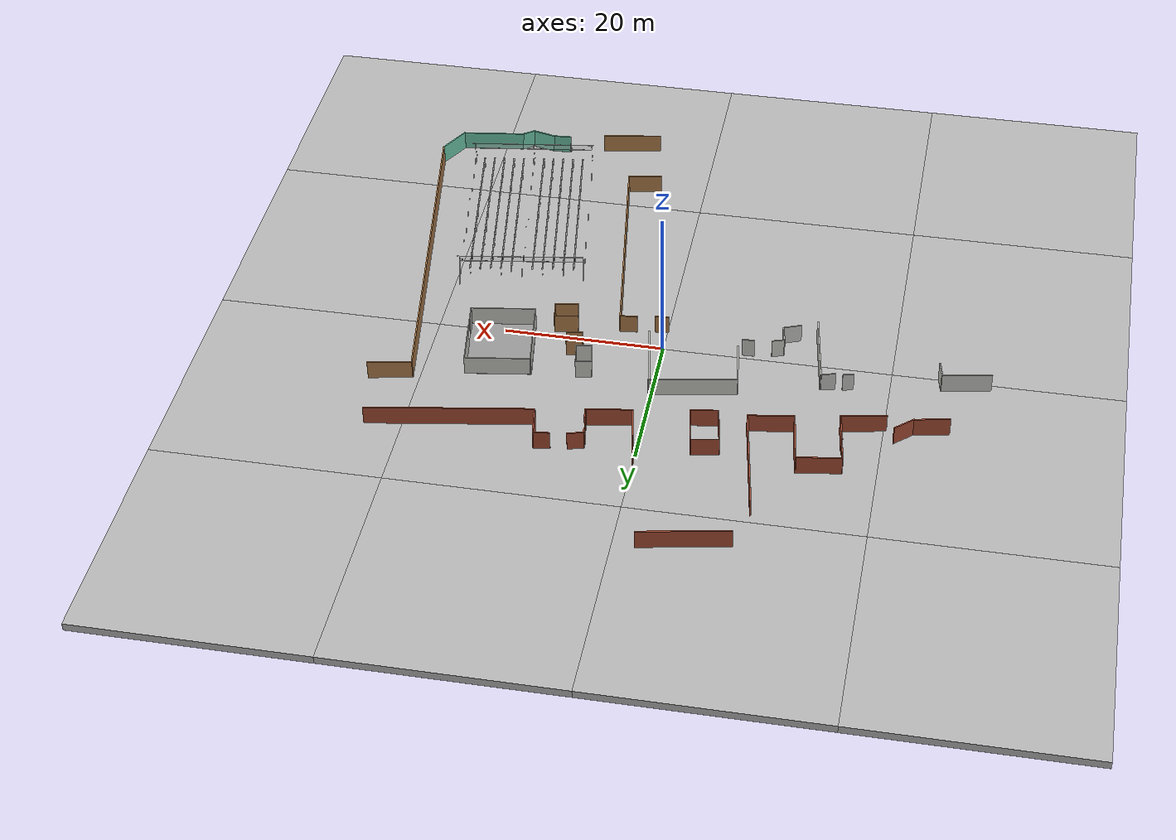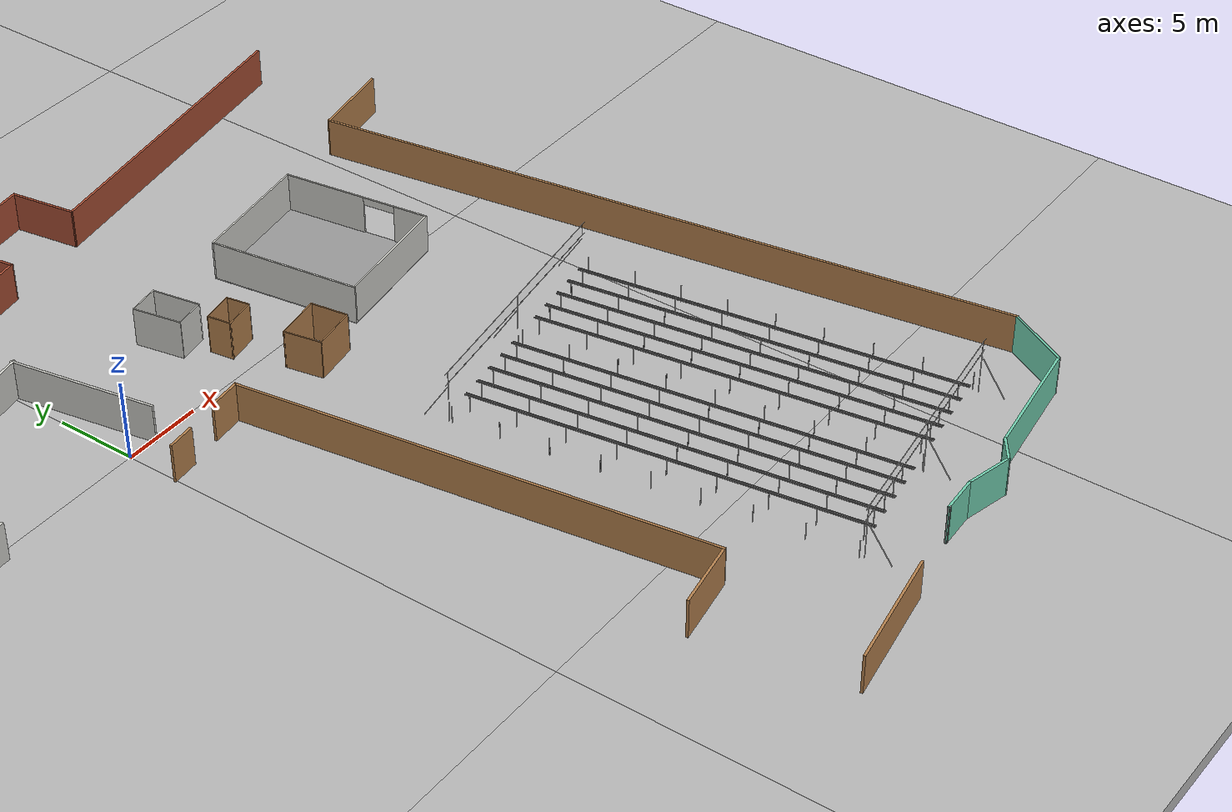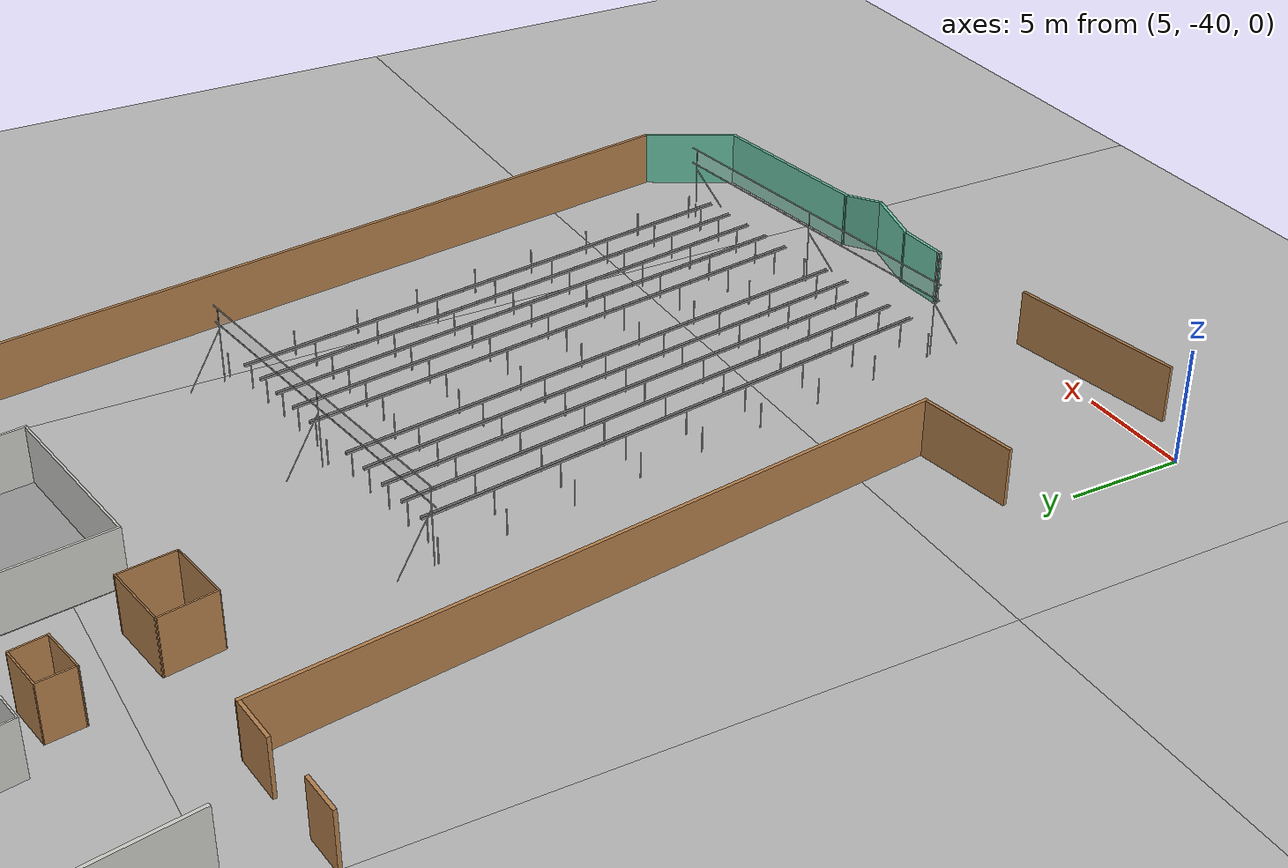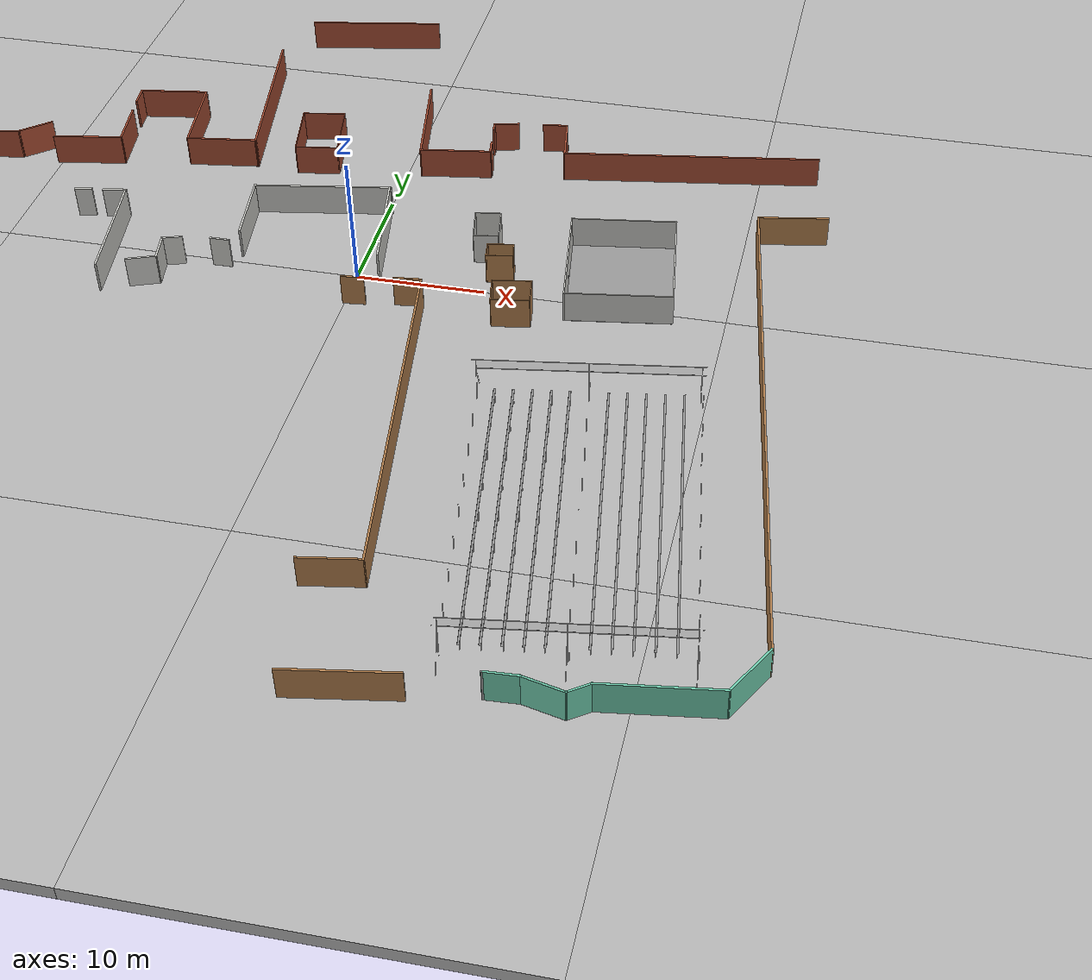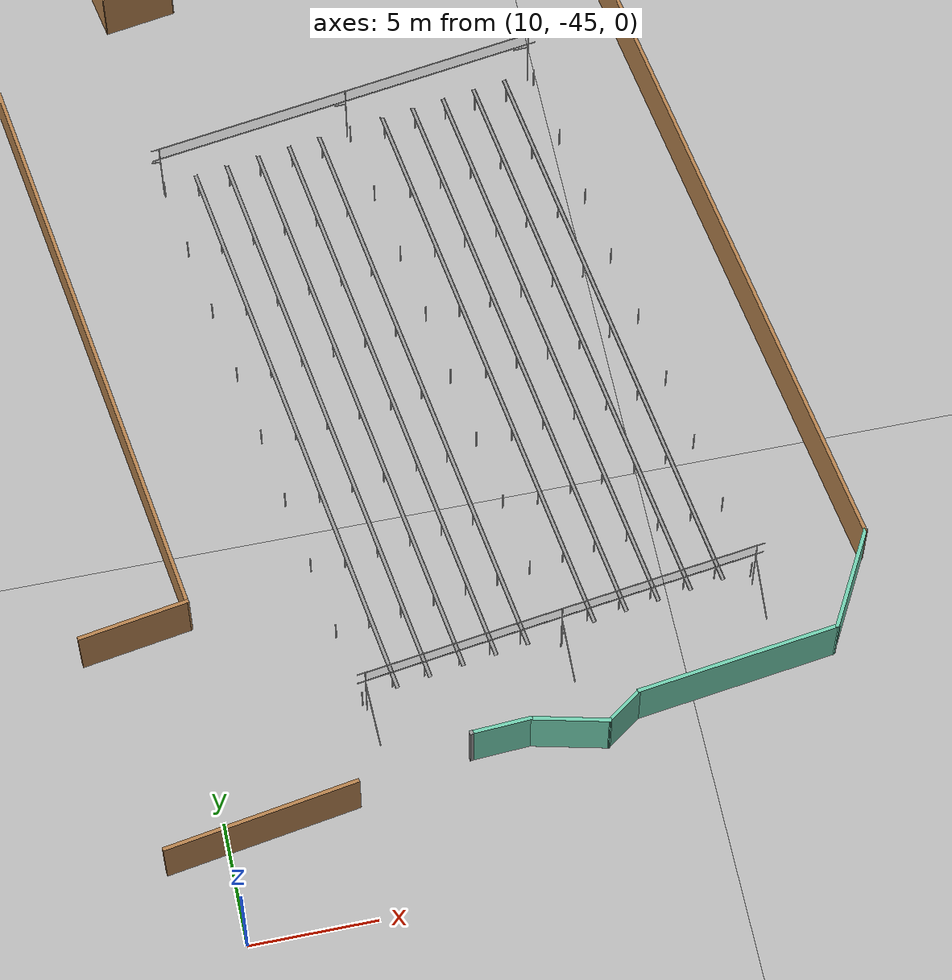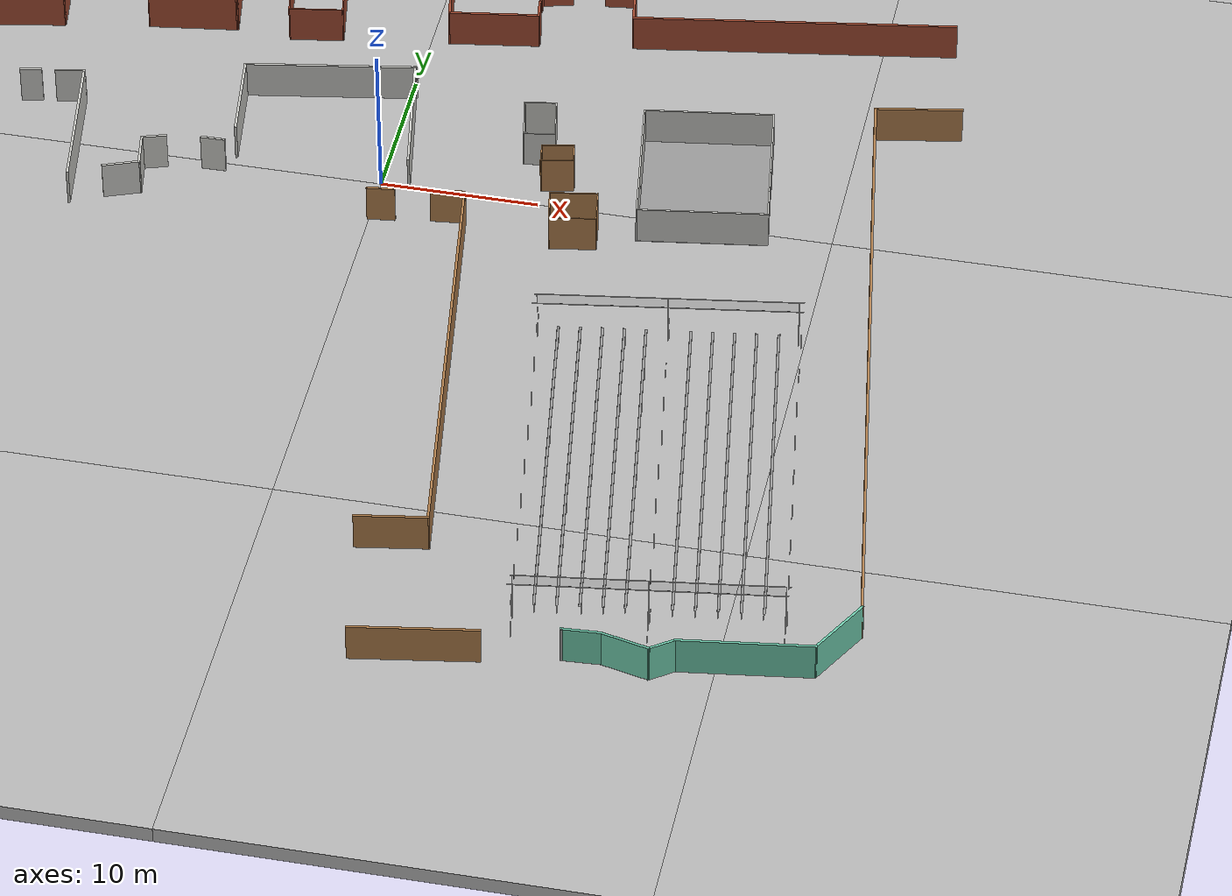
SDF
<sdf version="1.6">
 <world name="default">
  <atmosphere type="adiabatic"/>
  <light name="sun" type="directional">
   <direction>-0.5 0.1 -0.9</direction>
   <pose>0 0 10 0 -0 0</pose>
   <attenuation>
    <range>1000</range>
    <quadratic>0.001</quadratic>
    <constant>0.9</constant>
    <linear>0.01</linear>
   </attenuation>
   <diffuse>0.8 0.8 0.8 1</diffuse>
   <specular>0.2 0.2 0.2 1</specular>
  </light>
  <scene>
   <shadows>1</shadows>
   <sky><clouds><speed>12</speed></clouds></sky>
   <background>0.7 0.7 0.7 1</background>
   <ambient>0.4 0.4 0.4 1</ambient>
  </scene>
  <gravity>0 0 -9.8</gravity>
  <magnetic_field>6e-06 2.3e-05 -4.2e-05</magnetic_field>
  <model name="pole_0">
   <link name="link">
    <collision name="collision">
     <geometry><cylinder><length>1.15</length><radius>0.025</radius></cylinder></geometry>
    </collision>
    <visual name="visual">
     <geometry><cylinder><length>1.15</length><radius>0.025</radius></cylinder></geometry>
     <material>
      <script><uri>file://media/materials/scripts/gazebo.material</uri><name>Gazebo/Chrome</name></script>
      <emissive>0.1 0.1 0.1 1</emissive>
      <shader type="vertex"><normal_map>__default__</normal_map></shader>
      <specular>0.01 0.01 0.01 1</specular>
      <ambient>0.5 0.5 0.5 1</ambient>
      <diffuse>0.05 0.05 0.05 1</diffuse>
     </material>
    </visual>
   </link>
   <static>1</static>
   <pose>20.47 -11.17 0.575 0 -0 0</pose>
  </model>
  <model name="pole_1">
   <link name="link">
    <collision name="collision">
     <geometry><cylinder><length>1.15</length><radius>0.025</radius></cylinder></geometry>
    </collision>
    <visual name="visual">
     <geometry><cylinder><length>1.15</length><radius>0.025</radius></cylinder></geometry>
     <material>
      <script><uri>file://media/materials/scripts/gazebo.material</uri><name>Gazebo/Chrome</name></script>
      <emissive>0.1 0.1 0.1 1</emissive>
      <shader type="vertex"><normal_map>__default__</normal_map></shader>
      <specular>0.01 0.01 0.01 1</specular>
      <ambient>0.5 0.5 0.5 1</ambient>
      <diffuse>0.05 0.05 0.05 1</diffuse>
     </material>
    </visual>
   </link>
   <static>1</static>
   <pose>20.89 -14.15 0.575 0 -0 0</pose>
  </model>
  <model name="pole_2">
   <link name="link">
    <collision name="collision">
     <geometry><cylinder><length>1.15</length><radius>0.025</radius></cylinder></geometry>
    </collision>
    <visual name="visual">
     <geometry><cylinder><length>1.15</length><radius>0.025</radius></cylinder></geometry>
     <material>
      <script><uri>file://media/materials/scripts/gazebo.material</uri><name>Gazebo/Chrome</name></script>
      <emissive>0.1 0.1 0.1 1</emissive>
      <shader type="vertex"><normal_map>__default__</normal_map></shader>
      <specular>0.01 0.01 0.01 1</specular>
      <ambient>0.5 0.5 0.5 1</ambient>
      <diffuse>0.05 0.05 0.05 1</diffuse>
     </material>
    </visual>
   </link>
   <static>1</static>
   <pose>21.37 -17.15 0.575 0 -0 0</pose>
  </model>
  <model name="pole_3">
   <link name="link">
    <collision name="collision">
     <geometry><cylinder><length>1.15</length><radius>0.025</radius></cylinder></geometry>
    </collision>
    <visual name="visual">
     <geometry><cylinder><length>1.15</length><radius>0.025</radius></cylinder></geometry>
     <material>
      <script><uri>file://media/materials/scripts/gazebo.material</uri><name>Gazebo/Chrome</name></script>
      <emissive>0.1 0.1 0.1 1</emissive>
      <shader type="vertex"><normal_map>__default__</normal_map></shader>
      <specular>0.01 0.01 0.01 1</specular>
      <ambient>0.5 0.5 0.5 1</ambient>
      <diffuse>0.05 0.05 0.05 1</diffuse>
     </material>
    </visual>
   </link>
   <static>1</static>
   <pose>21.82 -20.12 0.575 0 -0 0</pose>
  </model>
  <model name="pole_4">
   <link name="link">
    <collision name="collision">
     <geometry><cylinder><length>1.15</length><radius>0.025</radius></cylinder></geometry>
    </collision>
    <visual name="visual">
     <geometry><cylinder><length>1.15</length><radius>0.025</radius></cylinder></geometry>
     <material>
      <script><uri>file://media/materials/scripts/gazebo.material</uri><name>Gazebo/Chrome</name></script>
      <emissive>0.1 0.1 0.1 1</emissive>
      <shader type="vertex"><normal_map>__default__</normal_map></shader>
      <specular>0.01 0.01 0.01 1</specular>
      <ambient>0.5 0.5 0.5 1</ambient>
      <diffuse>0.05 0.05 0.05 1</diffuse>
     </material>
    </visual>
   </link>
   <static>1</static>
   <pose>22.22 -23.11 0.575 0 -0 0</pose>
  </model>
  <model name="pole_5">
   <link name="link">
    <collision name="collision">
     <geometry><cylinder><length>1.15</length><radius>0.025</radius></cylinder></geometry>
    </collision>
    <visual name="visual">
     <geometry><cylinder><length>1.15</length><radius>0.025</radius></cylinder></geometry>
     <material>
      <script><uri>file://media/materials/scripts/gazebo.material</uri><name>Gazebo/Chrome</name></script>
      <emissive>0.1 0.1 0.1 1</emissive>
      <shader type="vertex"><normal_map>__default__</normal_map></shader>
      <specular>0.01 0.01 0.01 1</specular>
      <ambient>0.5 0.5 0.5 1</ambient>
      <diffuse>0.05 0.05 0.05 1</diffuse>
     </material>
    </visual>
   </link>
   <static>1</static>
   <pose>22.65 -26.08 0.575 0 -0 0</pose>
  </model>
  <model name="pole_6">
   <link name="link">
    <collision name="collision">
     <geometry><cylinder><length>1.15</length><radius>0.025</radius></cylinder></geometry>
    </collision>
    <visual name="visual">
     <geometry><cylinder><length>1.15</length><radius>0.025</radius></cylinder></geometry>
     <material>
      <script><uri>file://media/materials/scripts/gazebo.material</uri><name>Gazebo/Chrome</name></script>
      <emissive>0.1 0.1 0.1 1</emissive>
      <shader type="vertex"><normal_map>__default__</normal_map></shader>
      <specular>0.01 0.01 0.01 1</specular>
      <ambient>0.5 0.5 0.5 1</ambient>
      <diffuse>0.05 0.05 0.05 1</diffuse>
     </material>
    </visual>
   </link>
   <static>1</static>
   <pose>23.1 -29.01 0.575 0 -0 0</pose>
  </model>
  <model name="pole_7">
   <link name="link">
    <collision name="collision">
     <geometry><cylinder><length>1.15</length><radius>0.025</radius></cylinder></geometry>
    </collision>
    <visual name="visual">
     <geometry><cylinder><length>1.15</length><radius>0.025</radius></cylinder></geometry>
     <material>
      <script><uri>file://media/materials/scripts/gazebo.material</uri><name>Gazebo/Chrome</name></script>
      <emissive>0.1 0.1 0.1 1</emissive>
      <shader type="vertex"><normal_map>__default__</normal_map></shader>
      <specular>0.01 0.01 0.01 1</specular>
      <ambient>0.5 0.5 0.5 1</ambient>
      <diffuse>0.05 0.05 0.05 1</diffuse>
     </material>
    </visual>
   </link>
   <static>1</static>
   <pose>23.53 -32.05 0.575 0 -0 0</pose>
  </model>
  <model name="pole_8">
   <link name="link">
    <collision name="collision">
     <geometry><cylinder><length>1.15</length><radius>0.025</radius></cylinder></geometry>
    </collision>
    <visual name="visual">
     <geometry><cylinder><length>1.15</length><radius>0.025</radius></cylinder></geometry>
     <material>
      <script><uri>file://media/materials/scripts/gazebo.material</uri><name>Gazebo/Chrome</name></script>
      <emissive>0.1 0.1 0.1 1</emissive>
      <shader type="vertex"><normal_map>__default__</normal_map></shader>
      <specular>0.01 0.01 0.01 1</specular>
      <ambient>0.5 0.5 0.5 1</ambient>
      <diffuse>0.05 0.05 0.05 1</diffuse>
     </material>
    </visual>
   </link>
   <static>1</static>
   <pose>24.12 -35.26 0.575 0 -0 0</pose>
  </model>
  <model name="pole_9">
   <link name="link">
    <collision name="collision">
     <geometry><cylinder><length>1.15</length><radius>0.025</radius></cylinder></geometry>
    </collision>
    <visual name="visual">
     <geometry><cylinder><length>1.15</length><radius>0.025</radius></cylinder></geometry>
     <material>
      <script><uri>file://media/materials/scripts/gazebo.material</uri><name>Gazebo/Chrome</name></script>
      <emissive>0.1 0.1 0.1 1</emissive>
      <shader type="vertex"><normal_map>__default__</normal_map></shader>
      <specular>0.01 0.01 0.01 1</specular>
      <ambient>0.5 0.5 0.5 1</ambient>
      <diffuse>0.05 0.05 0.05 1</diffuse>
     </material>
    </visual>
   </link>
   <static>1</static>
   <pose>19.19 -11.68 0.575 0 -0 0</pose>
  </model>
  <model name="pole_100">
   <link name="link">
    <collision name="collision">
     <geometry><cylinder><length>1.15</length><radius>0.025</radius></cylinder></geometry>
    </collision>
    <visual name="visual">
     <geometry><cylinder><length>1.15</length><radius>0.025</radius></cylinder></geometry>
     <material>
      <script><uri>file://media/materials/scripts/gazebo.material</uri><name>Gazebo/Chrome</name></script>
      <emissive>0.1 0.1 0.1 1</emissive>
      <shader type="vertex"><normal_map>__default__</normal_map></shader>
      <specular>0.01 0.01 0.01 1</specular>
      <ambient>0.5 0.5 0.5 1</ambient>
      <diffuse>0.05 0.05 0.05 1</diffuse>
     </material>
    </visual>
   </link>
   <static>1</static>
   <pose>23.65 -14.1 0.575 0 -0 0</pose>
  </model>
  <model name="pole_101">
   <link name="link">
    <collision name="collision">
     <geometry><cylinder><length>1.15</length><radius>0.025</radius></cylinder></geometry>
    </collision>
    <visual name="visual">
     <geometry><cylinder><length>1.15</length><radius>0.025</radius></cylinder></geometry>
     <material>
      <script><uri>file://media/materials/scripts/gazebo.material</uri><name>Gazebo/Chrome</name></script>
      <emissive>0.1 0.1 0.1 1</emissive>
      <shader type="vertex"><normal_map>__default__</normal_map></shader>
      <specular>0.01 0.01 0.01 1</specular>
      <ambient>0.5 0.5 0.5 1</ambient>
      <diffuse>0.05 0.05 0.05 1</diffuse>
     </material>
    </visual>
   </link>
   <static>1</static>
   <pose>24.05 -17.05 0.575 0 -0 0</pose>
  </model>
  <model name="pole_102">
   <link name="link">
    <collision name="collision">
     <geometry><cylinder><length>1.15</length><radius>0.025</radius></cylinder></geometry>
    </collision>
    <visual name="visual">
     <geometry><cylinder><length>1.15</length><radius>0.025</radius></cylinder></geometry>
     <material>
      <script><uri>file://media/materials/scripts/gazebo.material</uri><name>Gazebo/Chrome</name></script>
      <emissive>0.1 0.1 0.1 1</emissive>
      <shader type="vertex"><normal_map>__default__</normal_map></shader>
      <specular>0.01 0.01 0.01 1</specular>
      <ambient>0.5 0.5 0.5 1</ambient>
      <diffuse>0.05 0.05 0.05 1</diffuse>
     </material>
    </visual>
   </link>
   <static>1</static>
   <pose>24.49 -20 0.575 0 -0 0</pose>
  </model>
  <model name="pole_103">
   <link name="link">
    <collision name="collision">
     <geometry><cylinder><length>1.15</length><radius>0.025</radius></cylinder></geometry>
    </collision>
    <visual name="visual">
     <geometry><cylinder><length>1.15</length><radius>0.025</radius></cylinder></geometry>
     <material>
      <script><uri>file://media/materials/scripts/gazebo.material</uri><name>Gazebo/Chrome</name></script>
      <emissive>0.1 0.1 0.1 1</emissive>
      <shader type="vertex"><normal_map>__default__</normal_map></shader>
      <specular>0.01 0.01 0.01 1</specular>
      <ambient>0.5 0.5 0.5 1</ambient>
      <diffuse>0.05 0.05 0.05 1</diffuse>
     </material>
    </visual>
   </link>
   <static>1</static>
   <pose>24.95 -22.95 0.575 0 -0 0</pose>
  </model>
  <model name="pole_104">
   <link name="link">
    <collision name="collision">
     <geometry><cylinder><length>1.15</length><radius>0.025</radius></cylinder></geometry>
    </collision>
    <visual name="visual">
     <geometry><cylinder><length>1.15</length><radius>0.025</radius></cylinder></geometry>
     <material>
      <script><uri>file://media/materials/scripts/gazebo.material</uri><name>Gazebo/Chrome</name></script>
      <emissive>0.1 0.1 0.1 1</emissive>
      <shader type="vertex"><normal_map>__default__</normal_map></shader>
      <specular>0.01 0.01 0.01 1</specular>
      <ambient>0.5 0.5 0.5 1</ambient>
      <diffuse>0.05 0.05 0.05 1</diffuse>
     </material>
    </visual>
   </link>
   <static>1</static>
   <pose>25.39 -25.9 0.575 0 -0 0</pose>
  </model>
  <model name="pole_105">
   <link name="link">
    <collision name="collision">
     <geometry><cylinder><length>1.15</length><radius>0.025</radius></cylinder></geometry>
    </collision>
    <visual name="visual">
     <geometry><cylinder><length>1.15</length><radius>0.025</radius></cylinder></geometry>
     <material>
      <script><uri>file://media/materials/scripts/gazebo.material</uri><name>Gazebo/Chrome</name></script>
      <emissive>0.1 0.1 0.1 1</emissive>
      <shader type="vertex"><normal_map>__default__</normal_map></shader>
      <specular>0.01 0.01 0.01 1</specular>
      <ambient>0.5 0.5 0.5 1</ambient>
      <diffuse>0.05 0.05 0.05 1</diffuse>
     </material>
    </visual>
   </link>
   <static>1</static>
   <pose>25.85 -28.9 0.575 0 -0 0</pose>
  </model>
  <model name="pole_106">
   <link name="link">
    <collision name="collision">
     <geometry><cylinder><length>1.15</length><radius>0.025</radius></cylinder></geometry>
    </collision>
    <visual name="visual">
     <geometry><cylinder><length>1.15</length><radius>0.025</radius></cylinder></geometry>
     <material>
      <script><uri>file://media/materials/scripts/gazebo.material</uri><name>Gazebo/Chrome</name></script>
      <emissive>0.1 0.1 0.1 1</emissive>
      <shader type="vertex"><normal_map>__default__</normal_map></shader>
      <specular>0.01 0.01 0.01 1</specular>
      <ambient>0.5 0.5 0.5 1</ambient>
      <diffuse>0.05 0.05 0.05 1</diffuse>
     </material>
    </visual>
   </link>
   <static>1</static>
   <pose>26.2 -31.6 0.575 0 -0 0</pose>
  </model>
  <model name="pole_107">
   <link name="link">
    <collision name="collision">
     <geometry><cylinder><length>1.15</length><radius>0.025</radius></cylinder></geometry>
    </collision>
    <visual name="visual">
     <geometry><cylinder><length>1.15</length><radius>0.025</radius></cylinder></geometry>
     <material>
      <script><uri>file://media/materials/scripts/gazebo.material</uri><name>Gazebo/Chrome</name></script>
      <emissive>0.1 0.1 0.1 1</emissive>
      <shader type="vertex"><normal_map>__default__</normal_map></shader>
      <specular>0.01 0.01 0.01 1</specular>
      <ambient>0.5 0.5 0.5 1</ambient>
      <diffuse>0.05 0.05 0.05 1</diffuse>
     </material>
    </visual>
   </link>
   <static>1</static>
   <pose>26.6 -34.25 0.575 0 -0 0</pose>
  </model>
  <model name="pole_108">
   <link name="link">
    <collision name="collision">
     <geometry><cylinder><length>1.15</length><radius>0.025</radius></cylinder></geometry>
    </collision>
    <visual name="visual">
     <geometry><cylinder><length>1.15</length><radius>0.025</radius></cylinder></geometry>
     <material>
      <script><uri>file://media/materials/scripts/gazebo.material</uri><name>Gazebo/Chrome</name></script>
      <emissive>0.1 0.1 0.1 1</emissive>
      <shader type="vertex"><normal_map>__default__</normal_map></shader>
      <specular>0.01 0.01 0.01 1</specular>
      <ambient>0.5 0.5 0.5 1</ambient>
      <diffuse>0.05 0.05 0.05 1</diffuse>
     </material>
    </visual>
   </link>
   <static>1</static>
   <pose>21.88 -11.28 0.575 0 -0 0</pose>
  </model>
  <model name="pole_109">
   <link name="link">
    <collision name="collision">
     <geometry><cylinder><length>1.15</length><radius>0.025</radius></cylinder></geometry>
    </collision>
    <visual name="visual">
     <geometry><cylinder><length>1.15</length><radius>0.025</radius></cylinder></geometry>
     <material>
      <script><uri>file://media/materials/scripts/gazebo.material</uri><name>Gazebo/Chrome</name></script>
      <emissive>0.1 0.1 0.1 1</emissive>
      <shader type="vertex"><normal_map>__default__</normal_map></shader>
      <specular>0.01 0.01 0.01 1</specular>
      <ambient>0.5 0.5 0.5 1</ambient>
      <diffuse>0.05 0.05 0.05 1</diffuse>
     </material>
    </visual>
   </link>
   <static>1</static>
   <pose>22.35 -14.29 0.575 0 -0 0</pose>
  </model>
  <model name="pole_110">
   <link name="link">
    <collision name="collision">
     <geometry><cylinder><length>1.15</length><radius>0.025</radius></cylinder></geometry>
    </collision>
    <visual name="visual">
     <geometry><cylinder><length>1.15</length><radius>0.025</radius></cylinder></geometry>
     <material>
      <script><uri>file://media/materials/scripts/gazebo.material</uri><name>Gazebo/Chrome</name></script>
      <emissive>0.1 0.1 0.1 1</emissive>
      <shader type="vertex"><normal_map>__default__</normal_map></shader>
      <specular>0.01 0.01 0.01 1</specular>
      <ambient>0.5 0.5 0.5 1</ambient>
      <diffuse>0.05 0.05 0.05 1</diffuse>
     </material>
    </visual>
   </link>
   <static>1</static>
   <pose>22.77 -17.24 0.575 0 -0 0</pose>
  </model>
  <model name="pole_111">
   <link name="link">
    <collision name="collision">
     <geometry><cylinder><length>1.15</length><radius>0.025</radius></cylinder></geometry>
    </collision>
    <visual name="visual">
     <geometry><cylinder><length>1.15</length><radius>0.025</radius></cylinder></geometry>
     <material>
      <script><uri>file://media/materials/scripts/gazebo.material</uri><name>Gazebo/Chrome</name></script>
      <emissive>0.1 0.1 0.1 1</emissive>
      <shader type="vertex"><normal_map>__default__</normal_map></shader>
      <specular>0.01 0.01 0.01 1</specular>
      <ambient>0.5 0.5 0.5 1</ambient>
      <diffuse>0.05 0.05 0.05 1</diffuse>
     </material>
    </visual>
   </link>
   <static>1</static>
   <pose>23.19 -20.18 0.575 0 -0 0</pose>
  </model>
  <model name="pole_112">
   <link name="link">
    <collision name="collision">
     <geometry><cylinder><length>1.15</length><radius>0.025</radius></cylinder></geometry>
    </collision>
    <visual name="visual">
     <geometry><cylinder><length>1.15</length><radius>0.025</radius></cylinder></geometry>
     <material>
      <script><uri>file://media/materials/scripts/gazebo.material</uri><name>Gazebo/Chrome</name></script>
      <emissive>0.1 0.1 0.1 1</emissive>
      <shader type="vertex"><normal_map>__default__</normal_map></shader>
      <specular>0.01 0.01 0.01 1</specular>
      <ambient>0.5 0.5 0.5 1</ambient>
      <diffuse>0.05 0.05 0.05 1</diffuse>
     </material>
    </visual>
   </link>
   <static>1</static>
   <pose>23.65 -23.15 0.575 0 -0 0</pose>
  </model>
  <model name="pole_113">
   <link name="link">
    <collision name="collision">
     <geometry><cylinder><length>1.15</length><radius>0.025</radius></cylinder></geometry>
    </collision>
    <visual name="visual">
     <geometry><cylinder><length>1.15</length><radius>0.025</radius></cylinder></geometry>
     <material>
      <script><uri>file://media/materials/scripts/gazebo.material</uri><name>Gazebo/Chrome</name></script>
      <emissive>0.1 0.1 0.1 1</emissive>
      <shader type="vertex"><normal_map>__default__</normal_map></shader>
      <specular>0.01 0.01 0.01 1</specular>
      <ambient>0.5 0.5 0.5 1</ambient>
      <diffuse>0.05 0.05 0.05 1</diffuse>
     </material>
    </visual>
   </link>
   <static>1</static>
   <pose>24.07 -26.13 0.575 0 -0 0</pose>
  </model>
  <model name="pole_114">
   <link name="link">
    <collision name="collision">
     <geometry><cylinder><length>1.15</length><radius>0.025</radius></cylinder></geometry>
    </collision>
    <visual name="visual">
     <geometry><cylinder><length>1.15</length><radius>0.025</radius></cylinder></geometry>
     <material>
      <script><uri>file://media/materials/scripts/gazebo.material</uri><name>Gazebo/Chrome</name></script>
      <emissive>0.1 0.1 0.1 1</emissive>
      <shader type="vertex"><normal_map>__default__</normal_map></shader>
      <specular>0.01 0.01 0.01 1</specular>
      <ambient>0.5 0.5 0.5 1</ambient>
      <diffuse>0.05 0.05 0.05 1</diffuse>
     </material>
    </visual>
   </link>
   <static>1</static>
   <pose>24.49 -29.1 0.575 0 -0 0</pose>
  </model>
  <model name="pole_115">
   <link name="link">
    <collision name="collision">
     <geometry><cylinder><length>1.15</length><radius>0.025</radius></cylinder></geometry>
    </collision>
    <visual name="visual">
     <geometry><cylinder><length>1.15</length><radius>0.025</radius></cylinder></geometry>
     <material>
      <script><uri>file://media/materials/scripts/gazebo.material</uri><name>Gazebo/Chrome</name></script>
      <emissive>0.1 0.1 0.1 1</emissive>
      <shader type="vertex"><normal_map>__default__</normal_map></shader>
      <specular>0.01 0.01 0.01 1</specular>
      <ambient>0.5 0.5 0.5 1</ambient>
      <diffuse>0.05 0.05 0.05 1</diffuse>
     </material>
    </visual>
   </link>
   <static>1</static>
   <pose>24.9 -31.8 0.575 0 -0 0</pose>
  </model>
  <model name="pole_116">
   <link name="link">
    <collision name="collision">
     <geometry><cylinder><length>1.15</length><radius>0.025</radius></cylinder></geometry>
    </collision>
    <visual name="visual">
     <geometry><cylinder><length>1.15</length><radius>0.025</radius></cylinder></geometry>
     <material>
      <script><uri>file://media/materials/scripts/gazebo.material</uri><name>Gazebo/Chrome</name></script>
      <emissive>0.1 0.1 0.1 1</emissive>
      <shader type="vertex"><normal_map>__default__</normal_map></shader>
      <specular>0.01 0.01 0.01 1</specular>
      <ambient>0.5 0.5 0.5 1</ambient>
      <diffuse>0.05 0.05 0.05 1</diffuse>
     </material>
    </visual>
   </link>
   <static>1</static>
   <pose>25.3 -34.45 0.575 0 -0 0</pose>
  </model>
  <model name="pole_117">
   <link name="link">
    <collision name="collision">
     <geometry><cylinder><length>1.15</length><radius>0.025</radius></cylinder></geometry>
    </collision>
    <visual name="visual">
     <geometry><cylinder><length>1.15</length><radius>0.025</radius></cylinder></geometry>
     <material>
      <script><uri>file://media/materials/scripts/gazebo.material</uri><name>Gazebo/Chrome</name></script>
      <emissive>0.1 0.1 0.1 1</emissive>
      <shader type="vertex"><normal_map>__default__</normal_map></shader>
      <specular>0.01 0.01 0.01 1</specular>
      <ambient>0.5 0.5 0.5 1</ambient>
      <diffuse>0.05 0.05 0.05 1</diffuse>
     </material>
    </visual>
   </link>
   <static>1</static>
   <pose>20.47 -11.17 0.575 0 -0 0</pose>
  </model>
  <model name="pole_118">
   <link name="link">
    <collision name="collision">
     <geometry><cylinder><length>1.15</length><radius>0.025</radius></cylinder></geometry>
    </collision>
    <visual name="visual">
     <geometry><cylinder><length>1.15</length><radius>0.025</radius></cylinder></geometry>
     <material>
      <script><uri>file://media/materials/scripts/gazebo.material</uri><name>Gazebo/Chrome</name></script>
      <emissive>0.1 0.1 0.1 1</emissive>
      <shader type="vertex"><normal_map>__default__</normal_map></shader>
      <specular>0.01 0.01 0.01 1</specular>
      <ambient>0.5 0.5 0.5 1</ambient>
      <diffuse>0.05 0.05 0.05 1</diffuse>
     </material>
    </visual>
   </link>
   <static>1</static>
   <pose>20.89 -14.15 0.575 0 -0 0</pose>
  </model>
  <model name="pole_119">
   <link name="link">
    <collision name="collision">
     <geometry><cylinder><length>1.15</length><radius>0.025</radius></cylinder></geometry>
    </collision>
    <visual name="visual">
     <geometry><cylinder><length>1.15</length><radius>0.025</radius></cylinder></geometry>
     <material>
      <script><uri>file://media/materials/scripts/gazebo.material</uri><name>Gazebo/Chrome</name></script>
      <emissive>0.1 0.1 0.1 1</emissive>
      <shader type="vertex"><normal_map>__default__</normal_map></shader>
      <specular>0.01 0.01 0.01 1</specular>
      <ambient>0.5 0.5 0.5 1</ambient>
      <diffuse>0.05 0.05 0.05 1</diffuse>
     </material>
    </visual>
   </link>
   <static>1</static>
   <pose>21.37 -17.15 0.575 0 -0 0</pose>
  </model>
  <model name="pole_120">
   <link name="link">
    <collision name="collision">
     <geometry><cylinder><length>1.15</length><radius>0.025</radius></cylinder></geometry>
    </collision>
    <visual name="visual">
     <geometry><cylinder><length>1.15</length><radius>0.025</radius></cylinder></geometry>
     <material>
      <script><uri>file://media/materials/scripts/gazebo.material</uri><name>Gazebo/Chrome</name></script>
      <emissive>0.1 0.1 0.1 1</emissive>
      <shader type="vertex"><normal_map>__default__</normal_map></shader>
      <specular>0.01 0.01 0.01 1</specular>
      <ambient>0.5 0.5 0.5 1</ambient>
      <diffuse>0.05 0.05 0.05 1</diffuse>
     </material>
    </visual>
   </link>
   <static>1</static>
   <pose>21.82 -20.12 0.575 0 -0 0</pose>
  </model>
  <model name="pole_121">
   <link name="link">
    <collision name="collision">
     <geometry><cylinder><length>1.15</length><radius>0.025</radius></cylinder></geometry>
    </collision>
    <visual name="visual">
     <geometry><cylinder><length>1.15</length><radius>0.025</radius></cylinder></geometry>
     <material>
      <script><uri>file://media/materials/scripts/gazebo.material</uri><name>Gazebo/Chrome</name></script>
      <emissive>0.1 0.1 0.1 1</emissive>
      <shader type="vertex"><normal_map>__default__</normal_map></shader>
      <specular>0.01 0.01 0.01 1</specular>
      <ambient>0.5 0.5 0.5 1</ambient>
      <diffuse>0.05 0.05 0.05 1</diffuse>
     </material>
    </visual>
   </link>
   <static>1</static>
   <pose>22.22 -23.11 0.575 0 -0 0</pose>
  </model>
  <model name="pole_122">
   <link name="link">
    <collision name="collision">
     <geometry><cylinder><length>1.15</length><radius>0.025</radius></cylinder></geometry>
    </collision>
    <visual name="visual">
     <geometry><cylinder><length>1.15</length><radius>0.025</radius></cylinder></geometry>
     <material>
      <script><uri>file://media/materials/scripts/gazebo.material</uri><name>Gazebo/Chrome</name></script>
      <emissive>0.1 0.1 0.1 1</emissive>
      <shader type="vertex"><normal_map>__default__</normal_map></shader>
      <specular>0.01 0.01 0.01 1</specular>
      <ambient>0.5 0.5 0.5 1</ambient>
      <diffuse>0.05 0.05 0.05 1</diffuse>
     </material>
    </visual>
   </link>
   <static>1</static>
   <pose>22.65 -26.08 0.575 0 -0 0</pose>
  </model>
  <model name="pole_123">
   <link name="link">
    <collision name="collision">
     <geometry><cylinder><length>1.15</length><radius>0.025</radius></cylinder></geometry>
    </collision>
    <visual name="visual">
     <geometry><cylinder><length>1.15</length><radius>0.025</radius></cylinder></geometry>
     <material>
      <script><uri>file://media/materials/scripts/gazebo.material</uri><name>Gazebo/Chrome</name></script>
      <emissive>0.1 0.1 0.1 1</emissive>
      <shader type="vertex"><normal_map>__default__</normal_map></shader>
      <specular>0.01 0.01 0.01 1</specular>
      <ambient>0.5 0.5 0.5 1</ambient>
      <diffuse>0.05 0.05 0.05 1</diffuse>
     </material>
    </visual>
   </link>
   <static>1</static>
   <pose>23.1 -29.01 0.575 0 -0 0</pose>
  </model>
  <model name="pole_124">
   <link name="link">
    <collision name="collision">
     <geometry><cylinder><length>1.15</length><radius>0.025</radius></cylinder></geometry>
    </collision>
    <visual name="visual">
     <geometry><cylinder><length>1.15</length><radius>0.025</radius></cylinder></geometry>
     <material>
      <script><uri>file://media/materials/scripts/gazebo.material</uri><name>Gazebo/Chrome</name></script>
      <emissive>0.1 0.1 0.1 1</emissive>
      <shader type="vertex"><normal_map>__default__</normal_map></shader>
      <specular>0.01 0.01 0.01 1</specular>
      <ambient>0.5 0.5 0.5 1</ambient>
      <diffuse>0.05 0.05 0.05 1</diffuse>
     </material>
    </visual>
   </link>
   <static>1</static>
   <pose>23.53 -32.05 0.575 0 -0 0</pose>
  </model>
  <model name="pole_125">
   <link name="link">
    <collision name="collision">
     <geometry><cylinder><length>1.15</length><radius>0.025</radius></cylinder></geometry>
    </collision>
    <visual name="visual">
     <geometry><cylinder><length>1.15</length><radius>0.025</radius></cylinder></geometry>
     <material>
      <script><uri>file://media/materials/scripts/gazebo.material</uri><name>Gazebo/Chrome</name></script>
      <emissive>0.1 0.1 0.1 1</emissive>
      <shader type="vertex"><normal_map>__default__</normal_map></shader>
      <specular>0.01 0.01 0.01 1</specular>
      <ambient>0.5 0.5 0.5 1</ambient>
      <diffuse>0.05 0.05 0.05 1</diffuse>
     </material>
    </visual>
   </link>
   <static>1</static>
   <pose>24.12 -35.26 0.575 0 -0 0</pose>
  </model>
  <model name="frontage">
   <link name="link_1">
    <pose>6.68 -7.94 1.7 0 -0 0</pose>
    <collision name="collision">
     <geometry><cylinder><length>3.5</length><radius>0.02</radius></cylinder></geometry>
    </collision>
    <visual name="visual">
     <geometry><cylinder><length>3.5</length><radius>0.02</radius></cylinder></geometry>
     <material>
      <script><uri>file://media/materials/scripts/gazebo.material</uri><name>Gazebo/Chrome</name></script>
      <emissive>0.1 0.1 0.1 1</emissive>
      <shader type="vertex"><normal_map>__default__</normal_map></shader>
      <specular>0.01 0.01 0.01 1</specular>
      <ambient>0.5 0.5 0.5 1</ambient>
      <diffuse>0.05 0.05 0.05 1</diffuse>
     </material>
    </visual>
   </link>
   <link name="link_2">
    <pose>6.68 0 1.7 0 -0 0</pose>
    <collision name="collision">
     <geometry><cylinder><length>3.5</length><radius>0.02</radius></cylinder></geometry>
    </collision>
    <visual name="visual">
     <geometry><cylinder><length>3.5</length><radius>0.02</radius></cylinder></geometry>
     <material>
      <script><uri>file://media/materials/scripts/gazebo.material</uri><name>Gazebo/Chrome</name></script>
      <emissive>0.1 0.1 0.1 1</emissive>
      <shader type="vertex"><normal_map>__default__</normal_map></shader>
      <specular>0.01 0.01 0.01 1</specular>
      <ambient>0.5 0.5 0.5 1</ambient>
      <diffuse>0.05 0.05 0.05 1</diffuse>
     </material>
    </visual>
   </link>
   <link name="link_3">
    <pose>6.68 7.93 1.7 0 -0 0</pose>
    <collision name="collision">
     <geometry><cylinder><length>3.5</length><radius>0.02</radius></cylinder></geometry>
    </collision>
    <visual name="visual">
     <geometry><cylinder><length>3.5</length><radius>0.02</radius></cylinder></geometry>
     <material>
      <script><uri>file://media/materials/scripts/gazebo.material</uri><name>Gazebo/Chrome</name></script>
      <emissive>0.1 0.1 0.1 1</emissive>
      <shader type="vertex"><normal_map>__default__</normal_map></shader>
      <specular>0.01 0.01 0.01 1</specular>
      <ambient>0.5 0.5 0.5 1</ambient>
      <diffuse>0.05 0.05 0.05 1</diffuse>
     </material>
    </visual>
   </link>
   <link name="link_4">
    <pose>6.68 0 2.7 1.5707 -0 0</pose>
    <collision name="collision">
     <geometry><cylinder><length>16.5</length><radius>0.02</radius></cylinder></geometry>
    </collision>
    <visual name="visual">
     <geometry><cylinder><length>16.5</length><radius>0.02</radius></cylinder></geometry>
     <material>
      <script><uri>file://media/materials/scripts/gazebo.material</uri><name>Gazebo/Chrome</name></script>
      <emissive>0.1 0.1 0.1 1</emissive>
      <shader type="vertex"><normal_map>__default__</normal_map></shader>
      <specular>0.01 0.01 0.01 1</specular>
      <ambient>0.5 0.5 0.5 1</ambient>
      <diffuse>0.05 0.05 0.05 1</diffuse>
     </material>
    </visual>
   </link>
   <link name="link_5">
    <pose>6.68 0 3.45 1.5707 -0 0</pose>
    <collision name="collision">
     <geometry><cylinder><length>16.5</length><radius>0.02</radius></cylinder></geometry>
    </collision>
    <visual name="visual">
     <geometry><cylinder><length>16.5</length><radius>0.02</radius></cylinder></geometry>
     <material>
      <script><uri>file://media/materials/scripts/gazebo.material</uri><name>Gazebo/Chrome</name></script>
      <emissive>0.1 0.1 0.1 1</emissive>
      <shader type="vertex"><normal_map>__default__</normal_map></shader>
      <specular>0.01 0.01 0.01 1</specular>
      <ambient>0.5 0.5 0.5 1</ambient>
      <diffuse>0.05 0.05 0.05 1</diffuse>
     </material>
    </visual>
   </link>
   <link name="link_6">
    <pose>5.89 -7.94 1.225 0 0.565 0</pose>
    <collision name="collision">
     <geometry><cylinder><length>2.93</length><radius>0.02</radius></cylinder></geometry>
    </collision>
    <visual name="visual">
     <geometry><cylinder><length>2.93</length><radius>0.02</radius></cylinder></geometry>
     <material>
      <script><uri>file://media/materials/scripts/gazebo.material</uri><name>Gazebo/Chrome</name></script>
      <emissive>0.1 0.1 0.1 1</emissive>
      <shader type="vertex"><normal_map>__default__</normal_map></shader>
      <specular>0.01 0.01 0.01 1</specular>
      <ambient>0.5 0.5 0.5 1</ambient>
      <diffuse>0.05 0.05 0.05 1</diffuse>
     </material>
    </visual>
   </link>
   <link name="link_7">
    <pose>5.89 0 1.225 0 0.565 0</pose>
    <collision name="collision">
     <geometry><cylinder><length>2.93</length><radius>0.02</radius></cylinder></geometry>
    </collision>
    <visual name="visual">
     <geometry><cylinder><length>2.93</length><radius>0.02</radius></cylinder></geometry>
     <material>
      <script><uri>file://media/materials/scripts/gazebo.material</uri><name>Gazebo/Chrome</name></script>
      <emissive>0.1 0.1 0.1 1</emissive>
      <shader type="vertex"><normal_map>__default__</normal_map></shader>
      <specular>0.01 0.01 0.01 1</specular>
      <ambient>0.5 0.5 0.5 1</ambient>
      <diffuse>0.05 0.05 0.05 1</diffuse>
     </material>
    </visual>
   </link>
   <link name="link_8">
    <pose>5.89 7.93 1.225 0 0.565 0</pose>
    <collision name="collision">
     <geometry><cylinder><length>2.93</length><radius>0.02</radius></cylinder></geometry>
    </collision>
    <visual name="visual">
     <geometry><cylinder><length>2.93</length><radius>0.02</radius></cylinder></geometry>
     <material>
      <script><uri>file://media/materials/scripts/gazebo.material</uri><name>Gazebo/Chrome</name></script>
      <emissive>0.1 0.1 0.1 1</emissive>
      <shader type="vertex"><normal_map>__default__</normal_map></shader>
      <specular>0.01 0.01 0.01 1</specular>
      <ambient>0.5 0.5 0.5 1</ambient>
      <diffuse>0.05 0.05 0.05 1</diffuse>
     </material>
    </visual>
   </link>
   <link name="link_9">
    <pose>6.68 0 3.075 0 -0 0</pose>
    <collision name="collision"><geometry><box><size>0.002 15.87 0.75</size></box></geometry></collision>
    <visual name="visual">
     <geometry><box><size>0.002 15.87 0.75</size></box></geometry>
     <material>
      <emissive>1 1 1 1</emissive>
      <shader type="vertex"><normal_map>__default__</normal_map></shader>
      <specular>1 1 1 1</specular>
      <lighting>1</lighting>
      <ambient>1 1 1 1</ambient>
      <diffuse>1 1 1 1</diffuse>
     </material>
     <transparency>0.65</transparency>
    </visual>
   </link>
   <static>1</static>
   <pose>19.378 -4.29745 -0 0 0 -1.42072</pose>
  </model>
  <model name="frontage_clone">
   <link name="link_1">
    <pose>6.68 -7.94 1.7 0 -0 0</pose>
    <collision name="collision">
     <geometry><cylinder><length>3.5</length><radius>0.02</radius></cylinder></geometry>
    </collision>
    <visual name="visual">
     <geometry><cylinder><length>3.5</length><radius>0.02</radius></cylinder></geometry>
     <material>
      <script><uri>file://media/materials/scripts/gazebo.material</uri><name>Gazebo/Chrome</name></script>
      <emissive>0.1 0.1 0.1 1</emissive>
      <shader type="vertex"><normal_map>__default__</normal_map></shader>
      <specular>0.01 0.01 0.01 1</specular>
      <ambient>0.5 0.5 0.5 1</ambient>
      <diffuse>0.05 0.05 0.05 1</diffuse>
     </material>
    </visual>
   </link>
   <link name="link_2">
    <pose>6.68 0 1.7 0 -0 0</pose>
    <collision name="collision">
     <geometry><cylinder><length>3.5</length><radius>0.02</radius></cylinder></geometry>
    </collision>
    <visual name="visual">
     <geometry><cylinder><length>3.5</length><radius>0.02</radius></cylinder></geometry>
     <material>
      <script><uri>file://media/materials/scripts/gazebo.material</uri><name>Gazebo/Chrome</name></script>
      <emissive>0.1 0.1 0.1 1</emissive>
      <shader type="vertex"><normal_map>__default__</normal_map></shader>
      <specular>0.01 0.01 0.01 1</specular>
      <ambient>0.5 0.5 0.5 1</ambient>
      <diffuse>0.05 0.05 0.05 1</diffuse>
     </material>
    </visual>
   </link>
   <link name="link_3">
    <pose>6.68 7.93 1.7 0 -0 0</pose>
    <collision name="collision">
     <geometry><cylinder><length>3.5</length><radius>0.02</radius></cylinder></geometry>
    </collision>
    <visual name="visual">
     <geometry><cylinder><length>3.5</length><radius>0.02</radius></cylinder></geometry>
     <material>
      <script><uri>file://media/materials/scripts/gazebo.material</uri><name>Gazebo/Chrome</name></script>
      <emissive>0.1 0.1 0.1 1</emissive>
      <shader type="vertex"><normal_map>__default__</normal_map></shader>
      <specular>0.01 0.01 0.01 1</specular>
      <ambient>0.5 0.5 0.5 1</ambient>
      <diffuse>0.05 0.05 0.05 1</diffuse>
     </material>
    </visual>
   </link>
   <link name="link_4">
    <pose>6.68 0 2.7 1.5707 -0 0</pose>
    <collision name="collision">
     <geometry><cylinder><length>16.5</length><radius>0.02</radius></cylinder></geometry>
    </collision>
    <visual name="visual">
     <geometry><cylinder><length>16.5</length><radius>0.02</radius></cylinder></geometry>
     <material>
      <script><uri>file://media/materials/scripts/gazebo.material</uri><name>Gazebo/Chrome</name></script>
      <emissive>0.1 0.1 0.1 1</emissive>
      <shader type="vertex"><normal_map>__default__</normal_map></shader>
      <specular>0.01 0.01 0.01 1</specular>
      <ambient>0.5 0.5 0.5 1</ambient>
      <diffuse>0.05 0.05 0.05 1</diffuse>
     </material>
    </visual>
   </link>
   <link name="link_5">
    <pose>6.68 0 3.45 1.5707 -0 0</pose>
    <collision name="collision">
     <geometry><cylinder><length>16.5</length><radius>0.02</radius></cylinder></geometry>
    </collision>
    <visual name="visual">
     <geometry><cylinder><length>16.5</length><radius>0.02</radius></cylinder></geometry>
     <material>
      <script><uri>file://media/materials/scripts/gazebo.material</uri><name>Gazebo/Chrome</name></script>
      <emissive>0.1 0.1 0.1 1</emissive>
      <shader type="vertex"><normal_map>__default__</normal_map></shader>
      <specular>0.01 0.01 0.01 1</specular>
      <ambient>0.5 0.5 0.5 1</ambient>
      <diffuse>0.05 0.05 0.05 1</diffuse>
     </material>
    </visual>
   </link>
   <link name="link_6">
    <pose>5.89 -7.94 1.225 0 0.565 0</pose>
    <collision name="collision">
     <geometry><cylinder><length>2.93</length><radius>0.02</radius></cylinder></geometry>
    </collision>
    <visual name="visual">
     <geometry><cylinder><length>2.93</length><radius>0.02</radius></cylinder></geometry>
     <material>
      <script><uri>file://media/materials/scripts/gazebo.material</uri><name>Gazebo/Chrome</name></script>
      <emissive>0.1 0.1 0.1 1</emissive>
      <shader type="vertex"><normal_map>__default__</normal_map></shader>
      <specular>0.01 0.01 0.01 1</specular>
      <ambient>0.5 0.5 0.5 1</ambient>
      <diffuse>0.05 0.05 0.05 1</diffuse>
     </material>
    </visual>
   </link>
   <link name="link_7">
    <pose>5.89 0 1.225 0 0.565 0</pose>
    <collision name="collision">
     <geometry><cylinder><length>2.93</length><radius>0.02</radius></cylinder></geometry>
    </collision>
    <visual name="visual">
     <geometry><cylinder><length>2.93</length><radius>0.02</radius></cylinder></geometry>
     <material>
      <script><uri>file://media/materials/scripts/gazebo.material</uri><name>Gazebo/Chrome</name></script>
      <emissive>0.1 0.1 0.1 1</emissive>
      <shader type="vertex"><normal_map>__default__</normal_map></shader>
      <specular>0.01 0.01 0.01 1</specular>
      <ambient>0.5 0.5 0.5 1</ambient>
      <diffuse>0.05 0.05 0.05 1</diffuse>
     </material>
    </visual>
   </link>
   <link name="link_8">
    <pose>5.89 7.93 1.225 0 0.565 0</pose>
    <collision name="collision">
     <geometry><cylinder><length>2.93</length><radius>0.02</radius></cylinder></geometry>
    </collision>
    <visual name="visual">
     <geometry><cylinder><length>2.93</length><radius>0.02</radius></cylinder></geometry>
     <material>
      <script><uri>file://media/materials/scripts/gazebo.material</uri><name>Gazebo/Chrome</name></script>
      <emissive>0.1 0.1 0.1 1</emissive>
      <shader type="vertex"><normal_map>__default__</normal_map></shader>
      <specular>0.01 0.01 0.01 1</specular>
      <ambient>0.5 0.5 0.5 1</ambient>
      <diffuse>0.05 0.05 0.05 1</diffuse>
     </material>
    </visual>
   </link>
   <link name="link_9">
    <pose>6.68 0 3.075 0 -0 0</pose>
    <collision name="collision"><geometry><box><size>0.002 15.87 0.75</size></box></geometry></collision>
    <visual name="visual">
     <geometry><box><size>0.002 15.87 0.75</size></box></geometry>
     <material>
      <emissive>1 1 1 1</emissive>
      <shader type="vertex"><normal_map>__default__</normal_map></shader>
      <specular>1 1 1 1</specular>
      <lighting>1</lighting>
      <ambient>1 1 1 1</ambient>
      <diffuse>1 1 1 1</diffuse>
     </material>
     <transparency>0.65</transparency>
    </visual>
   </link>
   <static>1</static>
   <pose>24.9847 -41.9744 0 0 -0 1.70941</pose>
  </model>
  <model name="riseholme_encolsure">
   <link name="Wall_10">
    <pose>37.9809 28.2217 0 0 -0 -0.71569</pose>
    <collision name="Wall_10_Collision">
     <geometry><box><size>4.40408 0.15 2.5</size></box></geometry>
     <pose>0 0 1.25 0 -0 0</pose>
    </collision>
    <visual name="Wall_10_Visual">
     <geometry><box><size>4.40408 0.15 2.5</size></box></geometry>
     <material>
      <ambient>0.435294 0.796078 0.67451 1</ambient>
      <script><uri>file://media/materials/scripts/gazebo.material</uri><name>Gazebo/Grey</name></script>
     </material>
     <pose>0 0 1.25 0 -0 0</pose>
     <meta><layer>0</layer></meta>
    </visual>
   </link>
   <link name="Wall_100">
    <pose>-13.3343 -20.6396 0 0 -0 -1.5708</pose>
    <collision name="Wall_100_Collision">
     <geometry><box><size>1.38035 0.15 2.5</size></box></geometry>
     <pose>0 0 1.25 0 -0 0</pose>
    </collision>
    <visual name="Wall_100_Visual">
     <geometry><box><size>1.38035 0.15 2.5</size></box></geometry>
     <material>
      <ambient>1 1 1 1</ambient>
      <script><uri>file://media/materials/scripts/gazebo.material</uri><name>Gazebo/CeilingTiled</name></script>
     </material>
     <pose>0 0 1.25 0 -0 0</pose>
     <meta><layer>0</layer></meta>
    </visual>
   </link>
   <link name="Wall_102">
    <pose>-21.5336 -0.928753 0 0 -0 -0.039709</pose>
    <collision name="Wall_102_Collision">
     <geometry><box><size>5.25909 0.07 2.5</size></box></geometry>
     <pose>0 0 1.25 0 -0 0</pose>
    </collision>
    <visual name="Wall_102_Visual">
     <geometry><box><size>5.25909 0.07 2.5</size></box></geometry>
     <material>
      <ambient>1 1 1 1</ambient>
      <script><uri>file://media/materials/scripts/gazebo.material</uri><name>Gazebo/Bricks</name></script>
     </material>
     <pose>0 0 1.25 0 -0 0</pose>
     <meta><layer>0</layer></meta>
    </visual>
   </link>
   <link name="Wall_103">
    <pose>-19.0441 -2.73925 0 0 -0 -1.63105</pose>
    <collision name="Wall_103_Collision">
     <geometry><box><size>3.49121 0.07 2.5</size></box></geometry>
     <pose>0 0 1.25 0 -0 0</pose>
    </collision>
    <visual name="Wall_103_Visual">
     <geometry><box><size>3.49121 0.07 2.5</size></box></geometry>
     <material>
      <ambient>1 1 1 1</ambient>
      <script><uri>file://media/materials/scripts/gazebo.material</uri><name>Gazebo/Bricks</name></script>
     </material>
     <pose>0 0 1.25 0 -0 0</pose>
     <meta><layer>0</layer></meta>
    </visual>
   </link>
   <link name="Wall_104">
    <pose>-21.7333 -4.34992 0 0 -0 3.10417</pose>
    <collision name="Wall_104_Collision">
     <geometry><box><size>5.24692 0.07 2.5</size></box></geometry>
     <pose>0 0 1.25 0 -0 0</pose>
    </collision>
    <visual name="Wall_104_Visual">
     <geometry><box><size>5.24692 0.07 2.5</size></box></geometry>
     <material>
      <ambient>1 1 1 1</ambient>
      <script><uri>file://media/materials/scripts/gazebo.material</uri><name>Gazebo/Bricks</name></script>
     </material>
     <pose>0 0 1.25 0 -0 0</pose>
     <meta><layer>0</layer></meta>
    </visual>
   </link>
   <link name="Wall_105">
    <pose>-24.2229 -2.53786 0 0 -0 1.51436</pose>
    <collision name="Wall_105_Collision">
     <geometry><box><size>3.49429 0.07 2.5</size></box></geometry>
     <pose>0 0 1.25 0 -0 0</pose>
    </collision>
    <visual name="Wall_105_Visual">
     <geometry><box><size>3.49429 0.07 2.5</size></box></geometry>
     <material>
      <ambient>1 1 1 1</ambient>
      <script><uri>file://media/materials/scripts/gazebo.material</uri><name>Gazebo/Bricks</name></script>
     </material>
     <pose>0 0 1.25 0 -0 0</pose>
     <meta><layer>0</layer></meta>
    </visual>
   </link>
   <link name="Wall_11">
    <pose>39.2604 22.8017 0 0 -0 -1.6515</pose>
    <collision name="Wall_11_Collision">
     <geometry><box><size>8.22495 0.15 2.5</size></box></geometry>
     <pose>0 0 1.25 0 -0 0</pose>
    </collision>
    <visual name="Wall_11_Visual">
     <geometry><box><size>8.22495 0.15 2.5</size></box></geometry>
     <material>
      <ambient>0.435294 0.796078 0.67451 1</ambient>
      <script><uri>file://media/materials/scripts/gazebo.material</uri><name>Gazebo/Grey</name></script>
     </material>
     <pose>0 0 1.25 0 -0 0</pose>
     <meta><layer>0</layer></meta>
    </visual>
   </link>
   <link name="Wall_12">
    <pose>39.2604 18.0097 0 0 -0 -1.16969</pose>
    <collision name="Wall_12_Collision">
     <geometry><box><size>1.81774 0.15 2.5</size></box></geometry>
     <pose>0 0 1.25 0 -0 0</pose>
    </collision>
    <visual name="Wall_12_Visual">
     <geometry><box><size>1.81774 0.15 2.5</size></box></geometry>
     <material>
      <ambient>0.435294 0.796078 0.67451 1</ambient>
      <script><uri>file://media/materials/scripts/gazebo.material</uri><name>Gazebo/Grey</name></script>
     </material>
     <pose>0 0 1.25 0 -0 0</pose>
     <meta><layer>0</layer></meta>
    </visual>
   </link>
   <link name="Wall_13">
    <pose>38.9349 15.8932 0 0 -0 -2.02041</pose>
    <collision name="Wall_13_Collision">
     <geometry><box><size>3.14637 0.15 2.5</size></box></geometry>
     <pose>0 0 1.25 0 -0 0</pose>
    </collision>
    <visual name="Wall_13_Visual">
     <geometry><box><size>3.14637 0.15 2.5</size></box></geometry>
     <material>
      <ambient>0.435294 0.796078 0.67451 1</ambient>
      <script><uri>file://media/materials/scripts/gazebo.material</uri><name>Gazebo/Grey</name></script>
     </material>
     <pose>0 0 1.25 0 -0 0</pose>
     <meta><layer>0</layer></meta>
    </visual>
   </link>
   <link name="Wall_14">
    <pose>38.0974 13.4042 0 0 -0 -1.73296</pose>
    <collision name="Wall_14_Collision">
     <geometry><box><size>2.45986 0.15 2.5</size></box></geometry>
     <pose>0 0 1.25 0 -0 0</pose>
    </collision>
    <visual name="Wall_14_Visual">
     <geometry><box><size>2.45986 0.15 2.5</size></box></geometry>
     <material>
      <ambient>0.435294 0.796078 0.67451 1</ambient>
      <script><uri>file://media/materials/scripts/gazebo.material</uri><name>Gazebo/Grey</name></script>
     </material>
     <pose>0 0 1.25 0 -0 0</pose>
     <meta><layer>0</layer></meta>
    </visual>
   </link>
   <link name="Wall_15">
    <pose>37.9161 12.2642 0 0 -0 -0.015821</pose>
    <collision name="Wall_15_Collision">
     <geometry><box><size>0.16 0.15 2.5</size></box></geometry>
     <pose>0 0 1.25 0 -0 0</pose>
    </collision>
    <visual name="Wall_15_Visual">
     <geometry><box><size>0.16 0.15 2.5</size></box></geometry>
     <material>
      <ambient>1 1 1 1</ambient>
      <script><uri>file://media/materials/scripts/gazebo.material</uri><name>Gazebo/Grey</name></script>
     </material>
     <pose>0 0 1.25 0 -0 0</pose>
     <meta><layer>0</layer></meta>
    </visual>
   </link>
   <link name="Wall_17">
    <pose>37.7484 3.75021 0 0 -0 -1.62562</pose>
    <collision name="Wall_17_Collision">
     <geometry><box><size>7.7914 0.15 2.5</size></box></geometry>
     <pose>0 0 1.25 0 -0 0</pose>
    </collision>
    <visual name="Wall_17_Visual">
     <geometry><box><size>7.7914 0.15 2.5</size></box></geometry>
     <material>
      <ambient>1 1 1 1</ambient>
      <script><uri>file://media/materials/scripts/gazebo.material</uri><name>Gazebo/Wood</name></script>
     </material>
     <pose>0 0 1.25 0 -0 0</pose>
     <meta><layer>0</layer></meta>
    </visual>
   </link>
   <link name="Wall_19">
    <pose>28.3339 2.41776 0 0 -0 1.51709</pose>
    <collision name="Wall_19_Collision">
     <geometry><box><size>4.48297 0.15 2.5</size></box></geometry>
     <pose>0 0 1.25 0 -0 0</pose>
    </collision>
    <visual name="Wall_19_Visual">
     <geometry><box><size>4.48297 0.15 2.5</size></box></geometry>
     <material>
      <ambient>1 1 1 1</ambient>
      <script><uri>file://media/materials/scripts/gazebo.material</uri><name>Gazebo/Wood</name></script>
     </material>
     <pose>0 0 1.25 0 -0 0</pose>
     <meta><layer>0</layer></meta>
    </visual>
   </link>
   <link name="Wall_20">
    <pose>13.7719 5.65117 0 0 -0 3.06882</pose>
    <collision name="Wall_20_Collision">
     <geometry><box><size>29.5845 0.15 2.5</size></box></geometry>
     <pose>0 0 1.25 0 -0 0</pose>
    </collision>
    <visual name="Wall_20_Visual">
     <geometry><box><size>29.5845 0.15 2.5</size></box></geometry>
     <material>
      <ambient>1 1 1 1</ambient>
      <script><uri>file://media/materials/scripts/gazebo.material</uri><name>Gazebo/Wood</name></script>
     </material>
     <pose>0 0 1.25 0 -0 0</pose>
     <meta><layer>0</layer></meta>
    </visual>
   </link>
   <link name="Wall_21">
    <pose>-1.02272 5.6977 0 0 -0 -1.68395</pose>
    <collision name="Wall_21_Collision">
     <geometry><box><size>2.21023 0.15 2.5</size></box></geometry>
     <pose>0 0 1.25 0 -0 0</pose>
    </collision>
    <visual name="Wall_21_Visual">
     <geometry><box><size>2.21023 0.15 2.5</size></box></geometry>
     <material>
      <ambient>1 1 1 1</ambient>
      <script><uri>file://media/materials/scripts/gazebo.material</uri><name>Gazebo/Wood</name></script>
     </material>
     <pose>0 0 1.25 0 -0 0</pose>
     <meta><layer>0</layer></meta>
    </visual>
   </link>
   <link name="Wall_23">
    <pose>-1.32513 1.53381 0 0 -0 -1.68459</pose>
    <collision name="Wall_23_Collision">
     <geometry><box><size>1.78894 0.15 2.5</size></box></geometry>
     <pose>0 0 1.25 0 -0 0</pose>
    </collision>
    <visual name="Wall_23_Visual">
     <geometry><box><size>1.78894 0.15 2.5</size></box></geometry>
     <material>
      <ambient>1 1 1 1</ambient>
      <script><uri>file://media/materials/scripts/gazebo.material</uri><name>Gazebo/Wood</name></script>
     </material>
     <pose>0 0 1.25 0 -0 0</pose>
     <meta><layer>0</layer></meta>
    </visual>
   </link>
   <link name="Wall_25">
    <pose>-8.65264 3.41803 0 0 -0 3.10059</pose>
    <collision name="Wall_25_Collision">
     <geometry><box><size>9.22979 0.15 2.5</size></box></geometry>
     <pose>0 0 1.25 0 -0 0</pose>
    </collision>
    <visual name="Wall_25_Visual">
     <geometry><box><size>9.22979 0.15 2.5</size></box></geometry>
     <material>
      <ambient>1 1 1 1</ambient>
      <script><uri>file://media/materials/scripts/gazebo.material</uri><name>Gazebo/CeilingTiled</name></script>
     </material>
     <pose>0 0 1.25 0 -0 0</pose>
     <meta><layer>0</layer></meta>
    </visual>
   </link>
   <link name="Wall_28">
    <pose>-17.2596 27.7733 0 0 -0 -1.63194</pose>
    <collision name="Wall_28_Collision">
     <geometry><box><size>20.7055 0.15 2.5</size></box></geometry>
     <pose>0 0 1.25 0 -0 0</pose>
    </collision>
    <visual name="Wall_28_Visual">
     <geometry><box><size>20.7055 0.15 2.5</size></box></geometry>
     <material>
      <ambient>1 1 1 1</ambient>
      <script><uri>file://media/materials/scripts/gazebo.material</uri><name>Gazebo/Bricks</name></script>
     </material>
     <pose>0 0 1.25 0 -0 0</pose>
     <meta><layer>0</layer></meta>
    </visual>
   </link>
   <link name="Wall_29">
    <pose>-19.958 17.6311 0 0 -0 3.08547</pose>
    <collision name="Wall_29_Collision">
     <geometry><box><size>4.29716 0.15 2.5</size></box></geometry>
     <pose>0 0 1.25 0 -0 0</pose>
    </collision>
    <visual name="Wall_29_Visual">
     <geometry><box><size>4.29716 0.15 2.5</size></box></geometry>
     <material>
      <ambient>1 1 1 1</ambient>
      <script><uri>file://media/materials/scripts/gazebo.material</uri><name>Gazebo/Bricks</name></script>
     </material>
     <pose>0 0 1.25 0 -0 0</pose>
     <meta><layer>0</layer></meta>
    </visual>
   </link>
   <link name="Wall_30">
    <pose>-22.1213 16.7937 0 0 -0 -1.66805</pose>
    <collision name="Wall_30_Collision">
     <geometry><box><size>2.06654 0.15 2.5</size></box></geometry>
     <pose>0 0 1.25 0 -0 0</pose>
    </collision>
    <visual name="Wall_30_Visual">
     <geometry><box><size>2.06654 0.15 2.5</size></box></geometry>
     <material>
      <ambient>1 1 1 1</ambient>
      <script><uri>file://media/materials/scripts/gazebo.material</uri><name>Gazebo/Bricks</name></script>
     </material>
     <pose>0 0 1.25 0 -0 0</pose>
     <meta><layer>0</layer></meta>
    </visual>
   </link>
   <link name="Wall_32">
    <pose>-22.3539 12.7228 0 0 -0 -1.52321</pose>
    <collision name="Wall_32_Collision">
     <geometry><box><size>2.10622 0.15 2.5</size></box></geometry>
     <pose>0 0 1.25 0 -0 0</pose>
    </collision>
    <visual name="Wall_32_Visual">
     <geometry><box><size>2.10622 0.15 2.5</size></box></geometry>
     <material>
      <ambient>1 1 1 1</ambient>
      <script><uri>file://media/materials/scripts/gazebo.material</uri><name>Gazebo/Bricks</name></script>
     </material>
     <pose>0 0 1.25 0 -0 0</pose>
     <meta><layer>0</layer></meta>
    </visual>
   </link>
   <link name="Wall_33">
    <pose>-21.9352 11.6993 0 0 -0 -0.124355</pose>
    <collision name="Wall_33_Collision">
     <geometry><box><size>0.900176 0.15 2.5</size></box></geometry>
     <pose>0 0 1.25 0 -0 0</pose>
    </collision>
    <visual name="Wall_33_Visual">
     <geometry><box><size>0.900176 0.15 2.5</size></box></geometry>
     <material>
      <ambient>1 1 1 1</ambient>
      <script><uri>file://media/materials/scripts/gazebo.material</uri><name>Gazebo/Bricks</name></script>
     </material>
     <pose>0 0 1.25 0 -0 0</pose>
     <meta><layer>0</layer></meta>
    </visual>
   </link>
   <link name="Wall_35">
    <pose>-18.8879 11.5132 0 0 -0 -0.068856</pose>
    <collision name="Wall_35_Collision">
     <geometry><box><size>1.5024 0.15 2.5</size></box></geometry>
     <pose>0 0 1.25 0 -0 0</pose>
    </collision>
    <visual name="Wall_35_Visual">
     <geometry><box><size>1.5024 0.15 2.5</size></box></geometry>
     <material>
      <ambient>1 1 1 1</ambient>
      <script><uri>file://media/materials/scripts/gazebo.material</uri><name>Gazebo/Bricks</name></script>
     </material>
     <pose>0 0 1.25 0 -0 0</pose>
     <meta><layer>0</layer></meta>
    </visual>
   </link>
   <link name="Wall_36">
    <pose>-18.3994 8.6287 0 0 -0 -1.63628</pose>
    <collision name="Wall_36_Collision">
     <geometry><box><size>5.83811 0.15 2.5</size></box></geometry>
     <pose>0 0 1.25 0 -0 0</pose>
    </collision>
    <visual name="Wall_36_Visual">
     <geometry><box><size>5.83811 0.15 2.5</size></box></geometry>
     <material>
      <ambient>1 1 1 1</ambient>
      <script><uri>file://media/materials/scripts/gazebo.material</uri><name>Gazebo/Bricks</name></script>
     </material>
     <pose>0 0 1.25 0 -0 0</pose>
     <meta><layer>0</layer></meta>
    </visual>
   </link>
   <link name="Wall_44">
    <pose>-4.6011 11.5102 0 0 -0 -0.068625</pose>
    <collision name="Wall_44_Collision">
     <geometry><box><size>1.5575 0.07 2.5</size></box></geometry>
     <pose>0 0 1.25 0 -0 0</pose>
    </collision>
    <visual name="Wall_44_Visual">
     <geometry><box><size>1.5575 0.07 2.5</size></box></geometry>
     <material>
      <ambient>1 1 1 1</ambient>
      <script><uri>file://media/materials/scripts/gazebo.material</uri><name>Gazebo/Wood</name></script>
     </material>
     <pose>0 0 1.25 0 -0 0</pose>
     <meta><layer>0</layer></meta>
    </visual>
   </link>
   <link name="Wall_48">
    <pose>-3.8286 12.4807 0 0 -0 1.54095</pose>
    <collision name="Wall_48_Collision">
     <geometry><box><size>2.1141 0.07 2.5</size></box></geometry>
     <pose>0 0 1.25 0 -0 0</pose>
    </collision>
    <visual name="Wall_48_Visual">
     <geometry><box><size>2.1141 0.07 2.5</size></box></geometry>
     <material>
      <ambient>1 1 1 1</ambient>
      <script><uri>file://media/materials/scripts/gazebo.material</uri><name>Gazebo/Wood</name></script>
     </material>
     <pose>0 0 1.25 0 -0 0</pose>
     <meta><layer>0</layer></meta>
    </visual>
   </link>
   <link name="Wall_49">
    <pose>-4.52166 13.5281 0 0 -0 3.10583</pose>
    <collision name="Wall_49_Collision">
     <geometry><box><size>1.51805 0.07 2.5</size></box></geometry>
     <pose>0 0 1.25 0 -0 0</pose>
    </collision>
    <visual name="Wall_49_Visual">
     <geometry><box><size>1.51805 0.07 2.5</size></box></geometry>
     <material>
      <ambient>1 1 1 1</ambient>
      <script><uri>file://media/materials/scripts/gazebo.material</uri><name>Gazebo/Wood</name></script>
     </material>
     <pose>0 0 1.25 0 -0 0</pose>
     <meta><layer>0</layer></meta>
    </visual>
   </link>
   <link name="Wall_5">
    <pose>-8.44986 35.2004 0 0 -0 -1.61387</pose>
    <collision name="Wall_5_Collision">
     <geometry><box><size>5.55178 0.15 2.5</size></box></geometry>
     <pose>0 0 1.25 0 -0 0</pose>
    </collision>
    <visual name="Wall_5_Visual">
     <geometry><box><size>5.55178 0.15 2.5</size></box></geometry>
     <material>
      <ambient>1 1 1 1</ambient>
      <script><uri>file://media/materials/scripts/gazebo.material</uri><name>Gazebo/Wood</name></script>
     </material>
     <pose>0 0 1.25 0 -0 0</pose>
     <meta><layer>0</layer></meta>
    </visual>
   </link>
   <link name="Wall_56">
    <pose>-7.90402 12.4344 0 0 -0 -0.042937</pose>
    <collision name="Wall_56_Collision">
     <geometry><box><size>3.10664 0.07 2.5</size></box></geometry>
     <pose>0 0 1.25 0 -0 0</pose>
    </collision>
    <visual name="Wall_56_Visual">
     <geometry><box><size>3.10664 0.07 2.5</size></box></geometry>
     <material>
      <ambient>1 1 1 1</ambient>
      <script><uri>file://media/materials/scripts/gazebo.material</uri><name>Gazebo/CeilingTiled</name></script>
     </material>
     <pose>0 0 1.25 0 -0 0</pose>
     <meta><layer>0</layer></meta>
    </visual>
   </link>
   <link name="Wall_57">
    <pose>-6.4376 11.4016 0 0 -0 -1.62294</pose>
    <collision name="Wall_57_Collision">
     <geometry><box><size>2.00785 0.07 2.5</size></box></geometry>
     <pose>0 0 1.25 0 -0 0</pose>
    </collision>
    <visual name="Wall_57_Visual">
     <geometry><box><size>2.00785 0.07 2.5</size></box></geometry>
     <material>
      <ambient>1 1 1 1</ambient>
      <script><uri>file://media/materials/scripts/gazebo.material</uri><name>Gazebo/CeilingTiled</name></script>
     </material>
     <pose>0 0 1.25 0 -0 0</pose>
     <meta><layer>0</layer></meta>
    </visual>
   </link>
   <link name="Wall_58">
    <pose>-8.0156 10.4711 0 0 -0 3.11541</pose>
    <collision name="Wall_58_Collision">
     <geometry><box><size>3.12574 0.07 2.5</size></box></geometry>
     <pose>0 0 1.25 0 -0 0</pose>
    </collision>
    <visual name="Wall_58_Visual">
     <geometry><box><size>3.12574 0.07 2.5</size></box></geometry>
     <material>
      <ambient>1 1 1 1</ambient>
      <script><uri>file://media/materials/scripts/gazebo.material</uri><name>Gazebo/CeilingTiled</name></script>
     </material>
     <pose>0 0 1.25 0 -0 0</pose>
     <meta><layer>0</layer></meta>
    </visual>
   </link>
   <link name="Wall_59">
    <pose>-9.48241 11.5097 0 0 -0 1.50992</pose>
    <collision name="Wall_59_Collision">
     <geometry><box><size>2.06504 0.07 2.5</size></box></geometry>
     <pose>0 0 1.25 0 -0 0</pose>
    </collision>
    <visual name="Wall_59_Visual">
     <geometry><box><size>2.06504 0.07 2.5</size></box></geometry>
     <material>
      <ambient>1 1 1 1</ambient>
      <script><uri>file://media/materials/scripts/gazebo.material</uri><name>Gazebo/CeilingTiled</name></script>
     </material>
     <pose>0 0 1.25 0 -0 0</pose>
     <meta><layer>0</layer></meta>
    </visual>
   </link>
   <link name="Wall_6">
    <pose>13.9049 31.0596 0 0 -0 -0.0641</pose>
    <collision name="Wall_6_Collision">
     <geometry><box><size>45.1846 0.15 2.5</size></box></geometry>
     <pose>0 0 1.25 0 -0 0</pose>
    </collision>
    <visual name="Wall_6_Visual">
     <geometry><box><size>45.1846 0.15 2.5</size></box></geometry>
     <material>
      <ambient>1 1 1 1</ambient>
      <script><uri>file://media/materials/scripts/gazebo.material</uri><name>Gazebo/Wood</name></script>
     </material>
     <pose>0 0 1.25 0 -0 0</pose>
     <meta><layer>0</layer></meta>
    </visual>
   </link>
   <link name="Wall_61">
    <pose>0.595403 14.8812 0 0 -0 -0.06822</pose>
    <collision name="Wall_61_Collision">
     <geometry><box><size>2.44653 0.07 2.5</size></box></geometry>
     <pose>0 0 1.25 0 -0 0</pose>
    </collision>
    <visual name="Wall_61_Visual">
     <geometry><box><size>2.44653 0.07 2.5</size></box></geometry>
     <material>
      <ambient>1 1 1 1</ambient>
      <script><uri>file://media/materials/scripts/gazebo.material</uri><name>Gazebo/Wood</name></script>
     </material>
     <pose>0 0 1.25 0 -0 0</pose>
     <meta><layer>0</layer></meta>
    </visual>
   </link>
   <link name="Wall_62">
    <pose>1.7059 13.3602 0 0 -0 -1.62283</pose>
    <collision name="Wall_62_Collision">
     <geometry><box><size>2.9539 0.07 2.5</size></box></geometry>
     <pose>0 0 1.25 0 -0 0</pose>
    </collision>
    <visual name="Wall_62_Visual">
     <geometry><box><size>2.9539 0.07 2.5</size></box></geometry>
     <material>
      <ambient>1 1 1 1</ambient>
      <script><uri>file://media/materials/scripts/gazebo.material</uri><name>Gazebo/Wood</name></script>
     </material>
     <pose>0 0 1.25 0 -0 0</pose>
     <meta><layer>0</layer></meta>
    </visual>
   </link>
   <link name="Wall_63">
    <pose>0.439403 11.9547 0 0 -0 3.11265</pose>
    <collision name="Wall_63_Collision">
     <geometry><box><size>2.45355 0.07 2.5</size></box></geometry>
     <pose>0 0 1.25 0 -0 0</pose>
    </collision>
    <visual name="Wall_63_Visual">
     <geometry><box><size>2.45355 0.07 2.5</size></box></geometry>
     <material>
      <ambient>1 1 1 1</ambient>
      <script><uri>file://media/materials/scripts/gazebo.material</uri><name>Gazebo/Wood</name></script>
     </material>
     <pose>0 0 1.25 0 -0 0</pose>
     <meta><layer>0</layer></meta>
    </visual>
   </link>
   <link name="Wall_64">
    <pose>-0.665097 13.4757 0 0 -0 1.51234</pose>
    <collision name="Wall_64_Collision">
     <geometry><box><size>3.04759 0.07 2.5</size></box></geometry>
     <pose>0 0 1.25 0 -0 0</pose>
    </collision>
    <visual name="Wall_64_Visual">
     <geometry><box><size>3.04759 0.07 2.5</size></box></geometry>
     <material>
      <ambient>1 1 1 1</ambient>
      <script><uri>file://media/materials/scripts/gazebo.material</uri><name>Gazebo/Wood</name></script>
     </material>
     <pose>0 0 1.25 0 -0 0</pose>
     <meta><layer>0</layer></meta>
    </visual>
   </link>
   <link name="Wall_66">
    <pose>-5.29416 12.5576 0 0 -0 1.52172</pose>
    <collision name="Wall_66_Collision">
     <geometry><box><size>2.06517 0.07 2.5</size></box></geometry>
     <pose>0 0 1.25 0 -0 0</pose>
    </collision>
    <visual name="Wall_66_Visual">
     <geometry><box><size>2.06517 0.07 2.5</size></box></geometry>
     <material>
      <ambient>1 1 1 1</ambient>
      <script><uri>file://media/materials/scripts/gazebo.material</uri><name>Gazebo/Wood</name></script>
     </material>
     <pose>0 0 1.25 0 -0 0</pose>
     <meta><layer>0</layer></meta>
    </visual>
   </link>
   <link name="Wall_68">
    <pose>-23.2225 6.00059 0 0 -0 3.09637</pose>
    <collision name="Wall_68_Collision">
     <geometry><box><size>9.43343 0.15 2.5</size></box></geometry>
     <pose>0 0 1.25 0 -0 0</pose>
    </collision>
    <visual name="Wall_68_Visual">
     <geometry><box><size>9.43343 0.15 2.5</size></box></geometry>
     <material>
      <ambient>1 1 1 1</ambient>
      <script><uri>file://media/materials/scripts/gazebo.material</uri><name>Gazebo/Bricks</name></script>
     </material>
     <pose>0 0 1.25 0 -0 0</pose>
     <meta><layer>0</layer></meta>
    </visual>
   </link>
   <link name="Wall_70">
    <pose>-39.3963 0.795734 0 0 -0 -1.61018</pose>
    <collision name="Wall_70_Collision">
     <geometry><box><size>11.2057 0.15 2.5</size></box></geometry>
     <pose>0 0 1.25 0 -0 0</pose>
    </collision>
    <visual name="Wall_70_Visual">
     <geometry><box><size>11.2057 0.15 2.5</size></box></geometry>
     <material>
      <ambient>1 1 1 1</ambient>
      <script><uri>file://media/materials/scripts/gazebo.material</uri><name>Gazebo/Bricks</name></script>
     </material>
     <pose>0 0 1.25 0 -0 0</pose>
     <meta><layer>0</layer></meta>
    </visual>
   </link>
   <link name="Wall_72">
    <pose>-27.4513 -7.47598 0 0 -0 -0.048651</pose>
    <collision name="Wall_72_Collision">
     <geometry><box><size>14.6971 0.15 2.5</size></box></geometry>
     <pose>0 0 1.25 0 -0 0</pose>
    </collision>
    <visual name="Wall_72_Visual">
     <geometry><box><size>14.6971 0.15 2.5</size></box></geometry>
     <material>
      <ambient>1 1 1 1</ambient>
      <script><uri>file://media/materials/scripts/gazebo.material</uri><name>Gazebo/Bricks</name></script>
     </material>
     <pose>0 0 1.25 0 -0 0</pose>
     <meta><layer>0</layer></meta>
    </visual>
   </link>
   <link name="Wall_73">
    <pose>-20.404 -10.6323 0 0 -0 -1.64831</pose>
    <collision name="Wall_73_Collision">
     <geometry><box><size>5.77205 0.15 2.5</size></box></geometry>
     <pose>0 0 1.25 0 -0 0</pose>
    </collision>
    <visual name="Wall_73_Visual">
     <geometry><box><size>5.77205 0.15 2.5</size></box></geometry>
     <material>
      <ambient>1 1 1 1</ambient>
      <script><uri>file://media/materials/scripts/gazebo.material</uri><name>Gazebo/Bricks</name></script>
     </material>
     <pose>0 0 1.25 0 -0 0</pose>
     <meta><layer>0</layer></meta>
    </visual>
   </link>
   <link name="Wall_74">
    <pose>-24.2134 -13.1628 0 0 -0 3.06598</pose>
    <collision name="Wall_74_Collision">
     <geometry><box><size>7.35391 0.15 2.5</size></box></geometry>
     <pose>0 0 1.25 0 -0 0</pose>
    </collision>
    <visual name="Wall_74_Visual">
     <geometry><box><size>7.35391 0.15 2.5</size></box></geometry>
     <material>
      <ambient>1 1 1 1</ambient>
      <script><uri>file://media/materials/scripts/gazebo.material</uri><name>Gazebo/Bricks</name></script>
     </material>
     <pose>0 0 1.25 0 -0 0</pose>
     <meta><layer>0</layer></meta>
    </visual>
   </link>
   <link name="Wall_75">
    <pose>-27.9683 -15.6388 0 0 -0 -1.63013</pose>
    <collision name="Wall_75_Collision">
     <geometry><box><size>5.65602 0.15 2.5</size></box></geometry>
     <pose>0 0 1.25 0 -0 0</pose>
    </collision>
    <visual name="Wall_75_Visual">
     <geometry><box><size>5.65602 0.15 2.5</size></box></geometry>
     <material>
      <ambient>1 1 1 1</ambient>
      <script><uri>file://media/materials/scripts/gazebo.material</uri><name>Gazebo/Bricks</name></script>
     </material>
     <pose>0 0 1.25 0 -0 0</pose>
     <meta><layer>0</layer></meta>
    </visual>
   </link>
   <link name="Wall_76">
    <pose>-27.2608 -18.4686 0 0 -0 -0.093477</pose>
    <collision name="Wall_76_Collision">
     <geometry><box><size>1.89905 0.15 2.5</size></box></geometry>
     <pose>0 0 1.25 0 -0 0</pose>
    </collision>
    <visual name="Wall_76_Visual">
     <geometry><box><size>1.89905 0.15 2.5</size></box></geometry>
     <material>
      <ambient>1 1 1 1</ambient>
      <script><uri>file://media/materials/scripts/gazebo.material</uri><name>Gazebo/Bricks</name></script>
     </material>
     <pose>0 0 1.25 0 -0 0</pose>
     <meta><layer>0</layer></meta>
    </visual>
   </link>
   <link name="Wall_78">
    <pose>-22.8801 -18.7952 0 0 -0 -0.066568</pose>
    <collision name="Wall_78_Collision">
     <geometry><box><size>4.2405 0.15 2.5</size></box></geometry>
     <pose>0 0 1.25 0 -0 0</pose>
    </collision>
    <visual name="Wall_78_Visual">
     <geometry><box><size>4.2405 0.15 2.5</size></box></geometry>
     <material>
      <ambient>1 1 1 1</ambient>
      <script><uri>file://media/materials/scripts/gazebo.material</uri><name>Gazebo/Bricks</name></script>
     </material>
     <pose>0 0 1.25 0 -0 0</pose>
     <meta><layer>0</layer></meta>
    </visual>
   </link>
   <link name="Wall_79">
    <pose>-20.921 -21.6794 0 0 -0 -1.60049</pose>
    <collision name="Wall_79_Collision">
     <geometry><box><size>5.64876 0.15 2.5</size></box></geometry>
     <pose>0 0 1.25 0 -0 0</pose>
    </collision>
    <visual name="Wall_79_Visual">
     <geometry><box><size>5.64876 0.15 2.5</size></box></geometry>
     <material>
      <ambient>1 1 1 1</ambient>
      <script><uri>file://media/materials/scripts/gazebo.material</uri><name>Gazebo/Bricks</name></script>
     </material>
     <pose>0 0 1.25 0 -0 0</pose>
     <meta><layer>0</layer></meta>
    </visual>
   </link>
   <link name="Wall_81">
    <pose>-22.5536 -26.305 0 0 -0 -1.0637</pose>
    <collision name="Wall_81_Collision">
     <geometry><box><size>2.9514 0.15 2.5</size></box></geometry>
     <pose>0 0 1.25 0 -0 0</pose>
    </collision>
    <visual name="Wall_81_Visual">
     <geometry><box><size>2.9514 0.15 2.5</size></box></geometry>
     <material>
      <ambient>1 1 1 1</ambient>
      <script><uri>file://media/materials/scripts/gazebo.material</uri><name>Gazebo/Bricks</name></script>
     </material>
     <pose>0 0 1.25 0 -0 0</pose>
     <meta><layer>0</layer></meta>
    </visual>
   </link>
   <link name="Wall_82">
    <pose>-21.955 -29.7062 0 0 -0 -1.60828</pose>
    <collision name="Wall_82_Collision">
     <geometry><box><size>4.50659 0.15 2.5</size></box></geometry>
     <pose>0 0 1.25 0 -0 0</pose>
    </collision>
    <visual name="Wall_82_Visual">
     <geometry><box><size>4.50659 0.15 2.5</size></box></geometry>
     <material>
      <ambient>1 1 1 1</ambient>
      <script><uri>file://media/materials/scripts/gazebo.material</uri><name>Gazebo/Bricks</name></script>
     </material>
     <pose>0 0 1.25 0 -0 0</pose>
     <meta><layer>0</layer></meta>
    </visual>
   </link>
   <link name="Wall_84">
    <pose>-14.2002 -35.0121 0 0 -0 1.51679</pose>
    <collision name="Wall_84_Collision">
     <geometry><box><size>6.19934 0.15 2.5</size></box></geometry>
     <pose>0 0 1.25 0 -0 0</pose>
    </collision>
    <visual name="Wall_84_Visual">
     <geometry><box><size>6.19934 0.15 2.5</size></box></geometry>
     <material>
      <ambient>1 1 1 1</ambient>
      <script><uri>file://media/materials/scripts/gazebo.material</uri><name>Gazebo/CeilingTiled</name></script>
     </material>
     <pose>0 0 1.25 0 -0 0</pose>
     <meta><layer>0</layer></meta>
    </visual>
   </link>
   <link name="Wall_85">
    <pose>-12.9758 -32.019 0 0 -0 -0.025635</pose>
    <collision name="Wall_85_Collision">
     <geometry><box><size>2.27304 0.15 2.5</size></box></geometry>
     <pose>0 0 1.25 0 -0 0</pose>
    </collision>
    <visual name="Wall_85_Visual">
     <geometry><box><size>2.27304 0.15 2.5</size></box></geometry>
     <material>
      <ambient>1 1 1 1</ambient>
      <script><uri>file://media/materials/scripts/gazebo.material</uri><name>Gazebo/CeilingTiled</name></script>
     </material>
     <pose>0 0 1.25 0 -0 0</pose>
     <meta><layer>0</layer></meta>
    </visual>
   </link>
   <link name="Wall_87">
    <pose>-13.358 -1.71119 0 0 -0 -1.61901</pose>
    <collision name="Wall_87_Collision">
     <geometry><box><size>10.9517 0.15 2.5</size></box></geometry>
     <pose>0 0 1.25 0 -0 0</pose>
    </collision>
    <visual name="Wall_87_Visual">
     <geometry><box><size>10.9517 0.15 2.5</size></box></geometry>
     <material>
      <ambient>1 1 1 1</ambient>
      <script><uri>file://media/materials/scripts/gazebo.material</uri><name>Gazebo/CeilingTiled</name></script>
     </material>
     <pose>0 0 1.25 0 -0 0</pose>
     <meta><layer>0</layer></meta>
    </visual>
   </link>
   <link name="Wall_88">
    <pose>-10.5424 -7.34239 0 0 -0 -0.076772</pose>
    <collision name="Wall_88_Collision">
     <geometry><box><size>6.3199 0.15 2.5</size></box></geometry>
     <pose>0 0 1.25 0 -0 0</pose>
    </collision>
    <visual name="Wall_88_Visual">
     <geometry><box><size>6.3199 0.15 2.5</size></box></geometry>
     <material>
      <ambient>1 1 1 1</ambient>
      <script><uri>file://media/materials/scripts/gazebo.material</uri><name>Gazebo/CeilingTiled</name></script>
     </material>
     <pose>0 0 1.25 0 -0 0</pose>
     <meta><layer>0</layer></meta>
    </visual>
   </link>
   <link name="Wall_90">
    <pose>-6.33083 -8.97496 0 0 -0 -1.77481</pose>
    <collision name="Wall_90_Collision">
     <geometry><box><size>1.55137 0.15 2.5</size></box></geometry>
     <pose>0 0 1.25 0 -0 0</pose>
    </collision>
    <visual name="Wall_90_Visual">
     <geometry><box><size>1.55137 0.15 2.5</size></box></geometry>
     <material>
      <ambient>1 1 1 1</ambient>
      <script><uri>file://media/materials/scripts/gazebo.material</uri><name>Gazebo/CeilingTiled</name></script>
     </material>
     <pose>0 0 1.25 0 -0 0</pose>
     <meta><layer>0</layer></meta>
    </visual>
   </link>
   <link name="Wall_92">
    <pose>-6.59109 -12.6423 0 0 -0 -1.47113</pose>
    <collision name="Wall_92_Collision">
     <geometry><box><size>1.57671 0.15 2.5</size></box></geometry>
     <pose>0 0 1.25 0 -0 0</pose>
    </collision>
    <visual name="Wall_92_Visual">
     <geometry><box><size>1.57671 0.15 2.5</size></box></geometry>
     <material>
      <ambient>1 1 1 1</ambient>
      <script><uri>file://media/materials/scripts/gazebo.material</uri><name>Gazebo/CeilingTiled</name></script>
     </material>
     <pose>0 0 1.25 0 -0 0</pose>
     <meta><layer>0</layer></meta>
    </visual>
   </link>
   <link name="Wall_94">
    <pose>-5.33709 -13.4468 0 0 -0 -0.039979</pose>
    <collision name="Wall_94_Collision">
     <geometry><box><size>2.51794 0.15 2.5</size></box></geometry>
     <pose>0 0 1.25 0 -0 0</pose>
    </collision>
    <visual name="Wall_94_Visual">
     <geometry><box><size>2.51794 0.15 2.5</size></box></geometry>
     <material>
      <ambient>1 1 1 1</ambient>
      <script><uri>file://media/materials/scripts/gazebo.material</uri><name>Gazebo/CeilingTiled</name></script>
     </material>
     <pose>0 0 1.25 0 -0 0</pose>
     <meta><layer>0</layer></meta>
    </visual>
   </link>
   <link name="Wall_95">
    <pose>-3.98844 -14.6062 0 0 -0 -1.42295</pose>
    <collision name="Wall_95_Collision">
     <geometry><box><size>2.39862 0.15 2.5</size></box></geometry>
     <pose>0 0 1.25 0 -0 0</pose>
    </collision>
    <visual name="Wall_95_Visual">
     <geometry><box><size>2.39862 0.15 2.5</size></box></geometry>
     <material>
      <ambient>1 1 1 1</ambient>
      <script><uri>file://media/materials/scripts/gazebo.material</uri><name>Gazebo/CeilingTiled</name></script>
     </material>
     <pose>0 0 1.25 0 -0 0</pose>
     <meta><layer>0</layer></meta>
    </visual>
   </link>
   <link name="Wall_97">
    <pose>-8.20001 -17.5874 0 0 -0 3.07947</pose>
    <collision name="Wall_97_Collision">
     <geometry><box><size>10.0592 0.15 2.5</size></box></geometry>
     <pose>0 0 1.25 0 -0 0</pose>
    </collision>
    <visual name="Wall_97_Visual">
     <geometry><box><size>10.0592 0.15 2.5</size></box></geometry>
     <material>
      <ambient>1 1 1 1</ambient>
      <script><uri>file://media/materials/scripts/gazebo.material</uri><name>Gazebo/CeilingTiled</name></script>
     </material>
     <pose>0 0 1.25 0 -0 0</pose>
     <meta><layer>0</layer></meta>
    </visual>
   </link>
   <link name="Wall_98">
    <pose>-13.1687 -18.1552 0 0 -0 -1.59782</pose>
    <collision name="Wall_98_Collision">
     <geometry><box><size>1.90152 0.15 2.5</size></box></geometry>
     <pose>0 0 1.25 0 -0 0</pose>
    </collision>
    <visual name="Wall_98_Visual">
     <geometry><box><size>1.90152 0.15 2.5</size></box></geometry>
     <material>
      <ambient>1 1 1 1</ambient>
      <script><uri>file://media/materials/scripts/gazebo.material</uri><name>Gazebo/CeilingTiled</name></script>
     </material>
     <pose>0 0 1.25 0 -0 0</pose>
     <meta><layer>0</layer></meta>
    </visual>
   </link>
   <static>1</static>
   <pose>-0.453277 -4.89704 0 0 0 -1.35297</pose>
  </model>
  <model name="food_handling_unit">
   <link name="Wall_5">
    <pose>-0 4.05 0 0 -0 0</pose>
    <collision name="Wall_5_Collision">
     <geometry><box><size>9.70037 0.1 2.5</size></box></geometry>
     <pose>0 0 1.25 0 -0 0</pose>
    </collision>
    <visual name="Wall_5_Visual">
     <geometry><box><size>9.70037 0.1 2.5</size></box></geometry>
     <material>
      <ambient>1 1 1 1</ambient>
      <script><uri>file://media/materials/scripts/gazebo.material</uri><name>Gazebo/CeilingTiled</name></script>
     </material>
     <pose>0 0 1.25 0 -0 0</pose>
     <meta><layer>0</layer></meta>
    </visual>
   </link>
   <link name="Wall_6">
    <pose>4.8 -0 0 0 -0 -1.5708</pose>
    <collision name="Wall_6_Collision">
     <geometry><box><size>8.20047 0.1 2.5</size></box></geometry>
     <pose>0 0 1.25 0 -0 0</pose>
    </collision>
    <visual name="Wall_6_Visual">
     <geometry><box><size>8.20047 0.1 2.5</size></box></geometry>
     <material>
      <ambient>1 1 1 1</ambient>
      <script><uri>file://media/materials/scripts/gazebo.material</uri><name>Gazebo/CeilingTiled</name></script>
     </material>
     <pose>0 0 1.25 0 -0 0</pose>
     <meta><layer>0</layer></meta>
    </visual>
   </link>
   <link name="Wall_7">
    <pose>-0 -4.05 0 0 -0 3.14159</pose>
    <collision name="Wall_7_Collision_0">
     <geometry><box><size>5.3757 0.1 2.5</size></box></geometry>
     <pose>-2.16197 0 1.25 0 -0 0</pose>
    </collision>
    <collision name="Wall_7_Collision_1">
     <geometry><box><size>2.23943 0.1 2.5</size></box></geometry>
     <pose>3.7301 0 1.25 0 -0 0</pose>
    </collision>
    <collision name="Wall_7_Collision_2">
     <geometry><box><size>2.0845 0.1 0.5</size></box></geometry>
     <pose>1.56813 0 2.25 0 -0 0</pose>
    </collision>
    <visual name="Wall_7_Visual_0">
     <geometry><box><size>5.3757 0.1 2.5</size></box></geometry>
     <material>
      <ambient>1 1 1 1</ambient>
      <script><uri>file://media/materials/scripts/gazebo.material</uri><name>Gazebo/CeilingTiled</name></script>
     </material>
     <pose>-2.16197 0 1.25 0 -0 0</pose>
     <meta><layer>0</layer></meta>
    </visual>
    <visual name="Wall_7_Visual_1">
     <geometry><box><size>2.23943 0.1 2.5</size></box></geometry>
     <material>
      <ambient>1 1 1 1</ambient>
      <script><uri>file://media/materials/scripts/gazebo.material</uri><name>Gazebo/CeilingTiled</name></script>
     </material>
     <pose>3.7301 0 1.25 0 -0 0</pose>
     <meta><layer>0</layer></meta>
    </visual>
    <visual name="Wall_7_Visual_2">
     <geometry><box><size>2.0845 0.1 0.5</size></box></geometry>
     <material>
      <ambient>1 1 1 1</ambient>
      <script><uri>file://media/materials/scripts/gazebo.material</uri><name>Gazebo/CeilingTiled</name></script>
     </material>
     <pose>1.56813 0 2.25 0 -0 0</pose>
     <meta><layer>0</layer></meta>
    </visual>
   </link>
   <link name="Wall_8">
    <pose>-4.8 -0 0 0 -0 1.5708</pose>
    <collision name="Wall_8_Collision">
     <geometry><box><size>8.19953 0.1 2.5</size></box></geometry>
     <pose>0 0 1.25 0 -0 0</pose>
    </collision>
    <visual name="Wall_8_Visual">
     <geometry><box><size>8.19953 0.1 2.5</size></box></geometry>
     <material>
      <ambient>1 1 1 1</ambient>
      <script><uri>file://media/materials/scripts/gazebo.material</uri><name>Gazebo/CeilingTiled</name></script>
     </material>
     <pose>0 0 1.25 0 -0 0</pose>
     <meta><layer>0</layer></meta>
    </visual>
   </link>
   <static>1</static>
   <pose>19.9734 3.27172 0 0 -0 1.71553</pose>
  </model>
  <model name="fhu_floor">
   <link name="link_0">
    <collision name="collision"><geometry><box><size>9.75 8.2 0.001</size></box></geometry></collision>
    <visual name="visual">
     <geometry><box><size>9.75 8.2 0.01</size></box></geometry>
     <material>
      <script><uri>file://media/materials/scripts/gazebo.material</uri><name>Gazebo/Grey</name></script>
      <shader type="vertex"><normal_map>__default__</normal_map></shader>
      <emissive>0 0 0 1</emissive>
      <specular>0.01 0.01 0.01 1</specular>
      <lighting>1</lighting>
      <ambient>0.3 0.3 0.3 1</ambient>
      <diffuse>0.7 0.7 0.7 1</diffuse>
     </material>
    </visual>
   </link>
   <static>1</static>
   <pose>19.932 3.26262 0 0 -0 1.71778</pose>
  </model>
  <model name="station_label_1">
   <link name="station_label_1_1">
    <visual name="visual">
     <geometry><plane><size>0.21 0.297</size><normal>0 0 1</normal></plane></geometry>
     <material>
      <script>
       <uri>model://station_label_1/materials/scripts</uri>
       <uri>model://station_label_1/materials/textures</uri>
       <name>station_label_1/image</name>
      </script>
     </material>
    </visual>
   </link>
   <static>1</static>
   <pose>16.35 0.5 0.875 0 1.57 0.145325</pose>
  </model>
  <model name="station_label_2">
   <link name="station_label_2_1">
    <visual name="visual">
     <geometry><plane><size>0.21 0.297</size><normal>0 0 1</normal></plane></geometry>
     <material>
      <script>
       <uri>model://station_label_2/materials/scripts</uri>
       <uri>model://station_label_2/materials/textures</uri>
       <name>station_label_2/image</name>
      </script>
     </material>
    </visual>
   </link>
   <static>1</static>
   <pose>16.56 -1 0.875 0 1.57 0.145</pose>
  </model>
  <model name="station_label_3">
   <link name="station_label_3_1">
    <visual name="visual">
     <geometry><plane><size>0.21 0.297</size><normal>0 0 1</normal></plane></geometry>
     <material>
      <script>
       <uri>model://station_label_3/materials/scripts</uri>
       <uri>model://station_label_3/materials/textures</uri>
       <name>station_label_3/image</name>
      </script>
     </material>
    </visual>
   </link>
   <static>1</static>
   <pose>16.13 2 0.875 0 1.57 0.145</pose>
  </model>
  <model name="pole_10">
   <link name="link">
    <collision name="collision">
     <geometry><cylinder><length>1.15</length><radius>0.025</radius></cylinder></geometry>
    </collision>
    <visual name="visual">
     <geometry><cylinder><length>1.15</length><radius>0.025</radius></cylinder></geometry>
     <material>
      <script><uri>file://media/materials/scripts/gazebo.material</uri><name>Gazebo/Chrome</name></script>
      <emissive>0.1 0.1 0.1 1</emissive>
      <shader type="vertex"><normal_map>__default__</normal_map></shader>
      <specular>0.01 0.01 0.01 1</specular>
      <ambient>0.5 0.5 0.5 1</ambient>
      <diffuse>0.05 0.05 0.05 1</diffuse>
     </material>
    </visual>
   </link>
   <static>1</static>
   <pose>19.65 -14.65 0.575 0 -0 0</pose>
  </model>
  <model name="pole_11">
   <link name="link">
    <collision name="collision">
     <geometry><cylinder><length>1.15</length><radius>0.025</radius></cylinder></geometry>
    </collision>
    <visual name="visual">
     <geometry><cylinder><length>1.15</length><radius>0.025</radius></cylinder></geometry>
     <material>
      <script><uri>file://media/materials/scripts/gazebo.material</uri><name>Gazebo/Chrome</name></script>
      <emissive>0.1 0.1 0.1 1</emissive>
      <shader type="vertex"><normal_map>__default__</normal_map></shader>
      <specular>0.01 0.01 0.01 1</specular>
      <ambient>0.5 0.5 0.5 1</ambient>
      <diffuse>0.05 0.05 0.05 1</diffuse>
     </material>
    </visual>
   </link>
   <static>1</static>
   <pose>20.08 -17.6 0.575 0 -0 0</pose>
  </model>
  <model name="pole_12">
   <link name="link">
    <collision name="collision">
     <geometry><cylinder><length>1.15</length><radius>0.025</radius></cylinder></geometry>
    </collision>
    <visual name="visual">
     <geometry><cylinder><length>1.15</length><radius>0.025</radius></cylinder></geometry>
     <material>
      <script><uri>file://media/materials/scripts/gazebo.material</uri><name>Gazebo/Chrome</name></script>
      <emissive>0.1 0.1 0.1 1</emissive>
      <shader type="vertex"><normal_map>__default__</normal_map></shader>
      <specular>0.01 0.01 0.01 1</specular>
      <ambient>0.5 0.5 0.5 1</ambient>
      <diffuse>0.05 0.05 0.05 1</diffuse>
     </material>
    </visual>
   </link>
   <static>1</static>
   <pose>20.5 -20.55 0.575 0 -0 0</pose>
  </model>
  <model name="pole_13">
   <link name="link">
    <collision name="collision">
     <geometry><cylinder><length>1.15</length><radius>0.025</radius></cylinder></geometry>
    </collision>
    <visual name="visual">
     <geometry><cylinder><length>1.15</length><radius>0.025</radius></cylinder></geometry>
     <material>
      <script><uri>file://media/materials/scripts/gazebo.material</uri><name>Gazebo/Chrome</name></script>
      <emissive>0.1 0.1 0.1 1</emissive>
      <shader type="vertex"><normal_map>__default__</normal_map></shader>
      <specular>0.01 0.01 0.01 1</specular>
      <ambient>0.5 0.5 0.5 1</ambient>
      <diffuse>0.05 0.05 0.05 1</diffuse>
     </material>
    </visual>
   </link>
   <static>1</static>
   <pose>20.95 -23.55 0.575 0 -0 0</pose>
  </model>
  <model name="pole_14">
   <link name="link">
    <collision name="collision">
     <geometry><cylinder><length>1.15</length><radius>0.025</radius></cylinder></geometry>
    </collision>
    <visual name="visual">
     <geometry><cylinder><length>1.15</length><radius>0.025</radius></cylinder></geometry>
     <material>
      <script><uri>file://media/materials/scripts/gazebo.material</uri><name>Gazebo/Chrome</name></script>
      <emissive>0.1 0.1 0.1 1</emissive>
      <shader type="vertex"><normal_map>__default__</normal_map></shader>
      <specular>0.01 0.01 0.01 1</specular>
      <ambient>0.5 0.5 0.5 1</ambient>
      <diffuse>0.05 0.05 0.05 1</diffuse>
     </material>
    </visual>
   </link>
   <static>1</static>
   <pose>21.37 -26.55 0.575 0 -0 0</pose>
  </model>
  <model name="pole_15">
   <link name="link">
    <collision name="collision">
     <geometry><cylinder><length>1.15</length><radius>0.025</radius></cylinder></geometry>
    </collision>
    <visual name="visual">
     <geometry><cylinder><length>1.15</length><radius>0.025</radius></cylinder></geometry>
     <material>
      <script><uri>file://media/materials/scripts/gazebo.material</uri><name>Gazebo/Chrome</name></script>
      <emissive>0.1 0.1 0.1 1</emissive>
      <shader type="vertex"><normal_map>__default__</normal_map></shader>
      <specular>0.01 0.01 0.01 1</specular>
      <ambient>0.5 0.5 0.5 1</ambient>
      <diffuse>0.05 0.05 0.05 1</diffuse>
     </material>
    </visual>
   </link>
   <static>1</static>
   <pose>21.8 -29.5 0.575 0 -0 0</pose>
  </model>
  <model name="pole_16">
   <link name="link">
    <collision name="collision">
     <geometry><cylinder><length>1.15</length><radius>0.025</radius></cylinder></geometry>
    </collision>
    <visual name="visual">
     <geometry><cylinder><length>1.15</length><radius>0.025</radius></cylinder></geometry>
     <material>
      <script><uri>file://media/materials/scripts/gazebo.material</uri><name>Gazebo/Chrome</name></script>
      <emissive>0.1 0.1 0.1 1</emissive>
      <shader type="vertex"><normal_map>__default__</normal_map></shader>
      <specular>0.01 0.01 0.01 1</specular>
      <ambient>0.5 0.5 0.5 1</ambient>
      <diffuse>0.05 0.05 0.05 1</diffuse>
     </material>
    </visual>
   </link>
   <static>1</static>
   <pose>22.2 -32.25 0.575 0 -0 0</pose>
  </model>
  <model name="pole_17">
   <link name="link">
    <collision name="collision">
     <geometry><cylinder><length>1.15</length><radius>0.025</radius></cylinder></geometry>
    </collision>
    <visual name="visual">
     <geometry><cylinder><length>1.15</length><radius>0.025</radius></cylinder></geometry>
     <material>
      <script><uri>file://media/materials/scripts/gazebo.material</uri><name>Gazebo/Chrome</name></script>
      <emissive>0.1 0.1 0.1 1</emissive>
      <shader type="vertex"><normal_map>__default__</normal_map></shader>
      <specular>0.01 0.01 0.01 1</specular>
      <ambient>0.5 0.5 0.5 1</ambient>
      <diffuse>0.05 0.05 0.05 1</diffuse>
     </material>
    </visual>
   </link>
   <static>1</static>
   <pose>22.55 -34.9 0.575 0 -0 0</pose>
  </model>
  <model name="pole_18">
   <link name="link">
    <collision name="collision">
     <geometry><cylinder><length>1.15</length><radius>0.025</radius></cylinder></geometry>
    </collision>
    <visual name="visual">
     <geometry><cylinder><length>1.15</length><radius>0.025</radius></cylinder></geometry>
     <material>
      <script><uri>file://media/materials/scripts/gazebo.material</uri><name>Gazebo/Chrome</name></script>
      <emissive>0.1 0.1 0.1 1</emissive>
      <shader type="vertex"><normal_map>__default__</normal_map></shader>
      <specular>0.01 0.01 0.01 1</specular>
      <ambient>0.5 0.5 0.5 1</ambient>
      <diffuse>0.05 0.05 0.05 1</diffuse>
     </material>
    </visual>
   </link>
   <static>1</static>
   <pose>17.9 -11.85 0.575 0 -0 0</pose>
  </model>
  <model name="pole_19">
   <link name="link">
    <collision name="collision">
     <geometry><cylinder><length>1.15</length><radius>0.025</radius></cylinder></geometry>
    </collision>
    <visual name="visual">
     <geometry><cylinder><length>1.15</length><radius>0.025</radius></cylinder></geometry>
     <material>
      <script><uri>file://media/materials/scripts/gazebo.material</uri><name>Gazebo/Chrome</name></script>
      <emissive>0.1 0.1 0.1 1</emissive>
      <shader type="vertex"><normal_map>__default__</normal_map></shader>
      <specular>0.01 0.01 0.01 1</specular>
      <ambient>0.5 0.5 0.5 1</ambient>
      <diffuse>0.05 0.05 0.05 1</diffuse>
     </material>
    </visual>
   </link>
   <static>1</static>
   <pose>18.34 -14.85 0.575 0 -0 0</pose>
  </model>
  <model name="pole_20">
   <link name="link">
    <collision name="collision">
     <geometry><cylinder><length>1.15</length><radius>0.025</radius></cylinder></geometry>
    </collision>
    <visual name="visual">
     <geometry><cylinder><length>1.15</length><radius>0.025</radius></cylinder></geometry>
     <material>
      <script><uri>file://media/materials/scripts/gazebo.material</uri><name>Gazebo/Chrome</name></script>
      <emissive>0.1 0.1 0.1 1</emissive>
      <shader type="vertex"><normal_map>__default__</normal_map></shader>
      <specular>0.01 0.01 0.01 1</specular>
      <ambient>0.5 0.5 0.5 1</ambient>
      <diffuse>0.05 0.05 0.05 1</diffuse>
     </material>
    </visual>
   </link>
   <static>1</static>
   <pose>18.8 -17.8 0.575 0 -0 0</pose>
  </model>
  <model name="pole_21">
   <link name="link">
    <collision name="collision">
     <geometry><cylinder><length>1.15</length><radius>0.025</radius></cylinder></geometry>
    </collision>
    <visual name="visual">
     <geometry><cylinder><length>1.15</length><radius>0.025</radius></cylinder></geometry>
     <material>
      <script><uri>file://media/materials/scripts/gazebo.material</uri><name>Gazebo/Chrome</name></script>
      <emissive>0.1 0.1 0.1 1</emissive>
      <shader type="vertex"><normal_map>__default__</normal_map></shader>
      <specular>0.01 0.01 0.01 1</specular>
      <ambient>0.5 0.5 0.5 1</ambient>
      <diffuse>0.05 0.05 0.05 1</diffuse>
     </material>
    </visual>
   </link>
   <static>1</static>
   <pose>19.2 -20.8 0.575 0 -0 0</pose>
  </model>
  <model name="pole_22">
   <link name="link">
    <collision name="collision">
     <geometry><cylinder><length>1.15</length><radius>0.025</radius></cylinder></geometry>
    </collision>
    <visual name="visual">
     <geometry><cylinder><length>1.15</length><radius>0.025</radius></cylinder></geometry>
     <material>
      <script><uri>file://media/materials/scripts/gazebo.material</uri><name>Gazebo/Chrome</name></script>
      <emissive>0.1 0.1 0.1 1</emissive>
      <shader type="vertex"><normal_map>__default__</normal_map></shader>
      <specular>0.01 0.01 0.01 1</specular>
      <ambient>0.5 0.5 0.5 1</ambient>
      <diffuse>0.05 0.05 0.05 1</diffuse>
     </material>
    </visual>
   </link>
   <static>1</static>
   <pose>19.65 -23.79 0.575 0 -0 0</pose>
  </model>
  <model name="pole_23">
   <link name="link">
    <collision name="collision">
     <geometry><cylinder><length>1.15</length><radius>0.025</radius></cylinder></geometry>
    </collision>
    <visual name="visual">
     <geometry><cylinder><length>1.15</length><radius>0.025</radius></cylinder></geometry>
     <material>
      <script><uri>file://media/materials/scripts/gazebo.material</uri><name>Gazebo/Chrome</name></script>
      <emissive>0.1 0.1 0.1 1</emissive>
      <shader type="vertex"><normal_map>__default__</normal_map></shader>
      <specular>0.01 0.01 0.01 1</specular>
      <ambient>0.5 0.5 0.5 1</ambient>
      <diffuse>0.05 0.05 0.05 1</diffuse>
     </material>
    </visual>
   </link>
   <static>1</static>
   <pose>20.1 -26.7 0.575 0 -0 0</pose>
  </model>
  <model name="pole_24">
   <link name="link">
    <collision name="collision">
     <geometry><cylinder><length>1.15</length><radius>0.025</radius></cylinder></geometry>
    </collision>
    <visual name="visual">
     <geometry><cylinder><length>1.15</length><radius>0.025</radius></cylinder></geometry>
     <material>
      <script><uri>file://media/materials/scripts/gazebo.material</uri><name>Gazebo/Chrome</name></script>
      <emissive>0.1 0.1 0.1 1</emissive>
      <shader type="vertex"><normal_map>__default__</normal_map></shader>
      <specular>0.01 0.01 0.01 1</specular>
      <ambient>0.5 0.5 0.5 1</ambient>
      <diffuse>0.05 0.05 0.05 1</diffuse>
     </material>
    </visual>
   </link>
   <static>1</static>
   <pose>20.5 -29.7 0.575 0 -0 0</pose>
  </model>
  <model name="pole_25">
   <link name="link">
    <collision name="collision">
     <geometry><cylinder><length>1.15</length><radius>0.025</radius></cylinder></geometry>
    </collision>
    <visual name="visual">
     <geometry><cylinder><length>1.15</length><radius>0.025</radius></cylinder></geometry>
     <material>
      <script><uri>file://media/materials/scripts/gazebo.material</uri><name>Gazebo/Chrome</name></script>
      <emissive>0.1 0.1 0.1 1</emissive>
      <shader type="vertex"><normal_map>__default__</normal_map></shader>
      <specular>0.01 0.01 0.01 1</specular>
      <ambient>0.5 0.5 0.5 1</ambient>
      <diffuse>0.05 0.05 0.05 1</diffuse>
     </material>
    </visual>
   </link>
   <static>1</static>
   <pose>20.9 -32.4 0.575 0 -0 0</pose>
  </model>
  <model name="pole_26">
   <link name="link">
    <collision name="collision">
     <geometry><cylinder><length>1.15</length><radius>0.025</radius></cylinder></geometry>
    </collision>
    <visual name="visual">
     <geometry><cylinder><length>1.15</length><radius>0.025</radius></cylinder></geometry>
     <material>
      <script><uri>file://media/materials/scripts/gazebo.material</uri><name>Gazebo/Chrome</name></script>
      <emissive>0.1 0.1 0.1 1</emissive>
      <shader type="vertex"><normal_map>__default__</normal_map></shader>
      <specular>0.01 0.01 0.01 1</specular>
      <ambient>0.5 0.5 0.5 1</ambient>
      <diffuse>0.05 0.05 0.05 1</diffuse>
     </material>
    </visual>
   </link>
   <static>1</static>
   <pose>21.3 -35.1 0.575 0 -0 0</pose>
  </model>
  <model name="pole_27">
   <link name="link">
    <collision name="collision">
     <geometry><cylinder><length>1.15</length><radius>0.025</radius></cylinder></geometry>
    </collision>
    <visual name="visual">
     <geometry><cylinder><length>1.15</length><radius>0.025</radius></cylinder></geometry>
     <material>
      <script><uri>file://media/materials/scripts/gazebo.material</uri><name>Gazebo/Chrome</name></script>
      <emissive>0.1 0.1 0.1 1</emissive>
      <shader type="vertex"><normal_map>__default__</normal_map></shader>
      <specular>0.01 0.01 0.01 1</specular>
      <ambient>0.5 0.5 0.5 1</ambient>
      <diffuse>0.05 0.05 0.05 1</diffuse>
     </material>
    </visual>
   </link>
   <static>1</static>
   <pose>16.54 -12.05 0.575 0 -0 0</pose>
  </model>
  <model name="pole_28">
   <link name="link">
    <collision name="collision">
     <geometry><cylinder><length>1.15</length><radius>0.025</radius></cylinder></geometry>
    </collision>
    <visual name="visual">
     <geometry><cylinder><length>1.15</length><radius>0.025</radius></cylinder></geometry>
     <material>
      <script><uri>file://media/materials/scripts/gazebo.material</uri><name>Gazebo/Chrome</name></script>
      <emissive>0.1 0.1 0.1 1</emissive>
      <shader type="vertex"><normal_map>__default__</normal_map></shader>
      <specular>0.01 0.01 0.01 1</specular>
      <ambient>0.5 0.5 0.5 1</ambient>
      <diffuse>0.05 0.05 0.05 1</diffuse>
     </material>
    </visual>
   </link>
   <static>1</static>
   <pose>17 -15 0.575 0 -0 0</pose>
  </model>
  <model name="pole_29">
   <link name="link">
    <collision name="collision">
     <geometry><cylinder><length>1.15</length><radius>0.025</radius></cylinder></geometry>
    </collision>
    <visual name="visual">
     <geometry><cylinder><length>1.15</length><radius>0.025</radius></cylinder></geometry>
     <material>
      <script><uri>file://media/materials/scripts/gazebo.material</uri><name>Gazebo/Chrome</name></script>
      <emissive>0.1 0.1 0.1 1</emissive>
      <shader type="vertex"><normal_map>__default__</normal_map></shader>
      <specular>0.01 0.01 0.01 1</specular>
      <ambient>0.5 0.5 0.5 1</ambient>
      <diffuse>0.05 0.05 0.05 1</diffuse>
     </material>
    </visual>
   </link>
   <static>1</static>
   <pose>17.45 -17.95 0.575 0 -0 0</pose>
  </model>
  <model name="pole_30">
   <link name="link">
    <collision name="collision">
     <geometry><cylinder><length>1.15</length><radius>0.025</radius></cylinder></geometry>
    </collision>
    <visual name="visual">
     <geometry><cylinder><length>1.15</length><radius>0.025</radius></cylinder></geometry>
     <material>
      <script><uri>file://media/materials/scripts/gazebo.material</uri><name>Gazebo/Chrome</name></script>
      <emissive>0.1 0.1 0.1 1</emissive>
      <shader type="vertex"><normal_map>__default__</normal_map></shader>
      <specular>0.01 0.01 0.01 1</specular>
      <ambient>0.5 0.5 0.5 1</ambient>
      <diffuse>0.05 0.05 0.05 1</diffuse>
     </material>
    </visual>
   </link>
   <static>1</static>
   <pose>17.87 -20.96 0.575 0 -0 0</pose>
  </model>
  <model name="pole_31">
   <link name="link">
    <collision name="collision">
     <geometry><cylinder><length>1.15</length><radius>0.025</radius></cylinder></geometry>
    </collision>
    <visual name="visual">
     <geometry><cylinder><length>1.15</length><radius>0.025</radius></cylinder></geometry>
     <material>
      <script><uri>file://media/materials/scripts/gazebo.material</uri><name>Gazebo/Chrome</name></script>
      <emissive>0.1 0.1 0.1 1</emissive>
      <shader type="vertex"><normal_map>__default__</normal_map></shader>
      <specular>0.01 0.01 0.01 1</specular>
      <ambient>0.5 0.5 0.5 1</ambient>
      <diffuse>0.05 0.05 0.05 1</diffuse>
     </material>
    </visual>
   </link>
   <static>1</static>
   <pose>18.35 -23.95 0.575 0 -0 0</pose>
  </model>
  <model name="pole_32">
   <link name="link">
    <collision name="collision">
     <geometry><cylinder><length>1.15</length><radius>0.025</radius></cylinder></geometry>
    </collision>
    <visual name="visual">
     <geometry><cylinder><length>1.15</length><radius>0.025</radius></cylinder></geometry>
     <material>
      <script><uri>file://media/materials/scripts/gazebo.material</uri><name>Gazebo/Chrome</name></script>
      <emissive>0.1 0.1 0.1 1</emissive>
      <shader type="vertex"><normal_map>__default__</normal_map></shader>
      <specular>0.01 0.01 0.01 1</specular>
      <ambient>0.5 0.5 0.5 1</ambient>
      <diffuse>0.05 0.05 0.05 1</diffuse>
     </material>
    </visual>
   </link>
   <static>1</static>
   <pose>18.75 -26.92 0.575 0 -0 0</pose>
  </model>
  <model name="pole_33">
   <link name="link">
    <collision name="collision">
     <geometry><cylinder><length>1.15</length><radius>0.025</radius></cylinder></geometry>
    </collision>
    <visual name="visual">
     <geometry><cylinder><length>1.15</length><radius>0.025</radius></cylinder></geometry>
     <material>
      <script><uri>file://media/materials/scripts/gazebo.material</uri><name>Gazebo/Chrome</name></script>
      <emissive>0.1 0.1 0.1 1</emissive>
      <shader type="vertex"><normal_map>__default__</normal_map></shader>
      <specular>0.01 0.01 0.01 1</specular>
      <ambient>0.5 0.5 0.5 1</ambient>
      <diffuse>0.05 0.05 0.05 1</diffuse>
     </material>
    </visual>
   </link>
   <static>1</static>
   <pose>19.2 -29.9 0.575 0 -0 0</pose>
  </model>
  <model name="pole_34">
   <link name="link">
    <collision name="collision">
     <geometry><cylinder><length>1.15</length><radius>0.025</radius></cylinder></geometry>
    </collision>
    <visual name="visual">
     <geometry><cylinder><length>1.15</length><radius>0.025</radius></cylinder></geometry>
     <material>
      <script><uri>file://media/materials/scripts/gazebo.material</uri><name>Gazebo/Chrome</name></script>
      <emissive>0.1 0.1 0.1 1</emissive>
      <shader type="vertex"><normal_map>__default__</normal_map></shader>
      <specular>0.01 0.01 0.01 1</specular>
      <ambient>0.5 0.5 0.5 1</ambient>
      <diffuse>0.05 0.05 0.05 1</diffuse>
     </material>
    </visual>
   </link>
   <static>1</static>
   <pose>19.6 -32.6 0.575 0 -0 0</pose>
  </model>
  <model name="pole_35">
   <link name="link">
    <collision name="collision">
     <geometry><cylinder><length>1.15</length><radius>0.025</radius></cylinder></geometry>
    </collision>
    <visual name="visual">
     <geometry><cylinder><length>1.15</length><radius>0.025</radius></cylinder></geometry>
     <material>
      <script><uri>file://media/materials/scripts/gazebo.material</uri><name>Gazebo/Chrome</name></script>
      <emissive>0.1 0.1 0.1 1</emissive>
      <shader type="vertex"><normal_map>__default__</normal_map></shader>
      <specular>0.01 0.01 0.01 1</specular>
      <ambient>0.5 0.5 0.5 1</ambient>
      <diffuse>0.05 0.05 0.05 1</diffuse>
     </material>
    </visual>
   </link>
   <static>1</static>
   <pose>20.05 -35.3 0.575 0 -0 0</pose>
  </model>
  <model name="pole_36">
   <link name="link">
    <collision name="collision">
     <geometry><cylinder><length>1.15</length><radius>0.025</radius></cylinder></geometry>
    </collision>
    <visual name="visual">
     <geometry><cylinder><length>1.15</length><radius>0.025</radius></cylinder></geometry>
     <material>
      <script><uri>file://media/materials/scripts/gazebo.material</uri><name>Gazebo/Chrome</name></script>
      <emissive>0.1 0.1 0.1 1</emissive>
      <shader type="vertex"><normal_map>__default__</normal_map></shader>
      <specular>0.01 0.01 0.01 1</specular>
      <ambient>0.5 0.5 0.5 1</ambient>
      <diffuse>0.05 0.05 0.05 1</diffuse>
     </material>
    </visual>
   </link>
   <static>1</static>
   <pose>15.22 -12.25 0.575 0 -0 0</pose>
  </model>
  <model name="pole_37">
   <link name="link">
    <collision name="collision">
     <geometry><cylinder><length>1.15</length><radius>0.025</radius></cylinder></geometry>
    </collision>
    <visual name="visual">
     <geometry><cylinder><length>1.15</length><radius>0.025</radius></cylinder></geometry>
     <material>
      <script><uri>file://media/materials/scripts/gazebo.material</uri><name>Gazebo/Chrome</name></script>
      <emissive>0.1 0.1 0.1 1</emissive>
      <shader type="vertex"><normal_map>__default__</normal_map></shader>
      <specular>0.01 0.01 0.01 1</specular>
      <ambient>0.5 0.5 0.5 1</ambient>
      <diffuse>0.05 0.05 0.05 1</diffuse>
     </material>
    </visual>
   </link>
   <static>1</static>
   <pose>15.67 -15.19 0.575 0 -0 0</pose>
  </model>
  <model name="pole_38">
   <link name="link">
    <collision name="collision">
     <geometry><cylinder><length>1.15</length><radius>0.025</radius></cylinder></geometry>
    </collision>
    <visual name="visual">
     <geometry><cylinder><length>1.15</length><radius>0.025</radius></cylinder></geometry>
     <material>
      <script><uri>file://media/materials/scripts/gazebo.material</uri><name>Gazebo/Chrome</name></script>
      <emissive>0.1 0.1 0.1 1</emissive>
      <shader type="vertex"><normal_map>__default__</normal_map></shader>
      <specular>0.01 0.01 0.01 1</specular>
      <ambient>0.5 0.5 0.5 1</ambient>
      <diffuse>0.05 0.05 0.05 1</diffuse>
     </material>
    </visual>
   </link>
   <static>1</static>
   <pose>16.11 -18.19 0.575 0 -0 0</pose>
  </model>
  <model name="pole_39">
   <link name="link">
    <collision name="collision">
     <geometry><cylinder><length>1.15</length><radius>0.025</radius></cylinder></geometry>
    </collision>
    <visual name="visual">
     <geometry><cylinder><length>1.15</length><radius>0.025</radius></cylinder></geometry>
     <material>
      <script><uri>file://media/materials/scripts/gazebo.material</uri><name>Gazebo/Chrome</name></script>
      <emissive>0.1 0.1 0.1 1</emissive>
      <shader type="vertex"><normal_map>__default__</normal_map></shader>
      <specular>0.01 0.01 0.01 1</specular>
      <ambient>0.5 0.5 0.5 1</ambient>
      <diffuse>0.05 0.05 0.05 1</diffuse>
     </material>
    </visual>
   </link>
   <static>1</static>
   <pose>16.55 -21.15 0.575 0 -0 0</pose>
  </model>
  <model name="pole_40">
   <link name="link">
    <collision name="collision">
     <geometry><cylinder><length>1.15</length><radius>0.025</radius></cylinder></geometry>
    </collision>
    <visual name="visual">
     <geometry><cylinder><length>1.15</length><radius>0.025</radius></cylinder></geometry>
     <material>
      <script><uri>file://media/materials/scripts/gazebo.material</uri><name>Gazebo/Chrome</name></script>
      <emissive>0.1 0.1 0.1 1</emissive>
      <shader type="vertex"><normal_map>__default__</normal_map></shader>
      <specular>0.01 0.01 0.01 1</specular>
      <ambient>0.5 0.5 0.5 1</ambient>
      <diffuse>0.05 0.05 0.05 1</diffuse>
     </material>
    </visual>
   </link>
   <static>1</static>
   <pose>17 -24.15 0.575 0 -0 0</pose>
  </model>
  <model name="pole_41">
   <link name="link">
    <collision name="collision">
     <geometry><cylinder><length>1.15</length><radius>0.025</radius></cylinder></geometry>
    </collision>
    <visual name="visual">
     <geometry><cylinder><length>1.15</length><radius>0.025</radius></cylinder></geometry>
     <material>
      <script><uri>file://media/materials/scripts/gazebo.material</uri><name>Gazebo/Chrome</name></script>
      <emissive>0.1 0.1 0.1 1</emissive>
      <shader type="vertex"><normal_map>__default__</normal_map></shader>
      <specular>0.01 0.01 0.01 1</specular>
      <ambient>0.5 0.5 0.5 1</ambient>
      <diffuse>0.05 0.05 0.05 1</diffuse>
     </material>
    </visual>
   </link>
   <static>1</static>
   <pose>17.45 -27.1 0.575 0 -0 0</pose>
  </model>
  <model name="pole_42">
   <link name="link">
    <collision name="collision">
     <geometry><cylinder><length>1.15</length><radius>0.025</radius></cylinder></geometry>
    </collision>
    <visual name="visual">
     <geometry><cylinder><length>1.15</length><radius>0.025</radius></cylinder></geometry>
     <material>
      <script><uri>file://media/materials/scripts/gazebo.material</uri><name>Gazebo/Chrome</name></script>
      <emissive>0.1 0.1 0.1 1</emissive>
      <shader type="vertex"><normal_map>__default__</normal_map></shader>
      <specular>0.01 0.01 0.01 1</specular>
      <ambient>0.5 0.5 0.5 1</ambient>
      <diffuse>0.05 0.05 0.05 1</diffuse>
     </material>
    </visual>
   </link>
   <static>1</static>
   <pose>17.87 -30.1 0.575 0 -0 0</pose>
  </model>
  <model name="pole_43">
   <link name="link">
    <collision name="collision">
     <geometry><cylinder><length>1.15</length><radius>0.025</radius></cylinder></geometry>
    </collision>
    <visual name="visual">
     <geometry><cylinder><length>1.15</length><radius>0.025</radius></cylinder></geometry>
     <material>
      <script><uri>file://media/materials/scripts/gazebo.material</uri><name>Gazebo/Chrome</name></script>
      <emissive>0.1 0.1 0.1 1</emissive>
      <shader type="vertex"><normal_map>__default__</normal_map></shader>
      <specular>0.01 0.01 0.01 1</specular>
      <ambient>0.5 0.5 0.5 1</ambient>
      <diffuse>0.05 0.05 0.05 1</diffuse>
     </material>
    </visual>
   </link>
   <static>1</static>
   <pose>18.25 -32.85 0.575 0 -0 0</pose>
  </model>
  <model name="pole_44">
   <link name="link">
    <collision name="collision">
     <geometry><cylinder><length>1.15</length><radius>0.025</radius></cylinder></geometry>
    </collision>
    <visual name="visual">
     <geometry><cylinder><length>1.15</length><radius>0.025</radius></cylinder></geometry>
     <material>
      <script><uri>file://media/materials/scripts/gazebo.material</uri><name>Gazebo/Chrome</name></script>
      <emissive>0.1 0.1 0.1 1</emissive>
      <shader type="vertex"><normal_map>__default__</normal_map></shader>
      <specular>0.01 0.01 0.01 1</specular>
      <ambient>0.5 0.5 0.5 1</ambient>
      <diffuse>0.05 0.05 0.05 1</diffuse>
     </material>
    </visual>
   </link>
   <static>1</static>
   <pose>18.65 -35.5 0.575 0 -0 0</pose>
  </model>
  <model name="pole_45">
   <link name="link">
    <collision name="collision">
     <geometry><cylinder><length>1.15</length><radius>0.025</radius></cylinder></geometry>
    </collision>
    <visual name="visual">
     <geometry><cylinder><length>1.15</length><radius>0.025</radius></cylinder></geometry>
     <material>
      <script><uri>file://media/materials/scripts/gazebo.material</uri><name>Gazebo/Chrome</name></script>
      <emissive>0.1 0.1 0.1 1</emissive>
      <shader type="vertex"><normal_map>__default__</normal_map></shader>
      <specular>0.01 0.01 0.01 1</specular>
      <ambient>0.5 0.5 0.5 1</ambient>
      <diffuse>0.05 0.05 0.05 1</diffuse>
     </material>
    </visual>
   </link>
   <static>1</static>
   <pose>13.9 -12.45 0.575 0 -0 0</pose>
  </model>
  <model name="pole_46">
   <link name="link">
    <collision name="collision">
     <geometry><cylinder><length>1.15</length><radius>0.025</radius></cylinder></geometry>
    </collision>
    <visual name="visual">
     <geometry><cylinder><length>1.15</length><radius>0.025</radius></cylinder></geometry>
     <material>
      <script><uri>file://media/materials/scripts/gazebo.material</uri><name>Gazebo/Chrome</name></script>
      <emissive>0.1 0.1 0.1 1</emissive>
      <shader type="vertex"><normal_map>__default__</normal_map></shader>
      <specular>0.01 0.01 0.01 1</specular>
      <ambient>0.5 0.5 0.5 1</ambient>
      <diffuse>0.05 0.05 0.05 1</diffuse>
     </material>
    </visual>
   </link>
   <static>1</static>
   <pose>14.34 -15.35 0.575 0 -0 0</pose>
  </model>
  <model name="pole_47">
   <link name="link">
    <collision name="collision">
     <geometry><cylinder><length>1.15</length><radius>0.025</radius></cylinder></geometry>
    </collision>
    <visual name="visual">
     <geometry><cylinder><length>1.15</length><radius>0.025</radius></cylinder></geometry>
     <material>
      <script><uri>file://media/materials/scripts/gazebo.material</uri><name>Gazebo/Chrome</name></script>
      <emissive>0.1 0.1 0.1 1</emissive>
      <shader type="vertex"><normal_map>__default__</normal_map></shader>
      <specular>0.01 0.01 0.01 1</specular>
      <ambient>0.5 0.5 0.5 1</ambient>
      <diffuse>0.05 0.05 0.05 1</diffuse>
     </material>
    </visual>
   </link>
   <static>1</static>
   <pose>14.8 -18.35 0.575 0 -0 0</pose>
  </model>
  <model name="pole_48">
   <link name="link">
    <collision name="collision">
     <geometry><cylinder><length>1.15</length><radius>0.025</radius></cylinder></geometry>
    </collision>
    <visual name="visual">
     <geometry><cylinder><length>1.15</length><radius>0.025</radius></cylinder></geometry>
     <material>
      <script><uri>file://media/materials/scripts/gazebo.material</uri><name>Gazebo/Chrome</name></script>
      <emissive>0.1 0.1 0.1 1</emissive>
      <shader type="vertex"><normal_map>__default__</normal_map></shader>
      <specular>0.01 0.01 0.01 1</specular>
      <ambient>0.5 0.5 0.5 1</ambient>
      <diffuse>0.05 0.05 0.05 1</diffuse>
     </material>
    </visual>
   </link>
   <static>1</static>
   <pose>15.25 -21.4 0.575 0 -0 0</pose>
  </model>
  <model name="pole_49">
   <link name="link">
    <collision name="collision">
     <geometry><cylinder><length>1.15</length><radius>0.025</radius></cylinder></geometry>
    </collision>
    <visual name="visual">
     <geometry><cylinder><length>1.15</length><radius>0.025</radius></cylinder></geometry>
     <material>
      <script><uri>file://media/materials/scripts/gazebo.material</uri><name>Gazebo/Chrome</name></script>
      <emissive>0.1 0.1 0.1 1</emissive>
      <shader type="vertex"><normal_map>__default__</normal_map></shader>
      <specular>0.01 0.01 0.01 1</specular>
      <ambient>0.5 0.5 0.5 1</ambient>
      <diffuse>0.05 0.05 0.05 1</diffuse>
     </material>
    </visual>
   </link>
   <static>1</static>
   <pose>15.7 -24.35 0.575 0 -0 0</pose>
  </model>
  <model name="pole_50">
   <link name="link">
    <collision name="collision">
     <geometry><cylinder><length>1.15</length><radius>0.025</radius></cylinder></geometry>
    </collision>
    <visual name="visual">
     <geometry><cylinder><length>1.15</length><radius>0.025</radius></cylinder></geometry>
     <material>
      <script><uri>file://media/materials/scripts/gazebo.material</uri><name>Gazebo/Chrome</name></script>
      <emissive>0.1 0.1 0.1 1</emissive>
      <shader type="vertex"><normal_map>__default__</normal_map></shader>
      <specular>0.01 0.01 0.01 1</specular>
      <ambient>0.5 0.5 0.5 1</ambient>
      <diffuse>0.05 0.05 0.05 1</diffuse>
     </material>
    </visual>
   </link>
   <static>1</static>
   <pose>16.1 -27.3 0.575 0 -0 0</pose>
  </model>
  <model name="pole_51">
   <link name="link">
    <collision name="collision">
     <geometry><cylinder><length>1.15</length><radius>0.025</radius></cylinder></geometry>
    </collision>
    <visual name="visual">
     <geometry><cylinder><length>1.15</length><radius>0.025</radius></cylinder></geometry>
     <material>
      <script><uri>file://media/materials/scripts/gazebo.material</uri><name>Gazebo/Chrome</name></script>
      <emissive>0.1 0.1 0.1 1</emissive>
      <shader type="vertex"><normal_map>__default__</normal_map></shader>
      <specular>0.01 0.01 0.01 1</specular>
      <ambient>0.5 0.5 0.5 1</ambient>
      <diffuse>0.05 0.05 0.05 1</diffuse>
     </material>
    </visual>
   </link>
   <static>1</static>
   <pose>16.54 -30.31 0.575 0 -0 0</pose>
  </model>
  <model name="pole_52">
   <link name="link">
    <collision name="collision">
     <geometry><cylinder><length>1.15</length><radius>0.025</radius></cylinder></geometry>
    </collision>
    <visual name="visual">
     <geometry><cylinder><length>1.15</length><radius>0.025</radius></cylinder></geometry>
     <material>
      <script><uri>file://media/materials/scripts/gazebo.material</uri><name>Gazebo/Chrome</name></script>
      <emissive>0.1 0.1 0.1 1</emissive>
      <shader type="vertex"><normal_map>__default__</normal_map></shader>
      <specular>0.01 0.01 0.01 1</specular>
      <ambient>0.5 0.5 0.5 1</ambient>
      <diffuse>0.05 0.05 0.05 1</diffuse>
     </material>
    </visual>
   </link>
   <static>1</static>
   <pose>16.95 -33.04 0.575 0 -0 0</pose>
  </model>
  <model name="pole_53">
   <link name="link">
    <collision name="collision">
     <geometry><cylinder><length>1.15</length><radius>0.025</radius></cylinder></geometry>
    </collision>
    <visual name="visual">
     <geometry><cylinder><length>1.15</length><radius>0.025</radius></cylinder></geometry>
     <material>
      <script><uri>file://media/materials/scripts/gazebo.material</uri><name>Gazebo/Chrome</name></script>
      <emissive>0.1 0.1 0.1 1</emissive>
      <shader type="vertex"><normal_map>__default__</normal_map></shader>
      <specular>0.01 0.01 0.01 1</specular>
      <ambient>0.5 0.5 0.5 1</ambient>
      <diffuse>0.05 0.05 0.05 1</diffuse>
     </material>
    </visual>
   </link>
   <static>1</static>
   <pose>17.35 -35.7 0.575 0 -0 0</pose>
  </model>
  <model name="pole_54">
   <link name="link">
    <collision name="collision">
     <geometry><cylinder><length>1.15</length><radius>0.025</radius></cylinder></geometry>
    </collision>
    <visual name="visual">
     <geometry><cylinder><length>1.15</length><radius>0.025</radius></cylinder></geometry>
     <material>
      <script><uri>file://media/materials/scripts/gazebo.material</uri><name>Gazebo/Chrome</name></script>
      <emissive>0.1 0.1 0.1 1</emissive>
      <shader type="vertex"><normal_map>__default__</normal_map></shader>
      <specular>0.01 0.01 0.01 1</specular>
      <ambient>0.5 0.5 0.5 1</ambient>
      <diffuse>0.05 0.05 0.05 1</diffuse>
     </material>
    </visual>
   </link>
   <static>1</static>
   <pose>12.55 -12.26 0.575 0 -0 0</pose>
  </model>
  <model name="pole_55">
   <link name="link">
    <collision name="collision">
     <geometry><cylinder><length>1.15</length><radius>0.025</radius></cylinder></geometry>
    </collision>
    <visual name="visual">
     <geometry><cylinder><length>1.15</length><radius>0.025</radius></cylinder></geometry>
     <material>
      <script><uri>file://media/materials/scripts/gazebo.material</uri><name>Gazebo/Chrome</name></script>
      <emissive>0.1 0.1 0.1 1</emissive>
      <shader type="vertex"><normal_map>__default__</normal_map></shader>
      <specular>0.01 0.01 0.01 1</specular>
      <ambient>0.5 0.5 0.5 1</ambient>
      <diffuse>0.05 0.05 0.05 1</diffuse>
     </material>
    </visual>
   </link>
   <static>1</static>
   <pose>12.99 -15.21 0.575 0 -0 0</pose>
  </model>
  <model name="pole_56">
   <link name="link">
    <collision name="collision">
     <geometry><cylinder><length>1.15</length><radius>0.025</radius></cylinder></geometry>
    </collision>
    <visual name="visual">
     <geometry><cylinder><length>1.15</length><radius>0.025</radius></cylinder></geometry>
     <material>
      <script><uri>file://media/materials/scripts/gazebo.material</uri><name>Gazebo/Chrome</name></script>
      <emissive>0.1 0.1 0.1 1</emissive>
      <shader type="vertex"><normal_map>__default__</normal_map></shader>
      <specular>0.01 0.01 0.01 1</specular>
      <ambient>0.5 0.5 0.5 1</ambient>
      <diffuse>0.05 0.05 0.05 1</diffuse>
     </material>
    </visual>
   </link>
   <static>1</static>
   <pose>13.45 -18.24 0.575 0 -0 0</pose>
  </model>
  <model name="pole_57">
   <link name="link">
    <collision name="collision">
     <geometry><cylinder><length>1.15</length><radius>0.025</radius></cylinder></geometry>
    </collision>
    <visual name="visual">
     <geometry><cylinder><length>1.15</length><radius>0.025</radius></cylinder></geometry>
     <material>
      <script><uri>file://media/materials/scripts/gazebo.material</uri><name>Gazebo/Chrome</name></script>
      <emissive>0.1 0.1 0.1 1</emissive>
      <shader type="vertex"><normal_map>__default__</normal_map></shader>
      <specular>0.01 0.01 0.01 1</specular>
      <ambient>0.5 0.5 0.5 1</ambient>
      <diffuse>0.05 0.05 0.05 1</diffuse>
     </material>
    </visual>
   </link>
   <static>1</static>
   <pose>13.9 -21.3 0.575 0 -0 0</pose>
  </model>
  <model name="pole_58">
   <link name="link">
    <collision name="collision">
     <geometry><cylinder><length>1.15</length><radius>0.025</radius></cylinder></geometry>
    </collision>
    <visual name="visual">
     <geometry><cylinder><length>1.15</length><radius>0.025</radius></cylinder></geometry>
     <material>
      <script><uri>file://media/materials/scripts/gazebo.material</uri><name>Gazebo/Chrome</name></script>
      <emissive>0.1 0.1 0.1 1</emissive>
      <shader type="vertex"><normal_map>__default__</normal_map></shader>
      <specular>0.01 0.01 0.01 1</specular>
      <ambient>0.5 0.5 0.5 1</ambient>
      <diffuse>0.05 0.05 0.05 1</diffuse>
     </material>
    </visual>
   </link>
   <static>1</static>
   <pose>14.34 -24.27 0.575 0 -0 0</pose>
  </model>
  <model name="pole_59">
   <link name="link">
    <collision name="collision">
     <geometry><cylinder><length>1.15</length><radius>0.025</radius></cylinder></geometry>
    </collision>
    <visual name="visual">
     <geometry><cylinder><length>1.15</length><radius>0.025</radius></cylinder></geometry>
     <material>
      <script><uri>file://media/materials/scripts/gazebo.material</uri><name>Gazebo/Chrome</name></script>
      <emissive>0.1 0.1 0.1 1</emissive>
      <shader type="vertex"><normal_map>__default__</normal_map></shader>
      <specular>0.01 0.01 0.01 1</specular>
      <ambient>0.5 0.5 0.5 1</ambient>
      <diffuse>0.05 0.05 0.05 1</diffuse>
     </material>
    </visual>
   </link>
   <static>1</static>
   <pose>14.75 -27.2 0.575 0 -0 0</pose>
  </model>
  <model name="pole_60">
   <link name="link">
    <collision name="collision">
     <geometry><cylinder><length>1.15</length><radius>0.025</radius></cylinder></geometry>
    </collision>
    <visual name="visual">
     <geometry><cylinder><length>1.15</length><radius>0.025</radius></cylinder></geometry>
     <material>
      <script><uri>file://media/materials/scripts/gazebo.material</uri><name>Gazebo/Chrome</name></script>
      <emissive>0.1 0.1 0.1 1</emissive>
      <shader type="vertex"><normal_map>__default__</normal_map></shader>
      <specular>0.01 0.01 0.01 1</specular>
      <ambient>0.5 0.5 0.5 1</ambient>
      <diffuse>0.05 0.05 0.05 1</diffuse>
     </material>
    </visual>
   </link>
   <static>1</static>
   <pose>15.2 -30.2 0.575 0 -0 0</pose>
  </model>
  <model name="pole_61">
   <link name="link">
    <collision name="collision">
     <geometry><cylinder><length>1.15</length><radius>0.025</radius></cylinder></geometry>
    </collision>
    <visual name="visual">
     <geometry><cylinder><length>1.15</length><radius>0.025</radius></cylinder></geometry>
     <material>
      <script><uri>file://media/materials/scripts/gazebo.material</uri><name>Gazebo/Chrome</name></script>
      <emissive>0.1 0.1 0.1 1</emissive>
      <shader type="vertex"><normal_map>__default__</normal_map></shader>
      <specular>0.01 0.01 0.01 1</specular>
      <ambient>0.5 0.5 0.5 1</ambient>
      <diffuse>0.05 0.05 0.05 1</diffuse>
     </material>
    </visual>
   </link>
   <static>1</static>
   <pose>15.63 -33.2 0.575 0 -0 0</pose>
  </model>
  <model name="pole_62">
   <link name="link">
    <collision name="collision">
     <geometry><cylinder><length>1.15</length><radius>0.025</radius></cylinder></geometry>
    </collision>
    <visual name="visual">
     <geometry><cylinder><length>1.15</length><radius>0.025</radius></cylinder></geometry>
     <material>
      <script><uri>file://media/materials/scripts/gazebo.material</uri><name>Gazebo/Chrome</name></script>
      <emissive>0.1 0.1 0.1 1</emissive>
      <shader type="vertex"><normal_map>__default__</normal_map></shader>
      <specular>0.01 0.01 0.01 1</specular>
      <ambient>0.5 0.5 0.5 1</ambient>
      <diffuse>0.05 0.05 0.05 1</diffuse>
     </material>
    </visual>
   </link>
   <static>1</static>
   <pose>16.08 -36.21 0.575 0 -0 0</pose>
  </model>
  <model name="pole_63">
   <link name="link">
    <collision name="collision">
     <geometry><cylinder><length>1.15</length><radius>0.025</radius></cylinder></geometry>
    </collision>
    <visual name="visual">
     <geometry><cylinder><length>1.15</length><radius>0.025</radius></cylinder></geometry>
     <material>
      <script><uri>file://media/materials/scripts/gazebo.material</uri><name>Gazebo/Chrome</name></script>
      <emissive>0.1 0.1 0.1 1</emissive>
      <shader type="vertex"><normal_map>__default__</normal_map></shader>
      <specular>0.01 0.01 0.01 1</specular>
      <ambient>0.5 0.5 0.5 1</ambient>
      <diffuse>0.05 0.05 0.05 1</diffuse>
     </material>
    </visual>
   </link>
   <static>1</static>
   <pose>28.42 -10.01 0.575 0 -0 0</pose>
  </model>
  <model name="pole_64">
   <link name="link">
    <collision name="collision">
     <geometry><cylinder><length>1.15</length><radius>0.025</radius></cylinder></geometry>
    </collision>
    <visual name="visual">
     <geometry><cylinder><length>1.15</length><radius>0.025</radius></cylinder></geometry>
     <material>
      <script><uri>file://media/materials/scripts/gazebo.material</uri><name>Gazebo/Chrome</name></script>
      <emissive>0.1 0.1 0.1 1</emissive>
      <shader type="vertex"><normal_map>__default__</normal_map></shader>
      <specular>0.01 0.01 0.01 1</specular>
      <ambient>0.5 0.5 0.5 1</ambient>
      <diffuse>0.05 0.05 0.05 1</diffuse>
     </material>
    </visual>
   </link>
   <static>1</static>
   <pose>28.85 -13.05 0.575 0 -0 0</pose>
  </model>
  <model name="pole_65">
   <link name="link">
    <collision name="collision">
     <geometry><cylinder><length>1.15</length><radius>0.025</radius></cylinder></geometry>
    </collision>
    <visual name="visual">
     <geometry><cylinder><length>1.15</length><radius>0.025</radius></cylinder></geometry>
     <material>
      <script><uri>file://media/materials/scripts/gazebo.material</uri><name>Gazebo/Chrome</name></script>
      <emissive>0.1 0.1 0.1 1</emissive>
      <shader type="vertex"><normal_map>__default__</normal_map></shader>
      <specular>0.01 0.01 0.01 1</specular>
      <ambient>0.5 0.5 0.5 1</ambient>
      <diffuse>0.05 0.05 0.05 1</diffuse>
     </material>
    </visual>
   </link>
   <static>1</static>
   <pose>29.27 -16.04 0.575 0 -0 0</pose>
  </model>
  <model name="pole_66">
   <link name="link">
    <collision name="collision">
     <geometry><cylinder><length>1.15</length><radius>0.025</radius></cylinder></geometry>
    </collision>
    <visual name="visual">
     <geometry><cylinder><length>1.15</length><radius>0.025</radius></cylinder></geometry>
     <material>
      <script><uri>file://media/materials/scripts/gazebo.material</uri><name>Gazebo/Chrome</name></script>
      <emissive>0.1 0.1 0.1 1</emissive>
      <shader type="vertex"><normal_map>__default__</normal_map></shader>
      <specular>0.01 0.01 0.01 1</specular>
      <ambient>0.5 0.5 0.5 1</ambient>
      <diffuse>0.05 0.05 0.05 1</diffuse>
     </material>
    </visual>
   </link>
   <static>1</static>
   <pose>29.69 -18.99 0.575 0 -0 0</pose>
  </model>
  <model name="pole_67">
   <link name="link">
    <collision name="collision">
     <geometry><cylinder><length>1.15</length><radius>0.025</radius></cylinder></geometry>
    </collision>
    <visual name="visual">
     <geometry><cylinder><length>1.15</length><radius>0.025</radius></cylinder></geometry>
     <material>
      <script><uri>file://media/materials/scripts/gazebo.material</uri><name>Gazebo/Chrome</name></script>
      <emissive>0.1 0.1 0.1 1</emissive>
      <shader type="vertex"><normal_map>__default__</normal_map></shader>
      <specular>0.01 0.01 0.01 1</specular>
      <ambient>0.5 0.5 0.5 1</ambient>
      <diffuse>0.05 0.05 0.05 1</diffuse>
     </material>
    </visual>
   </link>
   <static>1</static>
   <pose>30.15 -21.97 0.575 0 -0 0</pose>
  </model>
  <model name="pole_68">
   <link name="link">
    <collision name="collision">
     <geometry><cylinder><length>1.15</length><radius>0.025</radius></cylinder></geometry>
    </collision>
    <visual name="visual">
     <geometry><cylinder><length>1.15</length><radius>0.025</radius></cylinder></geometry>
     <material>
      <script><uri>file://media/materials/scripts/gazebo.material</uri><name>Gazebo/Chrome</name></script>
      <emissive>0.1 0.1 0.1 1</emissive>
      <shader type="vertex"><normal_map>__default__</normal_map></shader>
      <specular>0.01 0.01 0.01 1</specular>
      <ambient>0.5 0.5 0.5 1</ambient>
      <diffuse>0.05 0.05 0.05 1</diffuse>
     </material>
    </visual>
   </link>
   <static>1</static>
   <pose>30.6 -24.95 0.575 0 -0 0</pose>
  </model>
  <model name="pole_69">
   <link name="link">
    <collision name="collision">
     <geometry><cylinder><length>1.15</length><radius>0.025</radius></cylinder></geometry>
    </collision>
    <visual name="visual">
     <geometry><cylinder><length>1.15</length><radius>0.025</radius></cylinder></geometry>
     <material>
      <script><uri>file://media/materials/scripts/gazebo.material</uri><name>Gazebo/Chrome</name></script>
      <emissive>0.1 0.1 0.1 1</emissive>
      <shader type="vertex"><normal_map>__default__</normal_map></shader>
      <specular>0.01 0.01 0.01 1</specular>
      <ambient>0.5 0.5 0.5 1</ambient>
      <diffuse>0.05 0.05 0.05 1</diffuse>
     </material>
    </visual>
   </link>
   <static>1</static>
   <pose>31.04 -27.95 0.575 0 -0 0</pose>
  </model>
  <model name="pole_70">
   <link name="link">
    <collision name="collision">
     <geometry><cylinder><length>1.15</length><radius>0.025</radius></cylinder></geometry>
    </collision>
    <visual name="visual">
     <geometry><cylinder><length>1.15</length><radius>0.025</radius></cylinder></geometry>
     <material>
      <script><uri>file://media/materials/scripts/gazebo.material</uri><name>Gazebo/Chrome</name></script>
      <emissive>0.1 0.1 0.1 1</emissive>
      <shader type="vertex"><normal_map>__default__</normal_map></shader>
      <specular>0.01 0.01 0.01 1</specular>
      <ambient>0.5 0.5 0.5 1</ambient>
      <diffuse>0.05 0.05 0.05 1</diffuse>
     </material>
    </visual>
   </link>
   <static>1</static>
   <pose>31.5 -30.9 0.575 0 -0 0</pose>
  </model>
  <model name="pole_71">
   <link name="link">
    <collision name="collision">
     <geometry><cylinder><length>1.15</length><radius>0.025</radius></cylinder></geometry>
    </collision>
    <visual name="visual">
     <geometry><cylinder><length>1.15</length><radius>0.025</radius></cylinder></geometry>
     <material>
      <script><uri>file://media/materials/scripts/gazebo.material</uri><name>Gazebo/Chrome</name></script>
      <emissive>0.1 0.1 0.1 1</emissive>
      <shader type="vertex"><normal_map>__default__</normal_map></shader>
      <specular>0.01 0.01 0.01 1</specular>
      <ambient>0.5 0.5 0.5 1</ambient>
      <diffuse>0.05 0.05 0.05 1</diffuse>
     </material>
    </visual>
   </link>
   <static>1</static>
   <pose>31.95 -33.89 0.575 0 -0 0</pose>
  </model>
  <model name="pole_72">
   <link name="link">
    <collision name="collision">
     <geometry><cylinder><length>1.15</length><radius>0.025</radius></cylinder></geometry>
    </collision>
    <visual name="visual">
     <geometry><cylinder><length>1.15</length><radius>0.025</radius></cylinder></geometry>
     <material>
      <script><uri>file://media/materials/scripts/gazebo.material</uri><name>Gazebo/Chrome</name></script>
      <emissive>0.1 0.1 0.1 1</emissive>
      <shader type="vertex"><normal_map>__default__</normal_map></shader>
      <specular>0.01 0.01 0.01 1</specular>
      <ambient>0.5 0.5 0.5 1</ambient>
      <diffuse>0.05 0.05 0.05 1</diffuse>
     </material>
    </visual>
   </link>
   <static>1</static>
   <pose>27.15 -10.55 0.575 0 -0 0</pose>
  </model>
  <model name="pole_73">
   <link name="link">
    <collision name="collision">
     <geometry><cylinder><length>1.15</length><radius>0.025</radius></cylinder></geometry>
    </collision>
    <visual name="visual">
     <geometry><cylinder><length>1.15</length><radius>0.025</radius></cylinder></geometry>
     <material>
      <script><uri>file://media/materials/scripts/gazebo.material</uri><name>Gazebo/Chrome</name></script>
      <emissive>0.1 0.1 0.1 1</emissive>
      <shader type="vertex"><normal_map>__default__</normal_map></shader>
      <specular>0.01 0.01 0.01 1</specular>
      <ambient>0.5 0.5 0.5 1</ambient>
      <diffuse>0.05 0.05 0.05 1</diffuse>
     </material>
    </visual>
   </link>
   <static>1</static>
   <pose>27.6 -13.5 0.575 0 -0 0</pose>
  </model>
  <model name="pole_74">
   <link name="link">
    <collision name="collision">
     <geometry><cylinder><length>1.15</length><radius>0.025</radius></cylinder></geometry>
    </collision>
    <visual name="visual">
     <geometry><cylinder><length>1.15</length><radius>0.025</radius></cylinder></geometry>
     <material>
      <script><uri>file://media/materials/scripts/gazebo.material</uri><name>Gazebo/Chrome</name></script>
      <emissive>0.1 0.1 0.1 1</emissive>
      <shader type="vertex"><normal_map>__default__</normal_map></shader>
      <specular>0.01 0.01 0.01 1</specular>
      <ambient>0.5 0.5 0.5 1</ambient>
      <diffuse>0.05 0.05 0.05 1</diffuse>
     </material>
    </visual>
   </link>
   <static>1</static>
   <pose>28.05 -16.45 0.575 0 -0 0</pose>
  </model>
  <model name="pole_75">
   <link name="link">
    <collision name="collision">
     <geometry><cylinder><length>1.15</length><radius>0.025</radius></cylinder></geometry>
    </collision>
    <visual name="visual">
     <geometry><cylinder><length>1.15</length><radius>0.025</radius></cylinder></geometry>
     <material>
      <script><uri>file://media/materials/scripts/gazebo.material</uri><name>Gazebo/Chrome</name></script>
      <emissive>0.1 0.1 0.1 1</emissive>
      <shader type="vertex"><normal_map>__default__</normal_map></shader>
      <specular>0.01 0.01 0.01 1</specular>
      <ambient>0.5 0.5 0.5 1</ambient>
      <diffuse>0.05 0.05 0.05 1</diffuse>
     </material>
    </visual>
   </link>
   <static>1</static>
   <pose>28.45 -19.4 0.575 0 -0 0</pose>
  </model>
  <model name="pole_76">
   <link name="link">
    <collision name="collision">
     <geometry><cylinder><length>1.15</length><radius>0.025</radius></cylinder></geometry>
    </collision>
    <visual name="visual">
     <geometry><cylinder><length>1.15</length><radius>0.025</radius></cylinder></geometry>
     <material>
      <script><uri>file://media/materials/scripts/gazebo.material</uri><name>Gazebo/Chrome</name></script>
      <emissive>0.1 0.1 0.1 1</emissive>
      <shader type="vertex"><normal_map>__default__</normal_map></shader>
      <specular>0.01 0.01 0.01 1</specular>
      <ambient>0.5 0.5 0.5 1</ambient>
      <diffuse>0.05 0.05 0.05 1</diffuse>
     </material>
    </visual>
   </link>
   <static>1</static>
   <pose>28.89 -22.35 0.575 0 -0 0</pose>
  </model>
  <model name="pole_77">
   <link name="link">
    <collision name="collision">
     <geometry><cylinder><length>1.15</length><radius>0.025</radius></cylinder></geometry>
    </collision>
    <visual name="visual">
     <geometry><cylinder><length>1.15</length><radius>0.025</radius></cylinder></geometry>
     <material>
      <script><uri>file://media/materials/scripts/gazebo.material</uri><name>Gazebo/Chrome</name></script>
      <emissive>0.1 0.1 0.1 1</emissive>
      <shader type="vertex"><normal_map>__default__</normal_map></shader>
      <specular>0.01 0.01 0.01 1</specular>
      <ambient>0.5 0.5 0.5 1</ambient>
      <diffuse>0.05 0.05 0.05 1</diffuse>
     </material>
    </visual>
   </link>
   <static>1</static>
   <pose>29.35 -25.35 0.575 0 -0 0</pose>
  </model>
  <model name="pole_78">
   <link name="link">
    <collision name="collision">
     <geometry><cylinder><length>1.15</length><radius>0.025</radius></cylinder></geometry>
    </collision>
    <visual name="visual">
     <geometry><cylinder><length>1.15</length><radius>0.025</radius></cylinder></geometry>
     <material>
      <script><uri>file://media/materials/scripts/gazebo.material</uri><name>Gazebo/Chrome</name></script>
      <emissive>0.1 0.1 0.1 1</emissive>
      <shader type="vertex"><normal_map>__default__</normal_map></shader>
      <specular>0.01 0.01 0.01 1</specular>
      <ambient>0.5 0.5 0.5 1</ambient>
      <diffuse>0.05 0.05 0.05 1</diffuse>
     </material>
    </visual>
   </link>
   <static>1</static>
   <pose>29.8 -28.4 0.575 0 -0 0</pose>
  </model>
  <model name="pole_79">
   <link name="link">
    <collision name="collision">
     <geometry><cylinder><length>1.15</length><radius>0.025</radius></cylinder></geometry>
    </collision>
    <visual name="visual">
     <geometry><cylinder><length>1.15</length><radius>0.025</radius></cylinder></geometry>
     <material>
      <script><uri>file://media/materials/scripts/gazebo.material</uri><name>Gazebo/Chrome</name></script>
      <emissive>0.1 0.1 0.1 1</emissive>
      <shader type="vertex"><normal_map>__default__</normal_map></shader>
      <specular>0.01 0.01 0.01 1</specular>
      <ambient>0.5 0.5 0.5 1</ambient>
      <diffuse>0.05 0.05 0.05 1</diffuse>
     </material>
    </visual>
   </link>
   <static>1</static>
   <pose>30.2 -31.05 0.575 0 -0 0</pose>
  </model>
  <model name="pole_80">
   <link name="link">
    <collision name="collision">
     <geometry><cylinder><length>1.15</length><radius>0.025</radius></cylinder></geometry>
    </collision>
    <visual name="visual">
     <geometry><cylinder><length>1.15</length><radius>0.025</radius></cylinder></geometry>
     <material>
      <script><uri>file://media/materials/scripts/gazebo.material</uri><name>Gazebo/Chrome</name></script>
      <emissive>0.1 0.1 0.1 1</emissive>
      <shader type="vertex"><normal_map>__default__</normal_map></shader>
      <specular>0.01 0.01 0.01 1</specular>
      <ambient>0.5 0.5 0.5 1</ambient>
      <diffuse>0.05 0.05 0.05 1</diffuse>
     </material>
    </visual>
   </link>
   <static>1</static>
   <pose>30.54 -33.7 0.575 0 -0 0</pose>
  </model>
  <model name="pole_81">
   <link name="link">
    <collision name="collision">
     <geometry><cylinder><length>1.15</length><radius>0.025</radius></cylinder></geometry>
    </collision>
    <visual name="visual">
     <geometry><cylinder><length>1.15</length><radius>0.025</radius></cylinder></geometry>
     <material>
      <script><uri>file://media/materials/scripts/gazebo.material</uri><name>Gazebo/Chrome</name></script>
      <emissive>0.1 0.1 0.1 1</emissive>
      <shader type="vertex"><normal_map>__default__</normal_map></shader>
      <specular>0.01 0.01 0.01 1</specular>
      <ambient>0.5 0.5 0.5 1</ambient>
      <diffuse>0.05 0.05 0.05 1</diffuse>
     </material>
    </visual>
   </link>
   <static>1</static>
   <pose>25.79 -10.7 0.575 0 -0 0</pose>
  </model>
  <model name="pole_82">
   <link name="link">
    <collision name="collision">
     <geometry><cylinder><length>1.15</length><radius>0.025</radius></cylinder></geometry>
    </collision>
    <visual name="visual">
     <geometry><cylinder><length>1.15</length><radius>0.025</radius></cylinder></geometry>
     <material>
      <script><uri>file://media/materials/scripts/gazebo.material</uri><name>Gazebo/Chrome</name></script>
      <emissive>0.1 0.1 0.1 1</emissive>
      <shader type="vertex"><normal_map>__default__</normal_map></shader>
      <specular>0.01 0.01 0.01 1</specular>
      <ambient>0.5 0.5 0.5 1</ambient>
      <diffuse>0.05 0.05 0.05 1</diffuse>
     </material>
    </visual>
   </link>
   <static>1</static>
   <pose>26.25 -13.7 0.575 0 -0 0</pose>
  </model>
  <model name="pole_83">
   <link name="link">
    <collision name="collision">
     <geometry><cylinder><length>1.15</length><radius>0.025</radius></cylinder></geometry>
    </collision>
    <visual name="visual">
     <geometry><cylinder><length>1.15</length><radius>0.025</radius></cylinder></geometry>
     <material>
      <script><uri>file://media/materials/scripts/gazebo.material</uri><name>Gazebo/Chrome</name></script>
      <emissive>0.1 0.1 0.1 1</emissive>
      <shader type="vertex"><normal_map>__default__</normal_map></shader>
      <specular>0.01 0.01 0.01 1</specular>
      <ambient>0.5 0.5 0.5 1</ambient>
      <diffuse>0.05 0.05 0.05 1</diffuse>
     </material>
    </visual>
   </link>
   <static>1</static>
   <pose>26.7 -16.65 0.575 0 -0 0</pose>
  </model>
  <model name="pole_84">
   <link name="link">
    <collision name="collision">
     <geometry><cylinder><length>1.15</length><radius>0.025</radius></cylinder></geometry>
    </collision>
    <visual name="visual">
     <geometry><cylinder><length>1.15</length><radius>0.025</radius></cylinder></geometry>
     <material>
      <script><uri>file://media/materials/scripts/gazebo.material</uri><name>Gazebo/Chrome</name></script>
      <emissive>0.1 0.1 0.1 1</emissive>
      <shader type="vertex"><normal_map>__default__</normal_map></shader>
      <specular>0.01 0.01 0.01 1</specular>
      <ambient>0.5 0.5 0.5 1</ambient>
      <diffuse>0.05 0.05 0.05 1</diffuse>
     </material>
    </visual>
   </link>
   <static>1</static>
   <pose>27.14 -19.59 0.575 0 -0 0</pose>
  </model>
  <model name="pole_85">
   <link name="link">
    <collision name="collision">
     <geometry><cylinder><length>1.15</length><radius>0.025</radius></cylinder></geometry>
    </collision>
    <visual name="visual">
     <geometry><cylinder><length>1.15</length><radius>0.025</radius></cylinder></geometry>
     <material>
      <script><uri>file://media/materials/scripts/gazebo.material</uri><name>Gazebo/Chrome</name></script>
      <emissive>0.1 0.1 0.1 1</emissive>
      <shader type="vertex"><normal_map>__default__</normal_map></shader>
      <specular>0.01 0.01 0.01 1</specular>
      <ambient>0.5 0.5 0.5 1</ambient>
      <diffuse>0.05 0.05 0.05 1</diffuse>
     </material>
    </visual>
   </link>
   <static>1</static>
   <pose>27.6 -22.6 0.575 0 -0 0</pose>
  </model>
  <model name="pole_86">
   <link name="link">
    <collision name="collision">
     <geometry><cylinder><length>1.15</length><radius>0.025</radius></cylinder></geometry>
    </collision>
    <visual name="visual">
     <geometry><cylinder><length>1.15</length><radius>0.025</radius></cylinder></geometry>
     <material>
      <script><uri>file://media/materials/scripts/gazebo.material</uri><name>Gazebo/Chrome</name></script>
      <emissive>0.1 0.1 0.1 1</emissive>
      <shader type="vertex"><normal_map>__default__</normal_map></shader>
      <specular>0.01 0.01 0.01 1</specular>
      <ambient>0.5 0.5 0.5 1</ambient>
      <diffuse>0.05 0.05 0.05 1</diffuse>
     </material>
    </visual>
   </link>
   <static>1</static>
   <pose>28.04 -25.55 0.575 0 -0 0</pose>
  </model>
  <model name="pole_87">
   <link name="link">
    <collision name="collision">
     <geometry><cylinder><length>1.15</length><radius>0.025</radius></cylinder></geometry>
    </collision>
    <visual name="visual">
     <geometry><cylinder><length>1.15</length><radius>0.025</radius></cylinder></geometry>
     <material>
      <script><uri>file://media/materials/scripts/gazebo.material</uri><name>Gazebo/Chrome</name></script>
      <emissive>0.1 0.1 0.1 1</emissive>
      <shader type="vertex"><normal_map>__default__</normal_map></shader>
      <specular>0.01 0.01 0.01 1</specular>
      <ambient>0.5 0.5 0.5 1</ambient>
      <diffuse>0.05 0.05 0.05 1</diffuse>
     </material>
    </visual>
   </link>
   <static>1</static>
   <pose>28.5 -28.55 0.575 0 -0 0</pose>
  </model>
  <model name="pole_88">
   <link name="link">
    <collision name="collision">
     <geometry><cylinder><length>1.15</length><radius>0.025</radius></cylinder></geometry>
    </collision>
    <visual name="visual">
     <geometry><cylinder><length>1.15</length><radius>0.025</radius></cylinder></geometry>
     <material>
      <script><uri>file://media/materials/scripts/gazebo.material</uri><name>Gazebo/Chrome</name></script>
      <emissive>0.1 0.1 0.1 1</emissive>
      <shader type="vertex"><normal_map>__default__</normal_map></shader>
      <specular>0.01 0.01 0.01 1</specular>
      <ambient>0.5 0.5 0.5 1</ambient>
      <diffuse>0.05 0.05 0.05 1</diffuse>
     </material>
    </visual>
   </link>
   <static>1</static>
   <pose>28.84 -31.19 0.575 0 -0 0</pose>
  </model>
  <model name="pole_89">
   <link name="link">
    <collision name="collision">
     <geometry><cylinder><length>1.15</length><radius>0.025</radius></cylinder></geometry>
    </collision>
    <visual name="visual">
     <geometry><cylinder><length>1.15</length><radius>0.025</radius></cylinder></geometry>
     <material>
      <script><uri>file://media/materials/scripts/gazebo.material</uri><name>Gazebo/Chrome</name></script>
      <emissive>0.1 0.1 0.1 1</emissive>
      <shader type="vertex"><normal_map>__default__</normal_map></shader>
      <specular>0.01 0.01 0.01 1</specular>
      <ambient>0.5 0.5 0.5 1</ambient>
      <diffuse>0.05 0.05 0.05 1</diffuse>
     </material>
    </visual>
   </link>
   <static>1</static>
   <pose>29.25 -33.9 0.575 0 -0 0</pose>
  </model>
  <model name="pole_90">
   <link name="link">
    <collision name="collision">
     <geometry><cylinder><length>1.15</length><radius>0.025</radius></cylinder></geometry>
    </collision>
    <visual name="visual">
     <geometry><cylinder><length>1.15</length><radius>0.025</radius></cylinder></geometry>
     <material>
      <script><uri>file://media/materials/scripts/gazebo.material</uri><name>Gazebo/Chrome</name></script>
      <emissive>0.1 0.1 0.1 1</emissive>
      <shader type="vertex"><normal_map>__default__</normal_map></shader>
      <specular>0.01 0.01 0.01 1</specular>
      <ambient>0.5 0.5 0.5 1</ambient>
      <diffuse>0.05 0.05 0.05 1</diffuse>
     </material>
    </visual>
   </link>
   <static>1</static>
   <pose>24.5 -10.9 0.575 0 -0 0</pose>
  </model>
  <model name="pole_91">
   <link name="link">
    <collision name="collision">
     <geometry><cylinder><length>1.15</length><radius>0.025</radius></cylinder></geometry>
    </collision>
    <visual name="visual">
     <geometry><cylinder><length>1.15</length><radius>0.025</radius></cylinder></geometry>
     <material>
      <script><uri>file://media/materials/scripts/gazebo.material</uri><name>Gazebo/Chrome</name></script>
      <emissive>0.1 0.1 0.1 1</emissive>
      <shader type="vertex"><normal_map>__default__</normal_map></shader>
      <specular>0.01 0.01 0.01 1</specular>
      <ambient>0.5 0.5 0.5 1</ambient>
      <diffuse>0.05 0.05 0.05 1</diffuse>
     </material>
    </visual>
   </link>
   <static>1</static>
   <pose>24.95 -13.9 0.575 0 -0 0</pose>
  </model>
  <model name="pole_92">
   <link name="link">
    <collision name="collision">
     <geometry><cylinder><length>1.15</length><radius>0.025</radius></cylinder></geometry>
    </collision>
    <visual name="visual">
     <geometry><cylinder><length>1.15</length><radius>0.025</radius></cylinder></geometry>
     <material>
      <script><uri>file://media/materials/scripts/gazebo.material</uri><name>Gazebo/Chrome</name></script>
      <emissive>0.1 0.1 0.1 1</emissive>
      <shader type="vertex"><normal_map>__default__</normal_map></shader>
      <specular>0.01 0.01 0.01 1</specular>
      <ambient>0.5 0.5 0.5 1</ambient>
      <diffuse>0.05 0.05 0.05 1</diffuse>
     </material>
    </visual>
   </link>
   <static>1</static>
   <pose>25.4 -16.84 0.575 0 -0 0</pose>
  </model>
  <model name="pole_93">
   <link name="link">
    <collision name="collision">
     <geometry><cylinder><length>1.15</length><radius>0.025</radius></cylinder></geometry>
    </collision>
    <visual name="visual">
     <geometry><cylinder><length>1.15</length><radius>0.025</radius></cylinder></geometry>
     <material>
      <script><uri>file://media/materials/scripts/gazebo.material</uri><name>Gazebo/Chrome</name></script>
      <emissive>0.1 0.1 0.1 1</emissive>
      <shader type="vertex"><normal_map>__default__</normal_map></shader>
      <specular>0.01 0.01 0.01 1</specular>
      <ambient>0.5 0.5 0.5 1</ambient>
      <diffuse>0.05 0.05 0.05 1</diffuse>
     </material>
    </visual>
   </link>
   <static>1</static>
   <pose>25.8 -19.8 0.575 0 -0 0</pose>
  </model>
  <model name="pole_94">
   <link name="link">
    <collision name="collision">
     <geometry><cylinder><length>1.15</length><radius>0.025</radius></cylinder></geometry>
    </collision>
    <visual name="visual">
     <geometry><cylinder><length>1.15</length><radius>0.025</radius></cylinder></geometry>
     <material>
      <script><uri>file://media/materials/scripts/gazebo.material</uri><name>Gazebo/Chrome</name></script>
      <emissive>0.1 0.1 0.1 1</emissive>
      <shader type="vertex"><normal_map>__default__</normal_map></shader>
      <specular>0.01 0.01 0.01 1</specular>
      <ambient>0.5 0.5 0.5 1</ambient>
      <diffuse>0.05 0.05 0.05 1</diffuse>
     </material>
    </visual>
   </link>
   <static>1</static>
   <pose>26.25 -22.8 0.575 0 -0 0</pose>
  </model>
  <model name="pole_95">
   <link name="link">
    <collision name="collision">
     <geometry><cylinder><length>1.15</length><radius>0.025</radius></cylinder></geometry>
    </collision>
    <visual name="visual">
     <geometry><cylinder><length>1.15</length><radius>0.025</radius></cylinder></geometry>
     <material>
      <script><uri>file://media/materials/scripts/gazebo.material</uri><name>Gazebo/Chrome</name></script>
      <emissive>0.1 0.1 0.1 1</emissive>
      <shader type="vertex"><normal_map>__default__</normal_map></shader>
      <specular>0.01 0.01 0.01 1</specular>
      <ambient>0.5 0.5 0.5 1</ambient>
      <diffuse>0.05 0.05 0.05 1</diffuse>
     </material>
    </visual>
   </link>
   <static>1</static>
   <pose>26.7 -25.7 0.575 0 -0 0</pose>
  </model>
  <model name="pole_96">
   <link name="link">
    <collision name="collision">
     <geometry><cylinder><length>1.15</length><radius>0.025</radius></cylinder></geometry>
    </collision>
    <visual name="visual">
     <geometry><cylinder><length>1.15</length><radius>0.025</radius></cylinder></geometry>
     <material>
      <script><uri>file://media/materials/scripts/gazebo.material</uri><name>Gazebo/Chrome</name></script>
      <emissive>0.1 0.1 0.1 1</emissive>
      <shader type="vertex"><normal_map>__default__</normal_map></shader>
      <specular>0.01 0.01 0.01 1</specular>
      <ambient>0.5 0.5 0.5 1</ambient>
      <diffuse>0.05 0.05 0.05 1</diffuse>
     </material>
    </visual>
   </link>
   <static>1</static>
   <pose>27.15 -28.75 0.575 0 -0 0</pose>
  </model>
  <model name="pole_97">
   <link name="link">
    <collision name="collision">
     <geometry><cylinder><length>1.15</length><radius>0.025</radius></cylinder></geometry>
    </collision>
    <visual name="visual">
     <geometry><cylinder><length>1.15</length><radius>0.025</radius></cylinder></geometry>
     <material>
      <script><uri>file://media/materials/scripts/gazebo.material</uri><name>Gazebo/Chrome</name></script>
      <emissive>0.1 0.1 0.1 1</emissive>
      <shader type="vertex"><normal_map>__default__</normal_map></shader>
      <specular>0.01 0.01 0.01 1</specular>
      <ambient>0.5 0.5 0.5 1</ambient>
      <diffuse>0.05 0.05 0.05 1</diffuse>
     </material>
    </visual>
   </link>
   <static>1</static>
   <pose>27.55 -31.4 0.575 0 -0 0</pose>
  </model>
  <model name="pole_98">
   <link name="link">
    <collision name="collision">
     <geometry><cylinder><length>1.15</length><radius>0.025</radius></cylinder></geometry>
    </collision>
    <visual name="visual">
     <geometry><cylinder><length>1.15</length><radius>0.025</radius></cylinder></geometry>
     <material>
      <script><uri>file://media/materials/scripts/gazebo.material</uri><name>Gazebo/Chrome</name></script>
      <emissive>0.1 0.1 0.1 1</emissive>
      <shader type="vertex"><normal_map>__default__</normal_map></shader>
      <specular>0.01 0.01 0.01 1</specular>
      <ambient>0.5 0.5 0.5 1</ambient>
      <diffuse>0.05 0.05 0.05 1</diffuse>
     </material>
    </visual>
   </link>
   <static>1</static>
   <pose>27.9 -34.05 0.575 0 -0 0</pose>
  </model>
  <model name="pole_99">
   <link name="link">
    <collision name="collision">
     <geometry><cylinder><length>1.15</length><radius>0.025</radius></cylinder></geometry>
    </collision>
    <visual name="visual">
     <geometry><cylinder><length>1.15</length><radius>0.025</radius></cylinder></geometry>
     <material>
      <script><uri>file://media/materials/scripts/gazebo.material</uri><name>Gazebo/Chrome</name></script>
      <emissive>0.1 0.1 0.1 1</emissive>
      <shader type="vertex"><normal_map>__default__</normal_map></shader>
      <specular>0.01 0.01 0.01 1</specular>
      <ambient>0.5 0.5 0.5 1</ambient>
      <diffuse>0.05 0.05 0.05 1</diffuse>
     </material>
    </visual>
   </link>
   <static>1</static>
   <pose>23.2 -11.05 0.575 0 -0 0</pose>
  </model>
  <model name="tray_1">
   <static>1</static>
   <link name="link_0">
    <collision name="collision"><geometry><box><size>24.365 0.15 0.005</size></box></geometry></collision>
    <visual name="visual">
     <geometry><box><size>24.365 0.15 0.005</size></box></geometry>
     <material>
      <script><uri>file://media/materials/scripts/gazebo.material</uri><name>Gazebo/Grey</name></script>
      <emissive>0 0 0 1</emissive>
      <shader type="vertex"><normal_map>__default__</normal_map></shader>
      <specular>0.01 0.01 0.01 1</specular>
      <lighting>1</lighting>
      <ambient>0.7 0.7 0.7 1</ambient>
      <diffuse>0.3 0.3 0.3 1</diffuse>
     </material>
    </visual>
    <pose>20.921 -23.47 1.14965 0 -0 -1.42318</pose>
   </link>
  </model>
  <model name="tray_2">
   <static>1</static>
   <link name="link_0">
    <collision name="collision"><geometry><box><size>24.365 0.15 0.005</size></box></geometry></collision>
    <visual name="visual">
     <geometry><box><size>24.365 0.15 0.005</size></box></geometry>
     <material>
      <script><uri>file://media/materials/scripts/gazebo.material</uri><name>Gazebo/Grey</name></script>
      <emissive>0 0 0 1</emissive>
      <shader type="vertex"><normal_map>__default__</normal_map></shader>
      <specular>0.01 0.01 0.01 1</specular>
      <lighting>1</lighting>
      <ambient>0.7 0.7 0.7 1</ambient>
      <diffuse>0.3 0.3 0.3 1</diffuse>
     </material>
    </visual>
    <pose>19.632 -23.666 1.14965 0 -0 -1.42318</pose>
   </link>
  </model>
  <model name="tray_3">
   <static>1</static>
   <link name="link_0">
    <collision name="collision"><geometry><box><size>24.365 0.15 0.005</size></box></geometry></collision>
    <visual name="visual">
     <geometry><box><size>24.365 0.15 0.005</size></box></geometry>
     <material>
      <script><uri>file://media/materials/scripts/gazebo.material</uri><name>Gazebo/Grey</name></script>
      <emissive>0 0 0 1</emissive>
      <shader type="vertex"><normal_map>__default__</normal_map></shader>
      <specular>0.01 0.01 0.01 1</specular>
      <lighting>1</lighting>
      <ambient>0.7 0.7 0.7 1</ambient>
      <diffuse>0.3 0.3 0.3 1</diffuse>
     </material>
    </visual>
    <pose>18.312 -23.848 1.14965 0 -0 -1.42318</pose>
   </link>
  </model>
  <model name="tray_4">
   <static>1</static>
   <link name="link_0">
    <collision name="collision"><geometry><box><size>24.365 0.15 0.005</size></box></geometry></collision>
    <visual name="visual">
     <geometry><box><size>24.365 0.15 0.005</size></box></geometry>
     <material>
      <script><uri>file://media/materials/scripts/gazebo.material</uri><name>Gazebo/Grey</name></script>
      <emissive>0 0 0 1</emissive>
      <shader type="vertex"><normal_map>__default__</normal_map></shader>
      <specular>0.01 0.01 0.01 1</specular>
      <lighting>1</lighting>
      <ambient>0.7 0.7 0.7 1</ambient>
      <diffuse>0.3 0.3 0.3 1</diffuse>
     </material>
    </visual>
    <pose>16.974 -24.053 1.14965 0 -0 -1.42318</pose>
   </link>
  </model>
  <model name="tray_5">
   <static>1</static>
   <link name="link_0">
    <collision name="collision"><geometry><box><size>24.365 0.15 0.005</size></box></geometry></collision>
    <visual name="visual">
     <geometry><box><size>24.365 0.15 0.005</size></box></geometry>
     <material>
      <script><uri>file://media/materials/scripts/gazebo.material</uri><name>Gazebo/Grey</name></script>
      <emissive>0 0 0 1</emissive>
      <shader type="vertex"><normal_map>__default__</normal_map></shader>
      <specular>0.01 0.01 0.01 1</specular>
      <lighting>1</lighting>
      <ambient>0.7 0.7 0.7 1</ambient>
      <diffuse>0.3 0.3 0.3 1</diffuse>
     </material>
    </visual>
    <pose>15.659 -24.25 1.14965 0 -0 -1.42318</pose>
   </link>
  </model>
  <model name="tray_8">
   <static>1</static>
   <link name="link_0">
    <collision name="collision"><geometry><box><size>24.365 0.15 0.005</size></box></geometry></collision>
    <visual name="visual">
     <geometry><box><size>24.365 0.15 0.005</size></box></geometry>
     <material>
      <script><uri>file://media/materials/scripts/gazebo.material</uri><name>Gazebo/Grey</name></script>
      <emissive>0 0 0 1</emissive>
      <shader type="vertex"><normal_map>__default__</normal_map></shader>
      <specular>0.01 0.01 0.01 1</specular>
      <lighting>1</lighting>
      <ambient>0.7 0.7 0.7 1</ambient>
      <diffuse>0.3 0.3 0.3 1</diffuse>
     </material>
    </visual>
    <pose>28.892 -22.306 1.14965 0 -0 -1.42318</pose>
   </link>
  </model>
  <model name="tray_9">
   <static>1</static>
   <link name="link_0">
    <collision name="collision"><geometry><box><size>24.365 0.15 0.005</size></box></geometry></collision>
    <visual name="visual">
     <geometry><box><size>24.365 0.15 0.005</size></box></geometry>
     <material>
      <script><uri>file://media/materials/scripts/gazebo.material</uri><name>Gazebo/Grey</name></script>
      <emissive>0 0 0 1</emissive>
      <shader type="vertex"><normal_map>__default__</normal_map></shader>
      <specular>0.01 0.01 0.01 1</specular>
      <lighting>1</lighting>
      <ambient>0.7 0.7 0.7 1</ambient>
      <diffuse>0.3 0.3 0.3 1</diffuse>
     </material>
    </visual>
    <pose>27.568 -22.492 1.14965 0 -0 -1.42318</pose>
   </link>
  </model>
  <model name="tray_10">
   <static>1</static>
   <link name="link_0">
    <collision name="collision"><geometry><box><size>24.365 0.15 0.005</size></box></geometry></collision>
    <visual name="visual">
     <geometry><box><size>24.365 0.15 0.005</size></box></geometry>
     <material>
      <script><uri>file://media/materials/scripts/gazebo.material</uri><name>Gazebo/Grey</name></script>
      <emissive>0 0 0 1</emissive>
      <shader type="vertex"><normal_map>__default__</normal_map></shader>
      <specular>0.01 0.01 0.01 1</specular>
      <lighting>1</lighting>
      <ambient>0.7 0.7 0.7 1</ambient>
      <diffuse>0.3 0.3 0.3 1</diffuse>
     </material>
    </visual>
    <pose>26.244 -22.682 1.14965 0 -0 -1.42318</pose>
   </link>
  </model>
  <model name="tray_11">
   <static>1</static>
   <link name="link_0">
    <collision name="collision"><geometry><box><size>24.365 0.15 0.005</size></box></geometry></collision>
    <visual name="visual">
     <geometry><box><size>24.365 0.15 0.005</size></box></geometry>
     <material>
      <script><uri>file://media/materials/scripts/gazebo.material</uri><name>Gazebo/Grey</name></script>
      <emissive>0 0 0 1</emissive>
      <shader type="vertex"><normal_map>__default__</normal_map></shader>
      <specular>0.01 0.01 0.01 1</specular>
      <lighting>1</lighting>
      <ambient>0.7 0.7 0.7 1</ambient>
      <diffuse>0.3 0.3 0.3 1</diffuse>
     </material>
    </visual>
    <pose>24.931 -22.867 1.14965 0 -0 -1.42318</pose>
   </link>
  </model>
  <model name="tray_12">
   <static>1</static>
   <link name="link_0">
    <collision name="collision"><geometry><box><size>24.365 0.15 0.005</size></box></geometry></collision>
    <visual name="visual">
     <geometry><box><size>24.365 0.15 0.005</size></box></geometry>
     <material>
      <script><uri>file://media/materials/scripts/gazebo.material</uri><name>Gazebo/Grey</name></script>
      <emissive>0 0 0 1</emissive>
      <shader type="vertex"><normal_map>__default__</normal_map></shader>
      <specular>0.01 0.01 0.01 1</specular>
      <lighting>1</lighting>
      <ambient>0.7 0.7 0.7 1</ambient>
      <diffuse>0.3 0.3 0.3 1</diffuse>
     </material>
    </visual>
    <pose>23.622 -23.069 1.14965 0 -0 -1.42318</pose>
   </link>
  </model>
  <model name="tray_p2_2">
   <static>1</static>
   <link name="link_0">
    <collision name="collision"><geometry><box><size>24.36 0.085 0.005</size></box></geometry></collision>
    <visual name="visual">
     <geometry><box><size>24.36 0.085 0.005</size></box></geometry>
     <material>
      <script><uri>file://media/materials/scripts/gazebo.material</uri><name>Gazebo/Grey</name></script>
      <emissive>0 0 0 1</emissive>
      <shader type="vertex"><normal_map>__default__</normal_map></shader>
      <specular>0.01 0.01 0.01 1</specular>
      <lighting>1</lighting>
      <ambient>0.7 0.7 0.7 1</ambient>
      <diffuse>0.3 0.3 0.3 1</diffuse>
     </material>
    </visual>
    <pose>20.996 -23.47 1.19165 1.5707 -0 -1.42318</pose>
   </link>
  </model>
  <model name="tray_p2_3">
   <static>1</static>
   <link name="link_0">
    <collision name="collision"><geometry><box><size>24.36 0.085 0.005</size></box></geometry></collision>
    <visual name="visual">
     <geometry><box><size>24.36 0.085 0.005</size></box></geometry>
     <material>
      <script><uri>file://media/materials/scripts/gazebo.material</uri><name>Gazebo/Grey</name></script>
      <emissive>0 0 0 1</emissive>
      <shader type="vertex"><normal_map>__default__</normal_map></shader>
      <specular>0.01 0.01 0.01 1</specular>
      <lighting>1</lighting>
      <ambient>0.7 0.7 0.7 1</ambient>
      <diffuse>0.3 0.3 0.3 1</diffuse>
     </material>
    </visual>
    <pose>20.846 -23.47 1.19165 1.5707 -0 -1.42318</pose>
   </link>
  </model>
  <model name="tray_p2_4">
   <static>1</static>
   <link name="link_0">
    <collision name="collision"><geometry><box><size>24.36 0.085 0.005</size></box></geometry></collision>
    <visual name="visual">
     <geometry><box><size>24.36 0.085 0.005</size></box></geometry>
     <material>
      <script><uri>file://media/materials/scripts/gazebo.material</uri><name>Gazebo/Grey</name></script>
      <emissive>0 0 0 1</emissive>
      <shader type="vertex"><normal_map>__default__</normal_map></shader>
      <specular>0.01 0.01 0.01 1</specular>
      <lighting>1</lighting>
      <ambient>0.7 0.7 0.7 1</ambient>
      <diffuse>0.3 0.3 0.3 1</diffuse>
     </material>
    </visual>
    <pose>19.707 -23.666 1.19165 1.5707 -0 -1.42318</pose>
   </link>
  </model>
  <model name="tray_p2_5">
   <static>1</static>
   <link name="link_0">
    <collision name="collision"><geometry><box><size>24.36 0.085 0.005</size></box></geometry></collision>
    <visual name="visual">
     <geometry><box><size>24.36 0.085 0.005</size></box></geometry>
     <material>
      <script><uri>file://media/materials/scripts/gazebo.material</uri><name>Gazebo/Grey</name></script>
      <emissive>0 0 0 1</emissive>
      <shader type="vertex"><normal_map>__default__</normal_map></shader>
      <specular>0.01 0.01 0.01 1</specular>
      <lighting>1</lighting>
      <ambient>0.7 0.7 0.7 1</ambient>
      <diffuse>0.3 0.3 0.3 1</diffuse>
     </material>
    </visual>
    <pose>19.557 -23.666 1.19165 1.5707 -0 -1.42318</pose>
   </link>
  </model>
  <model name="tray_p2_6">
   <static>1</static>
   <link name="link_0">
    <collision name="collision"><geometry><box><size>24.36 0.085 0.005</size></box></geometry></collision>
    <visual name="visual">
     <geometry><box><size>24.36 0.085 0.005</size></box></geometry>
     <material>
      <script><uri>file://media/materials/scripts/gazebo.material</uri><name>Gazebo/Grey</name></script>
      <emissive>0 0 0 1</emissive>
      <shader type="vertex"><normal_map>__default__</normal_map></shader>
      <specular>0.01 0.01 0.01 1</specular>
      <lighting>1</lighting>
      <ambient>0.7 0.7 0.7 1</ambient>
      <diffuse>0.3 0.3 0.3 1</diffuse>
     </material>
    </visual>
    <pose>18.387 -23.848 1.19165 1.5707 -0 -1.42318</pose>
   </link>
  </model>
  <model name="tray_p2_7">
   <static>1</static>
   <link name="link_0">
    <collision name="collision"><geometry><box><size>24.36 0.085 0.005</size></box></geometry></collision>
    <visual name="visual">
     <geometry><box><size>24.36 0.085 0.005</size></box></geometry>
     <material>
      <script><uri>file://media/materials/scripts/gazebo.material</uri><name>Gazebo/Grey</name></script>
      <emissive>0 0 0 1</emissive>
      <shader type="vertex"><normal_map>__default__</normal_map></shader>
      <specular>0.01 0.01 0.01 1</specular>
      <lighting>1</lighting>
      <ambient>0.7 0.7 0.7 1</ambient>
      <diffuse>0.3 0.3 0.3 1</diffuse>
     </material>
    </visual>
    <pose>18.237 -23.848 1.19165 1.5707 -0 -1.42318</pose>
   </link>
  </model>
  <model name="tray_p2_8">
   <static>1</static>
   <link name="link_0">
    <collision name="collision"><geometry><box><size>24.36 0.085 0.005</size></box></geometry></collision>
    <visual name="visual">
     <geometry><box><size>24.36 0.085 0.005</size></box></geometry>
     <material>
      <script><uri>file://media/materials/scripts/gazebo.material</uri><name>Gazebo/Grey</name></script>
      <emissive>0 0 0 1</emissive>
      <shader type="vertex"><normal_map>__default__</normal_map></shader>
      <specular>0.01 0.01 0.01 1</specular>
      <lighting>1</lighting>
      <ambient>0.7 0.7 0.7 1</ambient>
      <diffuse>0.3 0.3 0.3 1</diffuse>
     </material>
    </visual>
    <pose>17.049 -24.053 1.19165 1.5707 -0 -1.42318</pose>
   </link>
  </model>
  <model name="tray_p2_9">
   <static>1</static>
   <link name="link_0">
    <collision name="collision"><geometry><box><size>24.36 0.085 0.005</size></box></geometry></collision>
    <visual name="visual">
     <geometry><box><size>24.36 0.085 0.005</size></box></geometry>
     <material>
      <script><uri>file://media/materials/scripts/gazebo.material</uri><name>Gazebo/Grey</name></script>
      <emissive>0 0 0 1</emissive>
      <shader type="vertex"><normal_map>__default__</normal_map></shader>
      <specular>0.01 0.01 0.01 1</specular>
      <lighting>1</lighting>
      <ambient>0.7 0.7 0.7 1</ambient>
      <diffuse>0.3 0.3 0.3 1</diffuse>
     </material>
    </visual>
    <pose>16.899 -24.053 1.19165 1.5707 -0 -1.42318</pose>
   </link>
  </model>
  <model name="tray_p2_10">
   <static>1</static>
   <link name="link_0">
    <collision name="collision"><geometry><box><size>24.36 0.085 0.005</size></box></geometry></collision>
    <visual name="visual">
     <geometry><box><size>24.36 0.085 0.005</size></box></geometry>
     <material>
      <script><uri>file://media/materials/scripts/gazebo.material</uri><name>Gazebo/Grey</name></script>
      <emissive>0 0 0 1</emissive>
      <shader type="vertex"><normal_map>__default__</normal_map></shader>
      <specular>0.01 0.01 0.01 1</specular>
      <lighting>1</lighting>
      <ambient>0.7 0.7 0.7 1</ambient>
      <diffuse>0.3 0.3 0.3 1</diffuse>
     </material>
    </visual>
    <pose>15.734 -24.25 1.19165 1.5707 -0 -1.42318</pose>
   </link>
  </model>
  <model name="tray_p2_11">
   <static>1</static>
   <link name="link_0">
    <collision name="collision"><geometry><box><size>24.36 0.085 0.005</size></box></geometry></collision>
    <visual name="visual">
     <geometry><box><size>24.36 0.085 0.005</size></box></geometry>
     <material>
      <script><uri>file://media/materials/scripts/gazebo.material</uri><name>Gazebo/Grey</name></script>
      <emissive>0 0 0 1</emissive>
      <shader type="vertex"><normal_map>__default__</normal_map></shader>
      <specular>0.01 0.01 0.01 1</specular>
      <lighting>1</lighting>
      <ambient>0.7 0.7 0.7 1</ambient>
      <diffuse>0.3 0.3 0.3 1</diffuse>
     </material>
    </visual>
    <pose>15.584 -24.25 1.19165 1.5707 -0 -1.42318</pose>
   </link>
  </model>
  <model name="tray_p2_16">
   <static>1</static>
   <link name="link_0">
    <collision name="collision"><geometry><box><size>24.36 0.085 0.005</size></box></geometry></collision>
    <visual name="visual">
     <geometry><box><size>24.36 0.085 0.005</size></box></geometry>
     <material>
      <script><uri>file://media/materials/scripts/gazebo.material</uri><name>Gazebo/Grey</name></script>
      <emissive>0 0 0 1</emissive>
      <shader type="vertex"><normal_map>__default__</normal_map></shader>
      <specular>0.01 0.01 0.01 1</specular>
      <lighting>1</lighting>
      <ambient>0.7 0.7 0.7 1</ambient>
      <diffuse>0.3 0.3 0.3 1</diffuse>
     </material>
    </visual>
    <pose>28.967 -22.306 1.19165 1.5707 -0 -1.42318</pose>
   </link>
  </model>
  <model name="tray_p2_17">
   <static>1</static>
   <link name="link_0">
    <collision name="collision"><geometry><box><size>24.36 0.085 0.005</size></box></geometry></collision>
    <visual name="visual">
     <geometry><box><size>24.36 0.085 0.005</size></box></geometry>
     <material>
      <script><uri>file://media/materials/scripts/gazebo.material</uri><name>Gazebo/Grey</name></script>
      <emissive>0 0 0 1</emissive>
      <shader type="vertex"><normal_map>__default__</normal_map></shader>
      <specular>0.01 0.01 0.01 1</specular>
      <lighting>1</lighting>
      <ambient>0.7 0.7 0.7 1</ambient>
      <diffuse>0.3 0.3 0.3 1</diffuse>
     </material>
    </visual>
    <pose>28.817 -22.306 1.19165 1.5707 -0 -1.42318</pose>
   </link>
  </model>
  <model name="tray_p2_18">
   <static>1</static>
   <link name="link_0">
    <collision name="collision"><geometry><box><size>24.36 0.085 0.005</size></box></geometry></collision>
    <visual name="visual">
     <geometry><box><size>24.36 0.085 0.005</size></box></geometry>
     <material>
      <script><uri>file://media/materials/scripts/gazebo.material</uri><name>Gazebo/Grey</name></script>
      <emissive>0 0 0 1</emissive>
      <shader type="vertex"><normal_map>__default__</normal_map></shader>
      <specular>0.01 0.01 0.01 1</specular>
      <lighting>1</lighting>
      <ambient>0.7 0.7 0.7 1</ambient>
      <diffuse>0.3 0.3 0.3 1</diffuse>
     </material>
    </visual>
    <pose>27.643 -22.492 1.19165 1.5707 -0 -1.42318</pose>
   </link>
  </model>
  <model name="tray_p2_19">
   <static>1</static>
   <link name="link_0">
    <collision name="collision"><geometry><box><size>24.36 0.085 0.005</size></box></geometry></collision>
    <visual name="visual">
     <geometry><box><size>24.36 0.085 0.005</size></box></geometry>
     <material>
      <script><uri>file://media/materials/scripts/gazebo.material</uri><name>Gazebo/Grey</name></script>
      <emissive>0 0 0 1</emissive>
      <shader type="vertex"><normal_map>__default__</normal_map></shader>
      <specular>0.01 0.01 0.01 1</specular>
      <lighting>1</lighting>
      <ambient>0.7 0.7 0.7 1</ambient>
      <diffuse>0.3 0.3 0.3 1</diffuse>
     </material>
    </visual>
    <pose>27.493 -22.492 1.19165 1.5707 -0 -1.42318</pose>
   </link>
  </model>
  <model name="tray_p2_20">
   <static>1</static>
   <link name="link_0">
    <collision name="collision"><geometry><box><size>24.36 0.085 0.005</size></box></geometry></collision>
    <visual name="visual">
     <geometry><box><size>24.36 0.085 0.005</size></box></geometry>
     <material>
      <script><uri>file://media/materials/scripts/gazebo.material</uri><name>Gazebo/Grey</name></script>
      <emissive>0 0 0 1</emissive>
      <shader type="vertex"><normal_map>__default__</normal_map></shader>
      <specular>0.01 0.01 0.01 1</specular>
      <lighting>1</lighting>
      <ambient>0.7 0.7 0.7 1</ambient>
      <diffuse>0.3 0.3 0.3 1</diffuse>
     </material>
    </visual>
    <pose>26.319 -22.682 1.19165 1.5707 -0 -1.42318</pose>
   </link>
  </model>
  <model name="tray_p2_21">
   <static>1</static>
   <link name="link_0">
    <collision name="collision"><geometry><box><size>24.36 0.085 0.005</size></box></geometry></collision>
    <visual name="visual">
     <geometry><box><size>24.36 0.085 0.005</size></box></geometry>
     <material>
      <script><uri>file://media/materials/scripts/gazebo.material</uri><name>Gazebo/Grey</name></script>
      <emissive>0 0 0 1</emissive>
      <shader type="vertex"><normal_map>__default__</normal_map></shader>
      <specular>0.01 0.01 0.01 1</specular>
      <lighting>1</lighting>
      <ambient>0.7 0.7 0.7 1</ambient>
      <diffuse>0.3 0.3 0.3 1</diffuse>
     </material>
    </visual>
    <pose>26.169 -22.682 1.19165 1.5707 -0 -1.42318</pose>
   </link>
  </model>
  <model name="tray_p2_22">
   <static>1</static>
   <link name="link_0">
    <collision name="collision"><geometry><box><size>24.36 0.085 0.005</size></box></geometry></collision>
    <visual name="visual">
     <geometry><box><size>24.36 0.085 0.005</size></box></geometry>
     <material>
      <script><uri>file://media/materials/scripts/gazebo.material</uri><name>Gazebo/Grey</name></script>
      <emissive>0 0 0 1</emissive>
      <shader type="vertex"><normal_map>__default__</normal_map></shader>
      <specular>0.01 0.01 0.01 1</specular>
      <lighting>1</lighting>
      <ambient>0.7 0.7 0.7 1</ambient>
      <diffuse>0.3 0.3 0.3 1</diffuse>
     </material>
    </visual>
    <pose>25.006 -22.867 1.19165 1.5707 -0 -1.42318</pose>
   </link>
  </model>
  <model name="tray_p2_23">
   <static>1</static>
   <link name="link_0">
    <collision name="collision"><geometry><box><size>24.36 0.085 0.005</size></box></geometry></collision>
    <visual name="visual">
     <geometry><box><size>24.36 0.085 0.005</size></box></geometry>
     <material>
      <script><uri>file://media/materials/scripts/gazebo.material</uri><name>Gazebo/Grey</name></script>
      <emissive>0 0 0 1</emissive>
      <shader type="vertex"><normal_map>__default__</normal_map></shader>
      <specular>0.01 0.01 0.01 1</specular>
      <lighting>1</lighting>
      <ambient>0.7 0.7 0.7 1</ambient>
      <diffuse>0.3 0.3 0.3 1</diffuse>
     </material>
    </visual>
    <pose>24.856 -22.867 1.19165 1.5707 -0 -1.42318</pose>
   </link>
  </model>
  <model name="tray_p2_24">
   <static>1</static>
   <link name="link_0">
    <collision name="collision"><geometry><box><size>24.36 0.085 0.005</size></box></geometry></collision>
    <visual name="visual">
     <geometry><box><size>24.36 0.085 0.005</size></box></geometry>
     <material>
      <script><uri>file://media/materials/scripts/gazebo.material</uri><name>Gazebo/Grey</name></script>
      <emissive>0 0 0 1</emissive>
      <shader type="vertex"><normal_map>__default__</normal_map></shader>
      <specular>0.01 0.01 0.01 1</specular>
      <lighting>1</lighting>
      <ambient>0.7 0.7 0.7 1</ambient>
      <diffuse>0.3 0.3 0.3 1</diffuse>
     </material>
    </visual>
    <pose>23.697 -23.069 1.19165 1.5707 -0 -1.42318</pose>
   </link>
  </model>
  <model name="tray_p2_25">
   <static>1</static>
   <link name="link_0">
    <collision name="collision"><geometry><box><size>24.36 0.085 0.005</size></box></geometry></collision>
    <visual name="visual">
     <geometry><box><size>24.36 0.085 0.005</size></box></geometry>
     <material>
      <script><uri>file://media/materials/scripts/gazebo.material</uri><name>Gazebo/Grey</name></script>
      <emissive>0 0 0 1</emissive>
      <shader type="vertex"><normal_map>__default__</normal_map></shader>
      <specular>0.01 0.01 0.01 1</specular>
      <lighting>1</lighting>
      <ambient>0.7 0.7 0.7 1</ambient>
      <diffuse>0.3 0.3 0.3 1</diffuse>
     </material>
    </visual>
    <pose>23.547 -23.069 1.19165 1.5707 -0 -1.42318</pose>
   </link>
  </model>
  <model name="riseholme_satellite">
   <static>1</static>
   <link name="link">
    <collision name="collision">
     <pose>0 0 -0.5 0 -0 0</pose>
     <geometry><box><size>514.286 514.286 1</size></box></geometry>
    </collision>
    <visual name="visual0_0">
     <pose>-42.8571 42.8571 -0.5 0 -0 1.5708</pose>
     <geometry><box><size>28.5714 28.5714 1</size></box></geometry>
     <material>
      <script>
       <uri>model://riseholme_satellite/materials/scripts</uri>
       <uri>model://riseholme_satellite/materials/textures</uri>
       <name>riseholme_satellite/0_0</name>
      </script>
     </material>
    </visual>
    <visual name="visual0_1">
     <pose>-14.2857 42.8571 -0.5 0 -0 1.5708</pose>
     <geometry><box><size>28.5714 28.5714 1</size></box></geometry>
     <material>
      <script>
       <uri>model://riseholme_satellite/materials/scripts</uri>
       <uri>model://riseholme_satellite/materials/textures</uri>
       <name>riseholme_satellite/0_1</name>
      </script>
     </material>
    </visual>
    <visual name="visual0_2">
     <pose>14.2857 42.8571 -0.5 0 -0 1.5708</pose>
     <geometry><box><size>28.5714 28.5714 1</size></box></geometry>
     <material>
      <script>
       <uri>model://riseholme_satellite/materials/scripts</uri>
       <uri>model://riseholme_satellite/materials/textures</uri>
       <name>riseholme_satellite/0_2</name>
      </script>
     </material>
    </visual>
    <visual name="visual0_3">
     <pose>42.8571 42.8571 -0.5 0 -0 1.5708</pose>
     <geometry><box><size>28.5714 28.5714 1</size></box></geometry>
     <material>
      <script>
       <uri>model://riseholme_satellite/materials/scripts</uri>
       <uri>model://riseholme_satellite/materials/textures</uri>
       <name>riseholme_satellite/0_3</name>
      </script>
     </material>
    </visual>
    <visual name="visual1_0">
     <pose>-42.8571 14.2857 -0.5 0 -0 1.5708</pose>
     <geometry><box><size>28.5714 28.5714 1</size></box></geometry>
     <material>
      <script>
       <uri>model://riseholme_satellite/materials/scripts</uri>
       <uri>model://riseholme_satellite/materials/textures</uri>
       <name>riseholme_satellite/1_0</name>
      </script>
     </material>
    </visual>
    <visual name="visual1_1">
     <pose>-14.2857 14.2857 -0.5 0 -0 1.5708</pose>
     <geometry><box><size>28.5714 28.5714 1</size></box></geometry>
     <material>
      <script>
       <uri>model://riseholme_satellite/materials/scripts</uri>
       <uri>model://riseholme_satellite/materials/textures</uri>
       <name>riseholme_satellite/1_1</name>
      </script>
     </material>
    </visual>
    <visual name="visual1_2">
     <pose>14.2857 14.2857 -0.5 0 -0 1.5708</pose>
     <geometry><box><size>28.5714 28.5714 1</size></box></geometry>
     <material>
      <script>
       <uri>model://riseholme_satellite/materials/scripts</uri>
       <uri>model://riseholme_satellite/materials/textures</uri>
       <name>riseholme_satellite/1_2</name>
      </script>
     </material>
    </visual>
    <visual name="visual1_3">
     <pose>42.8571 14.2857 -0.5 0 -0 1.5708</pose>
     <geometry><box><size>28.5714 28.5714 1</size></box></geometry>
     <material>
      <script>
       <uri>model://riseholme_satellite/materials/scripts</uri>
       <uri>model://riseholme_satellite/materials/textures</uri>
       <name>riseholme_satellite/1_3</name>
      </script>
     </material>
    </visual>
    <visual name="visual2_0">
     <pose>-42.8571 -14.2857 -0.5 0 -0 1.5708</pose>
     <geometry><box><size>28.5714 28.5714 1</size></box></geometry>
     <material>
      <script>
       <uri>model://riseholme_satellite/materials/scripts</uri>
       <uri>model://riseholme_satellite/materials/textures</uri>
       <name>riseholme_satellite/2_0</name>
      </script>
     </material>
    </visual>
    <visual name="visual2_1">
     <pose>-14.2857 -14.2857 -0.5 0 -0 1.5708</pose>
     <geometry><box><size>28.5714 28.5714 1</size></box></geometry>
     <material>
      <script>
       <uri>model://riseholme_satellite/materials/scripts</uri>
       <uri>model://riseholme_satellite/materials/textures</uri>
       <name>riseholme_satellite/2_1</name>
      </script>
     </material>
    </visual>
    <visual name="visual2_2">
     <pose>14.2857 -14.2857 -0.5 0 -0 1.5708</pose>
     <geometry><box><size>28.5714 28.5714 1</size></box></geometry>
     <material>
      <script>
       <uri>model://riseholme_satellite/materials/scripts</uri>
       <uri>model://riseholme_satellite/materials/textures</uri>
       <name>riseholme_satellite/2_2</name>
      </script>
     </material>
    </visual>
    <visual name="visual2_3">
     <pose>42.8571 -14.2857 -0.5 0 -0 1.5708</pose>
     <geometry><box><size>28.5714 28.5714 1</size></box></geometry>
     <material>
      <script>
       <uri>model://riseholme_satellite/materials/scripts</uri>
       <uri>model://riseholme_satellite/materials/textures</uri>
       <name>riseholme_satellite/2_3</name>
      </script>
     </material>
    </visual>
    <visual name="visual3_0">
     <pose>-42.8571 -42.8571 -0.5 0 -0 1.5708</pose>
     <geometry><box><size>28.5714 28.5714 1</size></box></geometry>
     <material>
      <script>
       <uri>model://riseholme_satellite/materials/scripts</uri>
       <uri>model://riseholme_satellite/materials/textures</uri>
       <name>riseholme_satellite/3_0</name>
      </script>
     </material>
    </visual>
    <visual name="visual3_1">
     <pose>-14.2857 -42.8571 -0.5 0 -0 1.5708</pose>
     <geometry><box><size>28.5714 28.5714 1</size></box></geometry>
     <material>
      <script>
       <uri>model://riseholme_satellite/materials/scripts</uri>
       <uri>model://riseholme_satellite/materials/textures</uri>
       <name>riseholme_satellite/3_1</name>
      </script>
     </material>
    </visual>
    <visual name="visual3_2">
     <pose>14.2857 -42.8571 -0.5 0 -0 1.5708</pose>
     <geometry><box><size>28.5714 28.5714 1</size></box></geometry>
     <material>
      <script>
       <uri>model://riseholme_satellite/materials/scripts</uri>
       <uri>model://riseholme_satellite/materials/textures</uri>
       <name>riseholme_satellite/3_2</name>
      </script>
     </material>
    </visual>
    <visual name="visual3_3">
     <pose>42.8571 -42.8571 -0.5 0 -0 1.5708</pose>
     <geometry><box><size>28.5714 28.5714 1</size></box></geometry>
     <material>
      <script>
       <uri>model://riseholme_satellite/materials/scripts</uri>
       <uri>model://riseholme_satellite/materials/textures</uri>
       <name>riseholme_satellite/3_3</name>
      </script>
     </material>
    </visual>
   </link>
  </model>
  <spherical_coordinates>
   <surface_model>EARTH_WGS84</surface_model>
   <latitude_deg>53.268642038</latitude_deg>
   <longitude_deg>-0.524509505881</longitude_deg>
   <elevation>0.0</elevation>
   <heading_deg>180</heading_deg>
  </spherical_coordinates>
 </world>
</sdf>
